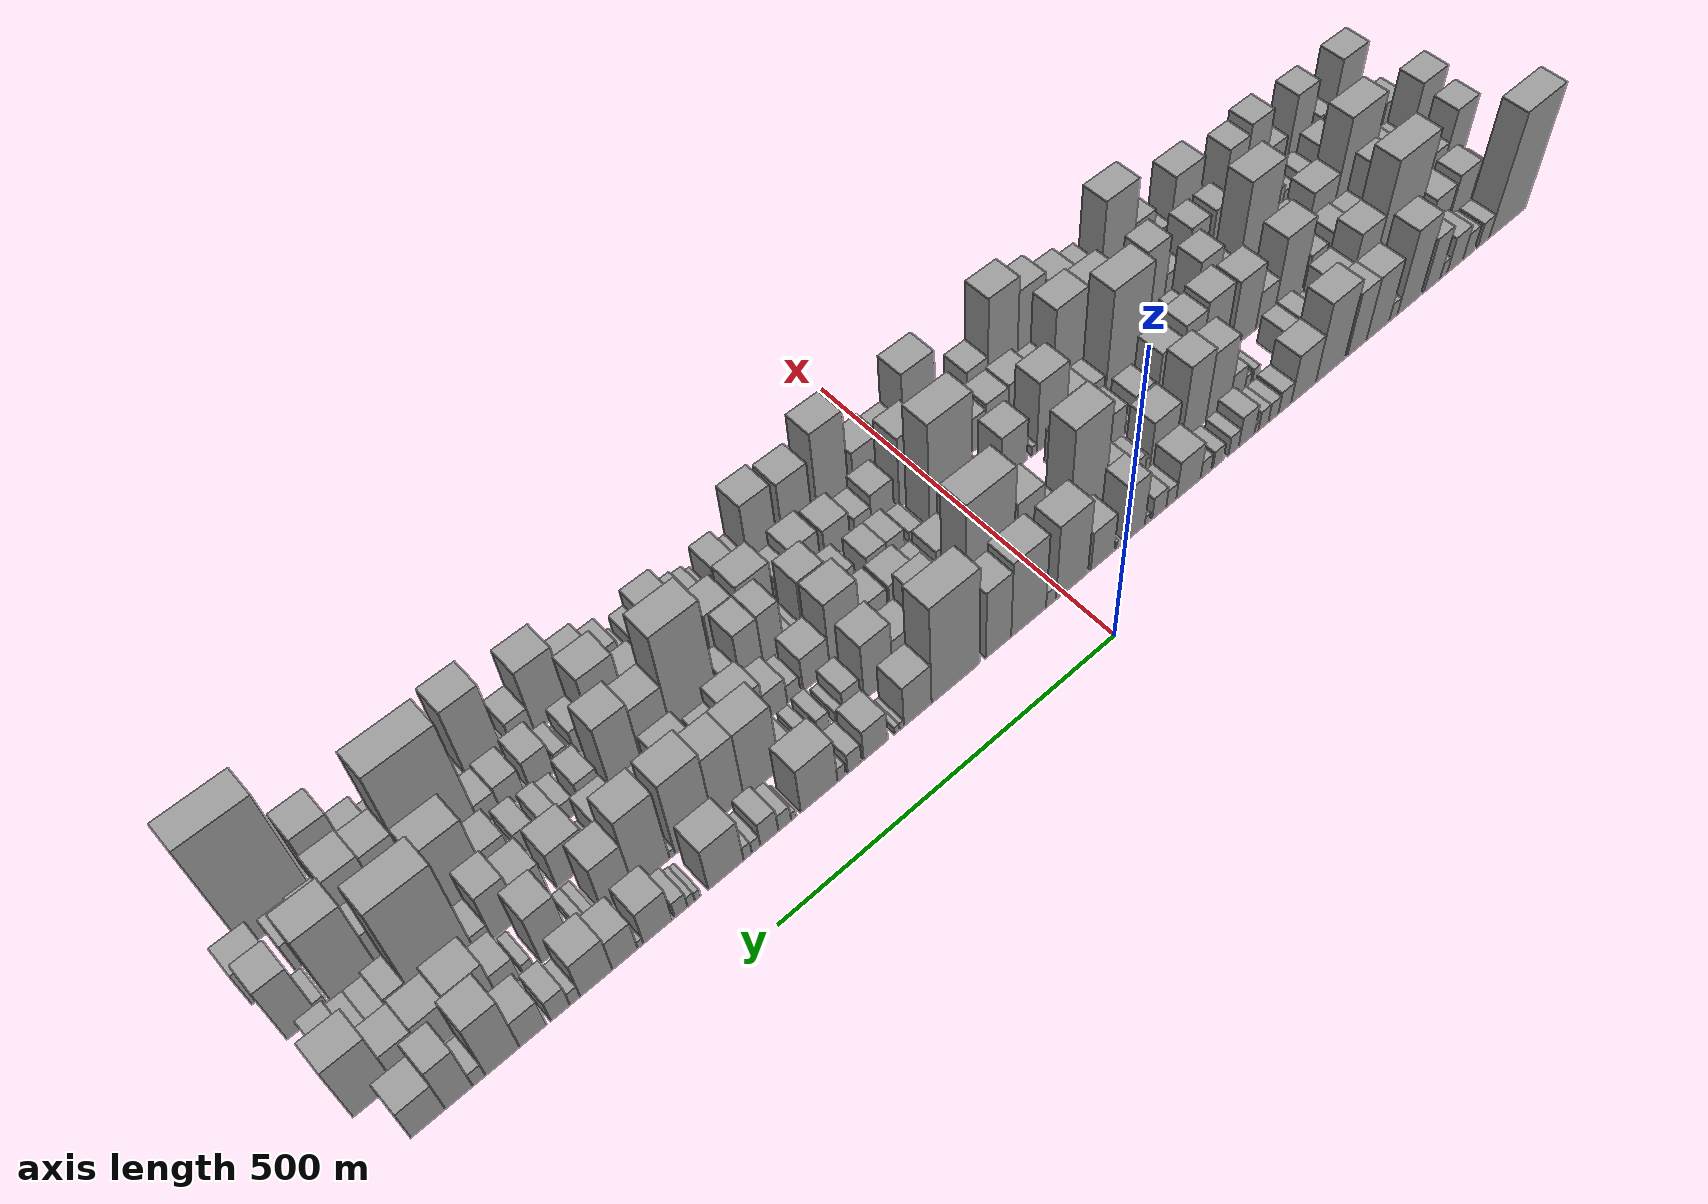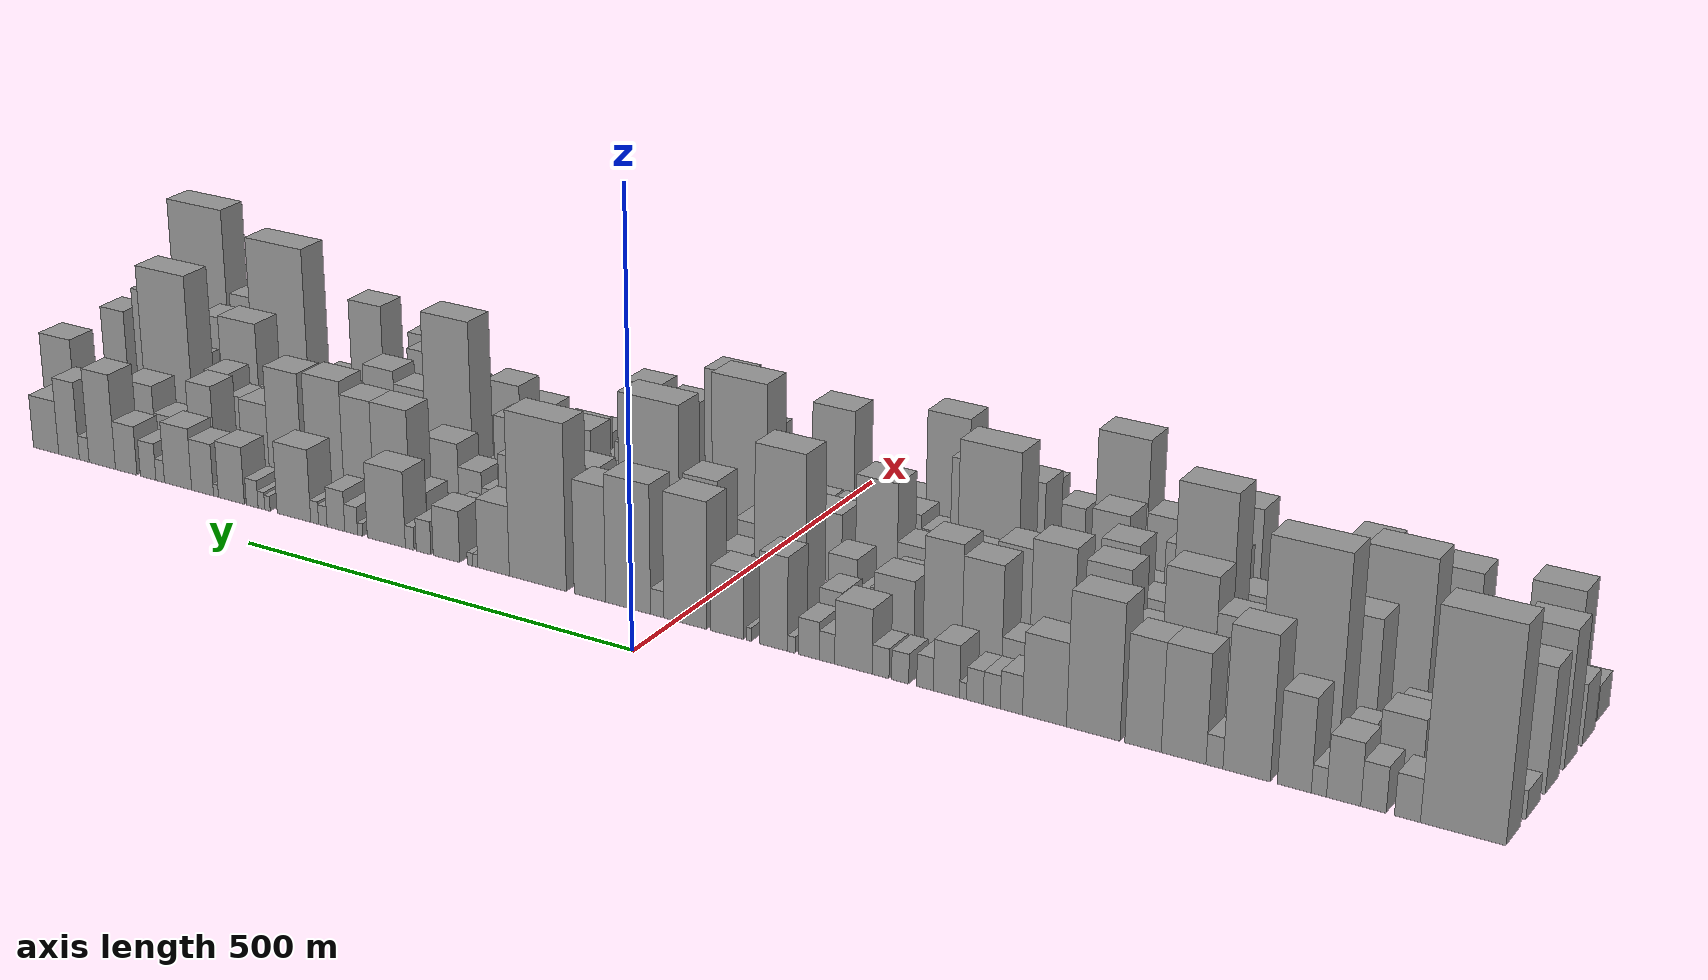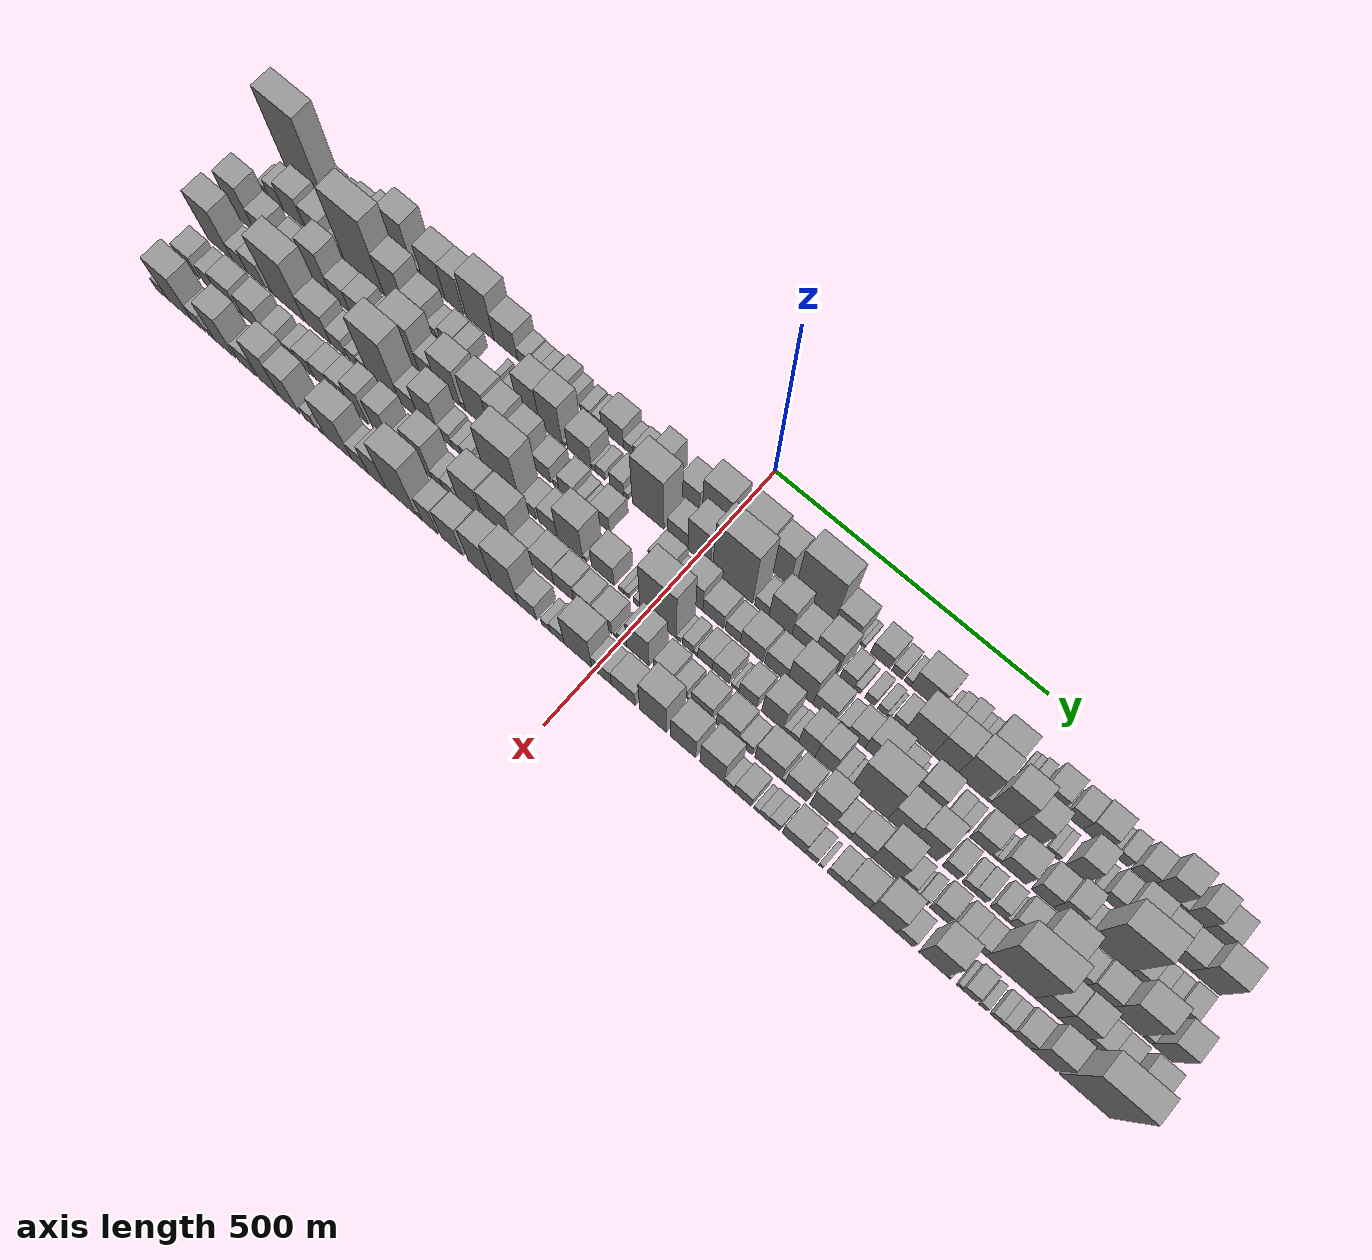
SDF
<sdf version="1.6">
 <world name="default">
  <scene>
   <sky><clouds><speed>12</speed></clouds></sky>
   <ambient>0.4 0.4 0.4 1</ambient>
   <background>0.7 0.7 0.7 1</background>
   <shadows>1</shadows>
  </scene>
  <gravity>0 0 -9.8066</gravity>
  <magnetic_field>6e-06 2.3e-05 -4.2e-05</magnetic_field>
  <physics default="0" name="default_physics" type="ode">
   <ode>
    <solver>
     <type>quick</type>
     <iters>10</iters>
     <sor>1.0</sor>
     <use_dynamic_moi_rescaling>0</use_dynamic_moi_rescaling>
    </solver>
    <constraints>
     <cfm>0</cfm>
     <erp>0.2</erp>
     <contact_max_correcting_vel>100</contact_max_correcting_vel>
     <contact_surface_layer>0.001</contact_surface_layer>
    </constraints>
   </ode>
   <max_step_size>0.004</max_step_size>
   <real_time_factor>1</real_time_factor>
   <real_time_update_rate>250</real_time_update_rate>
  </physics>
  <light name="sun" type="directional">
   <pose>0 0 10 0 0 0</pose>
   <diffuse>0.8 0.8 0.8 1</diffuse>
   <specular>0.2 0.2 0.2 1</specular>
   <attenuation>
    <range>1000</range>
    <constant>0.9</constant>
    <linear>0.01</linear>
    <quadratic>0.001</quadratic>
   </attenuation>
   <direction>-0.5 0.1 -0.9</direction>
  </light>
  <model name="building_1">
   <static>1</static>
   <pose>100.0000 -849.4702 0 0.000000 0.000000 0.000000</pose>
   <link name="link">
    <pose>0 0 111.00 0 0 0</pose>
    <collision name="collision"><geometry><box><size>40.0000 81.0596 222.0000</size></box></geometry></collision>
    <visual name="visual">
     <cast_shadows>0</cast_shadows>
     <geometry><box><size>40.0000 81.0596 222.0000</size></box></geometry>
     <material>
      <script>
       <uri>model://grey_wall/materials/scripts</uri>
       <uri>model://grey_wall/materials/textures</uri>
       <name>vrc/grey_wall</name>
      </script>
     </material>
    </visual>
   </link>
  </model>
  <model name="building_2">
   <static>1</static>
   <pose>100.0000 -796.4817 0 0.000000 0.000000 0.000000</pose>
   <link name="link">
    <pose>0 0 22.50 0 0 0</pose>
    <collision name="collision"><geometry><box><size>40.0000 24.9173 45.0000</size></box></geometry></collision>
    <visual name="visual">
     <cast_shadows>0</cast_shadows>
     <geometry><box><size>40.0000 24.9173 45.0000</size></box></geometry>
     <material>
      <script>
       <uri>model://grey_wall/materials/scripts</uri>
       <uri>model://grey_wall/materials/textures</uri>
       <name>vrc/grey_wall</name>
      </script>
     </material>
    </visual>
   </link>
  </model>
  <model name="building_3">
   <static>1</static>
   <pose>100.0000 -763.6660 0 0.000000 0.000000 0.000000</pose>
   <link name="link">
    <pose>0 0 24.00 0 0 0</pose>
    <collision name="collision"><geometry><box><size>40.0000 24.7142 48.0000</size></box></geometry></collision>
    <visual name="visual">
     <cast_shadows>0</cast_shadows>
     <geometry><box><size>40.0000 24.7142 48.0000</size></box></geometry>
     <material>
      <script>
       <uri>model://grey_wall/materials/scripts</uri>
       <uri>model://grey_wall/materials/textures</uri>
       <name>vrc/grey_wall</name>
      </script>
     </material>
    </visual>
   </link>
  </model>
  <model name="building_4">
   <static>1</static>
   <pose>100.0000 -734.4835 0 0.000000 0.000000 0.000000</pose>
   <link name="link">
    <pose>0 0 33.00 0 0 0</pose>
    <collision name="collision"><geometry><box><size>40.0000 33.6508 66.0000</size></box></geometry></collision>
    <visual name="visual">
     <cast_shadows>0</cast_shadows>
     <geometry><box><size>40.0000 33.6508 66.0000</size></box></geometry>
     <material>
      <script>
       <uri>model://grey_wall/materials/scripts</uri>
       <uri>model://grey_wall/materials/textures</uri>
       <name>vrc/grey_wall</name>
      </script>
     </material>
    </visual>
   </link>
  </model>
  <model name="building_5">
   <static>1</static>
   <pose>100.0000 -710.1181 0 0.000000 0.000000 0.000000</pose>
   <link name="link">
    <pose>0 0 15.00 0 0 0</pose>
    <collision name="collision"><geometry><box><size>40.0000 15.0800 30.0000</size></box></geometry></collision>
    <visual name="visual">
     <cast_shadows>0</cast_shadows>
     <geometry><box><size>40.0000 15.0800 30.0000</size></box></geometry>
     <material>
      <script>
       <uri>model://grey_wall/materials/scripts</uri>
       <uri>model://grey_wall/materials/textures</uri>
       <name>vrc/grey_wall</name>
      </script>
     </material>
    </visual>
   </link>
  </model>
  <model name="building_6">
   <static>1</static>
   <pose>100.0000 -685.6274 0 0.000000 0.000000 0.000000</pose>
   <link name="link">
    <pose>0 0 49.50 0 0 0</pose>
    <collision name="collision"><geometry><box><size>40.0000 33.9013 99.0000</size></box></geometry></collision>
    <visual name="visual">
     <cast_shadows>0</cast_shadows>
     <geometry><box><size>40.0000 33.9013 99.0000</size></box></geometry>
     <material>
      <script>
       <uri>model://grey_wall/materials/scripts</uri>
       <uri>model://grey_wall/materials/textures</uri>
       <name>vrc/grey_wall</name>
      </script>
     </material>
    </visual>
   </link>
  </model>
  <model name="building_7">
   <static>1</static>
   <pose>100.0000 -637.7286 0 0.000000 0.000000 0.000000</pose>
   <link name="link">
    <pose>0 0 76.50 0 0 0</pose>
    <collision name="collision"><geometry><box><size>40.0000 47.8963 153.0000</size></box></geometry></collision>
    <visual name="visual">
     <cast_shadows>0</cast_shadows>
     <geometry><box><size>40.0000 47.8963 153.0000</size></box></geometry>
     <material>
      <script>
       <uri>model://grey_wall/materials/scripts</uri>
       <uri>model://grey_wall/materials/textures</uri>
       <name>vrc/grey_wall</name>
      </script>
     </material>
    </visual>
   </link>
  </model>
  <model name="building_8">
   <static>1</static>
   <pose>100.0000 -605.0960 0 0.000000 0.000000 0.000000</pose>
   <link name="link">
    <pose>0 0 16.50 0 0 0</pose>
    <collision name="collision"><geometry><box><size>40.0000 17.3690 33.0000</size></box></geometry></collision>
    <visual name="visual">
     <cast_shadows>0</cast_shadows>
     <geometry><box><size>40.0000 17.3690 33.0000</size></box></geometry>
     <material>
      <script>
       <uri>model://grey_wall/materials/scripts</uri>
       <uri>model://grey_wall/materials/textures</uri>
       <name>vrc/grey_wall</name>
      </script>
     </material>
    </visual>
   </link>
  </model>
  <model name="building_9">
   <static>1</static>
   <pose>100.0000 -573.2728 0 0.000000 0.000000 0.000000</pose>
   <link name="link">
    <pose>0 0 58.50 0 0 0</pose>
    <collision name="collision"><geometry><box><size>40.0000 46.2772 117.0000</size></box></geometry></collision>
    <visual name="visual">
     <cast_shadows>0</cast_shadows>
     <geometry><box><size>40.0000 46.2772 117.0000</size></box></geometry>
     <material>
      <script>
       <uri>model://grey_wall/materials/scripts</uri>
       <uri>model://grey_wall/materials/textures</uri>
       <name>vrc/grey_wall</name>
      </script>
     </material>
    </visual>
   </link>
  </model>
  <model name="building_10">
   <static>1</static>
   <pose>100.0000 -531.0758 0 0.000000 0.000000 0.000000</pose>
   <link name="link">
    <pose>0 0 58.50 0 0 0</pose>
    <collision name="collision"><geometry><box><size>40.0000 38.1168 117.0000</size></box></geometry></collision>
    <visual name="visual">
     <cast_shadows>0</cast_shadows>
     <geometry><box><size>40.0000 38.1168 117.0000</size></box></geometry>
     <material>
      <script>
       <uri>model://grey_wall/materials/scripts</uri>
       <uri>model://grey_wall/materials/textures</uri>
       <name>vrc/grey_wall</name>
      </script>
     </material>
    </visual>
   </link>
  </model>
  <model name="building_11">
   <static>1</static>
   <pose>100.0000 -478.4523 0 0.000000 0.000000 0.000000</pose>
   <link name="link">
    <pose>0 0 73.50 0 0 0</pose>
    <collision name="collision"><geometry><box><size>40.0000 57.1301 147.0000</size></box></geometry></collision>
    <visual name="visual">
     <cast_shadows>0</cast_shadows>
     <geometry><box><size>40.0000 57.1301 147.0000</size></box></geometry>
     <material>
      <script>
       <uri>model://grey_wall/materials/scripts</uri>
       <uri>model://grey_wall/materials/textures</uri>
       <name>vrc/grey_wall</name>
      </script>
     </material>
    </visual>
   </link>
  </model>
  <model name="building_12">
   <static>1</static>
   <pose>100.0000 -426.1134 0 0.000000 0.000000 0.000000</pose>
   <link name="link">
    <pose>0 0 45.00 0 0 0</pose>
    <collision name="collision"><geometry><box><size>40.0000 47.5477 90.0000</size></box></geometry></collision>
    <visual name="visual">
     <cast_shadows>0</cast_shadows>
     <geometry><box><size>40.0000 47.5477 90.0000</size></box></geometry>
     <material>
      <script>
       <uri>model://grey_wall/materials/scripts</uri>
       <uri>model://grey_wall/materials/textures</uri>
       <name>vrc/grey_wall</name>
      </script>
     </material>
    </visual>
   </link>
  </model>
  <model name="building_13">
   <static>1</static>
   <pose>100.0000 -390.1908 0 0.000000 0.000000 0.000000</pose>
   <link name="link">
    <pose>0 0 21.00 0 0 0</pose>
    <collision name="collision"><geometry><box><size>40.0000 24.2976 42.0000</size></box></geometry></collision>
    <visual name="visual">
     <cast_shadows>0</cast_shadows>
     <geometry><box><size>40.0000 24.2976 42.0000</size></box></geometry>
     <material>
      <script>
       <uri>model://grey_wall/materials/scripts</uri>
       <uri>model://grey_wall/materials/textures</uri>
       <name>vrc/grey_wall</name>
      </script>
     </material>
    </visual>
   </link>
  </model>
  <model name="building_14">
   <static>1</static>
   <pose>100.0000 -368.6567 0 0.000000 0.000000 0.000000</pose>
   <link name="link">
    <pose>0 0 18.00 0 0 0</pose>
    <collision name="collision"><geometry><box><size>40.0000 18.7706 36.0000</size></box></geometry></collision>
    <visual name="visual">
     <cast_shadows>0</cast_shadows>
     <geometry><box><size>40.0000 18.7706 36.0000</size></box></geometry>
     <material>
      <script>
       <uri>model://grey_wall/materials/scripts</uri>
       <uri>model://grey_wall/materials/textures</uri>
       <name>vrc/grey_wall</name>
      </script>
     </material>
    </visual>
   </link>
  </model>
  <model name="building_15">
   <static>1</static>
   <pose>100.0000 -350.0476 0 0.000000 0.000000 0.000000</pose>
   <link name="link">
    <pose>0 0 18.00 0 0 0</pose>
    <collision name="collision"><geometry><box><size>40.0000 18.4478 36.0000</size></box></geometry></collision>
    <visual name="visual">
     <cast_shadows>0</cast_shadows>
     <geometry><box><size>40.0000 18.4478 36.0000</size></box></geometry>
     <material>
      <script>
       <uri>model://grey_wall/materials/scripts</uri>
       <uri>model://grey_wall/materials/textures</uri>
       <name>vrc/grey_wall</name>
      </script>
     </material>
    </visual>
   </link>
  </model>
  <model name="building_16">
   <static>1</static>
   <pose>100.0000 -336.9189 0 0.000000 0.000000 0.000000</pose>
   <link name="link">
    <pose>0 0 9.00 0 0 0</pose>
    <collision name="collision"><geometry><box><size>40.0000 7.8095 18.0000</size></box></geometry></collision>
    <visual name="visual">
     <cast_shadows>0</cast_shadows>
     <geometry><box><size>40.0000 7.8095 18.0000</size></box></geometry>
     <material>
      <script>
       <uri>model://grey_wall/materials/scripts</uri>
       <uri>model://grey_wall/materials/textures</uri>
       <name>vrc/grey_wall</name>
      </script>
     </material>
    </visual>
   </link>
  </model>
  <model name="building_17">
   <static>1</static>
   <pose>100.0000 -318.3340 0 0.000000 0.000000 0.000000</pose>
   <link name="link">
    <pose>0 0 28.50 0 0 0</pose>
    <collision name="collision"><geometry><box><size>40.0000 29.3602 57.0000</size></box></geometry></collision>
    <visual name="visual">
     <cast_shadows>0</cast_shadows>
     <geometry><box><size>40.0000 29.3602 57.0000</size></box></geometry>
     <material>
      <script>
       <uri>model://grey_wall/materials/scripts</uri>
       <uri>model://grey_wall/materials/textures</uri>
       <name>vrc/grey_wall</name>
      </script>
     </material>
    </visual>
   </link>
  </model>
  <model name="building_18">
   <static>1</static>
   <pose>100.0000 -294.3036 0 0.000000 0.000000 0.000000</pose>
   <link name="link">
    <pose>0 0 18.00 0 0 0</pose>
    <collision name="collision"><geometry><box><size>40.0000 18.7005 36.0000</size></box></geometry></collision>
    <visual name="visual">
     <cast_shadows>0</cast_shadows>
     <geometry><box><size>40.0000 18.7005 36.0000</size></box></geometry>
     <material>
      <script>
       <uri>model://grey_wall/materials/scripts</uri>
       <uri>model://grey_wall/materials/textures</uri>
       <name>vrc/grey_wall</name>
      </script>
     </material>
    </visual>
   </link>
  </model>
  <model name="building_19">
   <static>1</static>
   <pose>100.0000 -266.2301 0 0.000000 0.000000 0.000000</pose>
   <link name="link">
    <pose>0 0 16.50 0 0 0</pose>
    <collision name="collision"><geometry><box><size>40.0000 19.4466 33.0000</size></box></geometry></collision>
    <visual name="visual">
     <cast_shadows>0</cast_shadows>
     <geometry><box><size>40.0000 19.4466 33.0000</size></box></geometry>
     <material>
      <script>
       <uri>model://grey_wall/materials/scripts</uri>
       <uri>model://grey_wall/materials/textures</uri>
       <name>vrc/grey_wall</name>
      </script>
     </material>
    </visual>
   </link>
  </model>
  <model name="building_20">
   <static>1</static>
   <pose>100.0000 -243.8483 0 0.000000 0.000000 0.000000</pose>
   <link name="link">
    <pose>0 0 16.50 0 0 0</pose>
    <collision name="collision"><geometry><box><size>40.0000 19.3169 33.0000</size></box></geometry></collision>
    <visual name="visual">
     <cast_shadows>0</cast_shadows>
     <geometry><box><size>40.0000 19.3169 33.0000</size></box></geometry>
     <material>
      <script>
       <uri>model://grey_wall/materials/scripts</uri>
       <uri>model://grey_wall/materials/textures</uri>
       <name>vrc/grey_wall</name>
      </script>
     </material>
    </visual>
   </link>
  </model>
  <model name="building_21">
   <static>1</static>
   <pose>100.0000 -212.6114 0 0.000000 0.000000 0.000000</pose>
   <link name="link">
    <pose>0 0 36.00 0 0 0</pose>
    <collision name="collision"><geometry><box><size>40.0000 43.1568 72.0000</size></box></geometry></collision>
    <visual name="visual">
     <cast_shadows>0</cast_shadows>
     <geometry><box><size>40.0000 43.1568 72.0000</size></box></geometry>
     <material>
      <script>
       <uri>model://grey_wall/materials/scripts</uri>
       <uri>model://grey_wall/materials/textures</uri>
       <name>vrc/grey_wall</name>
      </script>
     </material>
    </visual>
   </link>
  </model>
  <model name="building_22">
   <static>1</static>
   <pose>100.0000 -182.1279 0 0.000000 0.000000 0.000000</pose>
   <link name="link">
    <pose>0 0 16.50 0 0 0</pose>
    <collision name="collision"><geometry><box><size>40.0000 17.8102 33.0000</size></box></geometry></collision>
    <visual name="visual">
     <cast_shadows>0</cast_shadows>
     <geometry><box><size>40.0000 17.8102 33.0000</size></box></geometry>
     <material>
      <script>
       <uri>model://grey_wall/materials/scripts</uri>
       <uri>model://grey_wall/materials/textures</uri>
       <name>vrc/grey_wall</name>
      </script>
     </material>
    </visual>
   </link>
  </model>
  <model name="building_23">
   <static>1</static>
   <pose>100.0000 -160.9204 0 0.000000 0.000000 0.000000</pose>
   <link name="link">
    <pose>0 0 21.00 0 0 0</pose>
    <collision name="collision"><geometry><box><size>40.0000 24.6049 42.0000</size></box></geometry></collision>
    <visual name="visual">
     <cast_shadows>0</cast_shadows>
     <geometry><box><size>40.0000 24.6049 42.0000</size></box></geometry>
     <material>
      <script>
       <uri>model://grey_wall/materials/scripts</uri>
       <uri>model://grey_wall/materials/textures</uri>
       <name>vrc/grey_wall</name>
      </script>
     </material>
    </visual>
   </link>
  </model>
  <model name="building_24">
   <static>1</static>
   <pose>100.0000 -140.2499 0 0.000000 0.000000 0.000000</pose>
   <link name="link">
    <pose>0 0 9.00 0 0 0</pose>
    <collision name="collision"><geometry><box><size>40.0000 8.7361 18.0000</size></box></geometry></collision>
    <visual name="visual">
     <cast_shadows>0</cast_shadows>
     <geometry><box><size>40.0000 8.7361 18.0000</size></box></geometry>
     <material>
      <script>
       <uri>model://grey_wall/materials/scripts</uri>
       <uri>model://grey_wall/materials/textures</uri>
       <name>vrc/grey_wall</name>
      </script>
     </material>
    </visual>
   </link>
  </model>
  <model name="building_25">
   <static>1</static>
   <pose>100.0000 -119.2909 0 0.000000 0.000000 0.000000</pose>
   <link name="link">
    <pose>0 0 52.50 0 0 0</pose>
    <collision name="collision"><geometry><box><size>40.0000 33.1821 105.0000</size></box></geometry></collision>
    <visual name="visual">
     <cast_shadows>0</cast_shadows>
     <geometry><box><size>40.0000 33.1821 105.0000</size></box></geometry>
     <material>
      <script>
       <uri>model://grey_wall/materials/scripts</uri>
       <uri>model://grey_wall/materials/textures</uri>
       <name>vrc/grey_wall</name>
      </script>
     </material>
    </visual>
   </link>
  </model>
  <model name="building_26">
   <static>1</static>
   <pose>100.0000 -89.6334 0 0.000000 0.000000 0.000000</pose>
   <link name="link">
    <pose>0 0 7.50 0 0 0</pose>
    <collision name="collision"><geometry><box><size>40.0000 6.1329 15.0000</size></box></geometry></collision>
    <visual name="visual">
     <cast_shadows>0</cast_shadows>
     <geometry><box><size>40.0000 6.1329 15.0000</size></box></geometry>
     <material>
      <script>
       <uri>model://grey_wall/materials/scripts</uri>
       <uri>model://grey_wall/materials/textures</uri>
       <name>vrc/grey_wall</name>
      </script>
     </material>
    </visual>
   </link>
  </model>
  <model name="building_27">
   <static>1</static>
   <pose>100.0000 -63.7822 0 0.000000 0.000000 0.000000</pose>
   <link name="link">
    <pose>0 0 37.50 0 0 0</pose>
    <collision name="collision"><geometry><box><size>40.0000 39.5694 75.0000</size></box></geometry></collision>
    <visual name="visual">
     <cast_shadows>0</cast_shadows>
     <geometry><box><size>40.0000 39.5694 75.0000</size></box></geometry>
     <material>
      <script>
       <uri>model://grey_wall/materials/scripts</uri>
       <uri>model://grey_wall/materials/textures</uri>
       <name>vrc/grey_wall</name>
      </script>
     </material>
    </visual>
   </link>
  </model>
  <model name="building_28">
   <static>1</static>
   <pose>100.0000 -12.6205 0 0.000000 0.000000 0.000000</pose>
   <link name="link">
    <pose>0 0 72.00 0 0 0</pose>
    <collision name="collision"><geometry><box><size>40.0000 52.7541 144.0000</size></box></geometry></collision>
    <visual name="visual">
     <cast_shadows>0</cast_shadows>
     <geometry><box><size>40.0000 52.7541 144.0000</size></box></geometry>
     <material>
      <script>
       <uri>model://grey_wall/materials/scripts</uri>
       <uri>model://grey_wall/materials/textures</uri>
       <name>vrc/grey_wall</name>
      </script>
     </material>
    </visual>
   </link>
  </model>
  <model name="building_29">
   <static>1</static>
   <pose>100.0000 21.8884 0 0.000000 0.000000 0.000000</pose>
   <link name="link">
    <pose>0 0 15.00 0 0 0</pose>
    <collision name="collision"><geometry><box><size>40.0000 16.2637 30.0000</size></box></geometry></collision>
    <visual name="visual">
     <cast_shadows>0</cast_shadows>
     <geometry><box><size>40.0000 16.2637 30.0000</size></box></geometry>
     <material>
      <script>
       <uri>model://grey_wall/materials/scripts</uri>
       <uri>model://grey_wall/materials/textures</uri>
       <name>vrc/grey_wall</name>
      </script>
     </material>
    </visual>
   </link>
  </model>
  <model name="building_30">
   <static>1</static>
   <pose>100.0000 58.0798 0 0.000000 0.000000 0.000000</pose>
   <link name="link">
    <pose>0 0 73.50 0 0 0</pose>
    <collision name="collision"><geometry><box><size>40.0000 56.1190 147.0000</size></box></geometry></collision>
    <visual name="visual">
     <cast_shadows>0</cast_shadows>
     <geometry><box><size>40.0000 56.1190 147.0000</size></box></geometry>
     <material>
      <script>
       <uri>model://grey_wall/materials/scripts</uri>
       <uri>model://grey_wall/materials/textures</uri>
       <name>vrc/grey_wall</name>
      </script>
     </material>
    </visual>
   </link>
  </model>
  <model name="building_31">
   <static>1</static>
   <pose>100.0000 106.1186 0 0.000000 0.000000 0.000000</pose>
   <link name="link">
    <pose>0 0 66.00 0 0 0</pose>
    <collision name="collision"><geometry><box><size>40.0000 39.9587 132.0000</size></box></geometry></collision>
    <visual name="visual">
     <cast_shadows>0</cast_shadows>
     <geometry><box><size>40.0000 39.9587 132.0000</size></box></geometry>
     <material>
      <script>
       <uri>model://grey_wall/materials/scripts</uri>
       <uri>model://grey_wall/materials/textures</uri>
       <name>vrc/grey_wall</name>
      </script>
     </material>
    </visual>
   </link>
  </model>
  <model name="building_32">
   <static>1</static>
   <pose>100.0000 172.9153 0 0.000000 0.000000 0.000000</pose>
   <link name="link">
    <pose>0 0 96.00 0 0 0</pose>
    <collision name="collision"><geometry><box><size>40.0000 73.6347 192.0000</size></box></geometry></collision>
    <visual name="visual">
     <cast_shadows>0</cast_shadows>
     <geometry><box><size>40.0000 73.6347 192.0000</size></box></geometry>
     <material>
      <script>
       <uri>model://grey_wall/materials/scripts</uri>
       <uri>model://grey_wall/materials/textures</uri>
       <name>vrc/grey_wall</name>
      </script>
     </material>
    </visual>
   </link>
  </model>
  <model name="building_33">
   <static>1</static>
   <pose>100.0000 230.5214 0 0.000000 0.000000 0.000000</pose>
   <link name="link">
    <pose>0 0 40.50 0 0 0</pose>
    <collision name="collision"><geometry><box><size>40.0000 41.5774 81.0000</size></box></geometry></collision>
    <visual name="visual">
     <cast_shadows>0</cast_shadows>
     <geometry><box><size>40.0000 41.5774 81.0000</size></box></geometry>
     <material>
      <script>
       <uri>model://grey_wall/materials/scripts</uri>
       <uri>model://grey_wall/materials/textures</uri>
       <name>vrc/grey_wall</name>
      </script>
     </material>
    </visual>
   </link>
  </model>
  <model name="building_34">
   <static>1</static>
   <pose>100.0000 254.5305 0 0.000000 0.000000 0.000000</pose>
   <link name="link">
    <pose>0 0 7.50 0 0 0</pose>
    <collision name="collision"><geometry><box><size>40.0000 6.4407 15.0000</size></box></geometry></collision>
    <visual name="visual">
     <cast_shadows>0</cast_shadows>
     <geometry><box><size>40.0000 6.4407 15.0000</size></box></geometry>
     <material>
      <script>
       <uri>model://grey_wall/materials/scripts</uri>
       <uri>model://grey_wall/materials/textures</uri>
       <name>vrc/grey_wall</name>
      </script>
     </material>
    </visual>
   </link>
  </model>
  <model name="building_35">
   <static>1</static>
   <pose>100.0000 261.4549 0 0.000000 0.000000 0.000000</pose>
   <link name="link">
    <pose>0 0 7.50 0 0 0</pose>
    <collision name="collision"><geometry><box><size>40.0000 7.4081 15.0000</size></box></geometry></collision>
    <visual name="visual">
     <cast_shadows>0</cast_shadows>
     <geometry><box><size>40.0000 7.4081 15.0000</size></box></geometry>
     <material>
      <script>
       <uri>model://grey_wall/materials/scripts</uri>
       <uri>model://grey_wall/materials/textures</uri>
       <name>vrc/grey_wall</name>
      </script>
     </material>
    </visual>
   </link>
  </model>
  <model name="building_36">
   <static>1</static>
   <pose>100.0000 292.9028 0 0.000000 0.000000 0.000000</pose>
   <link name="link">
    <pose>0 0 30.00 0 0 0</pose>
    <collision name="collision"><geometry><box><size>40.0000 35.4877 60.0000</size></box></geometry></collision>
    <visual name="visual">
     <cast_shadows>0</cast_shadows>
     <geometry><box><size>40.0000 35.4877 60.0000</size></box></geometry>
     <material>
      <script>
       <uri>model://grey_wall/materials/scripts</uri>
       <uri>model://grey_wall/materials/textures</uri>
       <name>vrc/grey_wall</name>
      </script>
     </material>
    </visual>
   </link>
  </model>
  <model name="building_37">
   <static>1</static>
   <pose>100.0000 323.5563 0 0.000000 0.000000 0.000000</pose>
   <link name="link">
    <pose>0 0 19.50 0 0 0</pose>
    <collision name="collision"><geometry><box><size>40.0000 19.8193 39.0000</size></box></geometry></collision>
    <visual name="visual">
     <cast_shadows>0</cast_shadows>
     <geometry><box><size>40.0000 19.8193 39.0000</size></box></geometry>
     <material>
      <script>
       <uri>model://grey_wall/materials/scripts</uri>
       <uri>model://grey_wall/materials/textures</uri>
       <name>vrc/grey_wall</name>
      </script>
     </material>
    </visual>
   </link>
  </model>
  <model name="building_38">
   <static>1</static>
   <pose>100.0000 342.3255 0 0.000000 0.000000 0.000000</pose>
   <link name="link">
    <pose>0 0 13.50 0 0 0</pose>
    <collision name="collision"><geometry><box><size>40.0000 11.7192 27.0000</size></box></geometry></collision>
    <visual name="visual">
     <cast_shadows>0</cast_shadows>
     <geometry><box><size>40.0000 11.7192 27.0000</size></box></geometry>
     <material>
      <script>
       <uri>model://grey_wall/materials/scripts</uri>
       <uri>model://grey_wall/materials/textures</uri>
       <name>vrc/grey_wall</name>
      </script>
     </material>
    </visual>
   </link>
  </model>
  <model name="building_39">
   <static>1</static>
   <pose>100.0000 374.2217 0 0.000000 0.000000 0.000000</pose>
   <link name="link">
    <pose>0 0 45.00 0 0 0</pose>
    <collision name="collision"><geometry><box><size>40.0000 52.0733 90.0000</size></box></geometry></collision>
    <visual name="visual">
     <cast_shadows>0</cast_shadows>
     <geometry><box><size>40.0000 52.0733 90.0000</size></box></geometry>
     <material>
      <script>
       <uri>model://grey_wall/materials/scripts</uri>
       <uri>model://grey_wall/materials/textures</uri>
       <name>vrc/grey_wall</name>
      </script>
     </material>
    </visual>
   </link>
  </model>
  <model name="building_40">
   <static>1</static>
   <pose>100.0000 409.9997 0 0.000000 0.000000 0.000000</pose>
   <link name="link">
    <pose>0 0 7.50 0 0 0</pose>
    <collision name="collision"><geometry><box><size>40.0000 7.4827 15.0000</size></box></geometry></collision>
    <visual name="visual">
     <cast_shadows>0</cast_shadows>
     <geometry><box><size>40.0000 7.4827 15.0000</size></box></geometry>
     <material>
      <script>
       <uri>model://grey_wall/materials/scripts</uri>
       <uri>model://grey_wall/materials/textures</uri>
       <name>vrc/grey_wall</name>
      </script>
     </material>
    </visual>
   </link>
  </model>
  <model name="building_41">
   <static>1</static>
   <pose>100.0000 422.5605 0 0.000000 0.000000 0.000000</pose>
   <link name="link">
    <pose>0 0 16.50 0 0 0</pose>
    <collision name="collision"><geometry><box><size>40.0000 17.6389 33.0000</size></box></geometry></collision>
    <visual name="visual">
     <cast_shadows>0</cast_shadows>
     <geometry><box><size>40.0000 17.6389 33.0000</size></box></geometry>
     <material>
      <script>
       <uri>model://grey_wall/materials/scripts</uri>
       <uri>model://grey_wall/materials/textures</uri>
       <name>vrc/grey_wall</name>
      </script>
     </material>
    </visual>
   </link>
  </model>
  <model name="building_42">
   <static>1</static>
   <pose>100.0000 443.7260 0 0.000000 0.000000 0.000000</pose>
   <link name="link">
    <pose>0 0 24.00 0 0 0</pose>
    <collision name="collision"><geometry><box><size>40.0000 24.6920 48.0000</size></box></geometry></collision>
    <visual name="visual">
     <cast_shadows>0</cast_shadows>
     <geometry><box><size>40.0000 24.6920 48.0000</size></box></geometry>
     <material>
      <script>
       <uri>model://grey_wall/materials/scripts</uri>
       <uri>model://grey_wall/materials/textures</uri>
       <name>vrc/grey_wall</name>
      </script>
     </material>
    </visual>
   </link>
  </model>
  <model name="building_43">
   <static>1</static>
   <pose>100.0000 461.9823 0 0.000000 0.000000 0.000000</pose>
   <link name="link">
    <pose>0 0 12.00 0 0 0</pose>
    <collision name="collision"><geometry><box><size>40.0000 11.8207 24.0000</size></box></geometry></collision>
    <visual name="visual">
     <cast_shadows>0</cast_shadows>
     <geometry><box><size>40.0000 11.8207 24.0000</size></box></geometry>
     <material>
      <script>
       <uri>model://grey_wall/materials/scripts</uri>
       <uri>model://grey_wall/materials/textures</uri>
       <name>vrc/grey_wall</name>
      </script>
     </material>
    </visual>
   </link>
  </model>
  <model name="building_44">
   <static>1</static>
   <pose>100.0000 473.4352 0 0.000000 0.000000 0.000000</pose>
   <link name="link">
    <pose>0 0 13.50 0 0 0</pose>
    <collision name="collision"><geometry><box><size>40.0000 11.0850 27.0000</size></box></geometry></collision>
    <visual name="visual">
     <cast_shadows>0</cast_shadows>
     <geometry><box><size>40.0000 11.0850 27.0000</size></box></geometry>
     <material>
      <script>
       <uri>model://grey_wall/materials/scripts</uri>
       <uri>model://grey_wall/materials/textures</uri>
       <name>vrc/grey_wall</name>
      </script>
     </material>
    </visual>
   </link>
  </model>
  <model name="building_45">
   <static>1</static>
   <pose>100.0000 502.7370 0 0.000000 0.000000 0.000000</pose>
   <link name="link">
    <pose>0 0 43.50 0 0 0</pose>
    <collision name="collision"><geometry><box><size>40.0000 47.5186 87.0000</size></box></geometry></collision>
    <visual name="visual">
     <cast_shadows>0</cast_shadows>
     <geometry><box><size>40.0000 47.5186 87.0000</size></box></geometry>
     <material>
      <script>
       <uri>model://grey_wall/materials/scripts</uri>
       <uri>model://grey_wall/materials/textures</uri>
       <name>vrc/grey_wall</name>
      </script>
     </material>
    </visual>
   </link>
  </model>
  <model name="building_46">
   <static>1</static>
   <pose>100.0000 540.3720 0 0.000000 0.000000 0.000000</pose>
   <link name="link">
    <pose>0 0 9.00 0 0 0</pose>
    <collision name="collision"><geometry><box><size>40.0000 7.7514 18.0000</size></box></geometry></collision>
    <visual name="visual">
     <cast_shadows>0</cast_shadows>
     <geometry><box><size>40.0000 7.7514 18.0000</size></box></geometry>
     <material>
      <script>
       <uri>model://grey_wall/materials/scripts</uri>
       <uri>model://grey_wall/materials/textures</uri>
       <name>vrc/grey_wall</name>
      </script>
     </material>
    </visual>
   </link>
  </model>
  <model name="building_47">
   <static>1</static>
   <pose>100.0000 549.0262 0 0.000000 0.000000 0.000000</pose>
   <link name="link">
    <pose>0 0 10.50 0 0 0</pose>
    <collision name="collision"><geometry><box><size>40.0000 9.5570 21.0000</size></box></geometry></collision>
    <visual name="visual">
     <cast_shadows>0</cast_shadows>
     <geometry><box><size>40.0000 9.5570 21.0000</size></box></geometry>
     <material>
      <script>
       <uri>model://grey_wall/materials/scripts</uri>
       <uri>model://grey_wall/materials/textures</uri>
       <name>vrc/grey_wall</name>
      </script>
     </material>
    </visual>
   </link>
  </model>
  <model name="building_48">
   <static>1</static>
   <pose>100.0000 562.2270 0 0.000000 0.000000 0.000000</pose>
   <link name="link">
    <pose>0 0 16.50 0 0 0</pose>
    <collision name="collision"><geometry><box><size>40.0000 16.8446 33.0000</size></box></geometry></collision>
    <visual name="visual">
     <cast_shadows>0</cast_shadows>
     <geometry><box><size>40.0000 16.8446 33.0000</size></box></geometry>
     <material>
      <script>
       <uri>model://grey_wall/materials/scripts</uri>
       <uri>model://grey_wall/materials/textures</uri>
       <name>vrc/grey_wall</name>
      </script>
     </material>
    </visual>
   </link>
  </model>
  <model name="building_49">
   <static>1</static>
   <pose>100.0000 592.3700 0 0.000000 0.000000 0.000000</pose>
   <link name="link">
    <pose>0 0 34.50 0 0 0</pose>
    <collision name="collision"><geometry><box><size>40.0000 37.4415 69.0000</size></box></geometry></collision>
    <visual name="visual">
     <cast_shadows>0</cast_shadows>
     <geometry><box><size>40.0000 37.4415 69.0000</size></box></geometry>
     <material>
      <script>
       <uri>model://grey_wall/materials/scripts</uri>
       <uri>model://grey_wall/materials/textures</uri>
       <name>vrc/grey_wall</name>
      </script>
     </material>
    </visual>
   </link>
  </model>
  <model name="building_50">
   <static>1</static>
   <pose>100.0000 614.6938 0 0.000000 0.000000 0.000000</pose>
   <link name="link">
    <pose>0 0 7.50 0 0 0</pose>
    <collision name="collision"><geometry><box><size>40.0000 7.2062 15.0000</size></box></geometry></collision>
    <visual name="visual">
     <cast_shadows>0</cast_shadows>
     <geometry><box><size>40.0000 7.2062 15.0000</size></box></geometry>
     <material>
      <script>
       <uri>model://grey_wall/materials/scripts</uri>
       <uri>model://grey_wall/materials/textures</uri>
       <name>vrc/grey_wall</name>
      </script>
     </material>
    </visual>
   </link>
  </model>
  <model name="building_51">
   <static>1</static>
   <pose>100.0000 634.3239 0 0.000000 0.000000 0.000000</pose>
   <link name="link">
    <pose>0 0 31.50 0 0 0</pose>
    <collision name="collision"><geometry><box><size>40.0000 32.0539 63.0000</size></box></geometry></collision>
    <visual name="visual">
     <cast_shadows>0</cast_shadows>
     <geometry><box><size>40.0000 32.0539 63.0000</size></box></geometry>
     <material>
      <script>
       <uri>model://grey_wall/materials/scripts</uri>
       <uri>model://grey_wall/materials/textures</uri>
       <name>vrc/grey_wall</name>
      </script>
     </material>
    </visual>
   </link>
  </model>
  <model name="building_52">
   <static>1</static>
   <pose>100.0000 670.5384 0 0.000000 0.000000 0.000000</pose>
   <link name="link">
    <pose>0 0 37.50 0 0 0</pose>
    <collision name="collision"><geometry><box><size>40.0000 40.3753 75.0000</size></box></geometry></collision>
    <visual name="visual">
     <cast_shadows>0</cast_shadows>
     <geometry><box><size>40.0000 40.3753 75.0000</size></box></geometry>
     <material>
      <script>
       <uri>model://grey_wall/materials/scripts</uri>
       <uri>model://grey_wall/materials/textures</uri>
       <name>vrc/grey_wall</name>
      </script>
     </material>
    </visual>
   </link>
  </model>
  <model name="building_53">
   <static>1</static>
   <pose>100.0000 697.0407 0 0.000000 0.000000 0.000000</pose>
   <link name="link">
    <pose>0 0 13.50 0 0 0</pose>
    <collision name="collision"><geometry><box><size>40.0000 12.6293 27.0000</size></box></geometry></collision>
    <visual name="visual">
     <cast_shadows>0</cast_shadows>
     <geometry><box><size>40.0000 12.6293 27.0000</size></box></geometry>
     <material>
      <script>
       <uri>model://grey_wall/materials/scripts</uri>
       <uri>model://grey_wall/materials/textures</uri>
       <name>vrc/grey_wall</name>
      </script>
     </material>
    </visual>
   </link>
  </model>
  <model name="building_54">
   <static>1</static>
   <pose>100.0000 715.0363 0 0.000000 0.000000 0.000000</pose>
   <link name="link">
    <pose>0 0 22.50 0 0 0</pose>
    <collision name="collision"><geometry><box><size>40.0000 23.3619 45.0000</size></box></geometry></collision>
    <visual name="visual">
     <cast_shadows>0</cast_shadows>
     <geometry><box><size>40.0000 23.3619 45.0000</size></box></geometry>
     <material>
      <script>
       <uri>model://grey_wall/materials/scripts</uri>
       <uri>model://grey_wall/materials/textures</uri>
       <name>vrc/grey_wall</name>
      </script>
     </material>
    </visual>
   </link>
  </model>
  <model name="building_55">
   <static>1</static>
   <pose>100.0000 747.9944 0 0.000000 0.000000 0.000000</pose>
   <link name="link">
    <pose>0 0 30.00 0 0 0</pose>
    <collision name="collision"><geometry><box><size>40.0000 32.5543 60.0000</size></box></geometry></collision>
    <visual name="visual">
     <cast_shadows>0</cast_shadows>
     <geometry><box><size>40.0000 32.5543 60.0000</size></box></geometry>
     <material>
      <script>
       <uri>model://grey_wall/materials/scripts</uri>
       <uri>model://grey_wall/materials/textures</uri>
       <name>vrc/grey_wall</name>
      </script>
     </material>
    </visual>
   </link>
  </model>
  <model name="building_56">
   <static>1</static>
   <pose>100.0000 784.3968 0 0.000000 0.000000 0.000000</pose>
   <link name="link">
    <pose>0 0 58.50 0 0 0</pose>
    <collision name="collision"><geometry><box><size>40.0000 40.2505 117.0000</size></box></geometry></collision>
    <visual name="visual">
     <cast_shadows>0</cast_shadows>
     <geometry><box><size>40.0000 40.2505 117.0000</size></box></geometry>
     <material>
      <script>
       <uri>model://grey_wall/materials/scripts</uri>
       <uri>model://grey_wall/materials/textures</uri>
       <name>vrc/grey_wall</name>
      </script>
     </material>
    </visual>
   </link>
  </model>
  <model name="building_57">
   <static>1</static>
   <pose>100.0000 812.0516 0 0.000000 0.000000 0.000000</pose>
   <link name="link">
    <pose>0 0 15.00 0 0 0</pose>
    <collision name="collision"><geometry><box><size>40.0000 15.0590 30.0000</size></box></geometry></collision>
    <visual name="visual">
     <cast_shadows>0</cast_shadows>
     <geometry><box><size>40.0000 15.0590 30.0000</size></box></geometry>
     <material>
      <script>
       <uri>model://grey_wall/materials/scripts</uri>
       <uri>model://grey_wall/materials/textures</uri>
       <name>vrc/grey_wall</name>
      </script>
     </material>
    </visual>
   </link>
  </model>
  <model name="building_58">
   <static>1</static>
   <pose>100.0000 835.4757 0 0.000000 0.000000 0.000000</pose>
   <link name="link">
    <pose>0 0 48.00 0 0 0</pose>
    <collision name="collision"><geometry><box><size>40.0000 31.7892 96.0000</size></box></geometry></collision>
    <visual name="visual">
     <cast_shadows>0</cast_shadows>
     <geometry><box><size>40.0000 31.7892 96.0000</size></box></geometry>
     <material>
      <script>
       <uri>model://grey_wall/materials/scripts</uri>
       <uri>model://grey_wall/materials/textures</uri>
       <name>vrc/grey_wall</name>
      </script>
     </material>
    </visual>
   </link>
  </model>
  <model name="building_59">
   <static>1</static>
   <pose>100.0000 871.0971 0 0.000000 0.000000 0.000000</pose>
   <link name="link">
    <pose>0 0 33.00 0 0 0</pose>
    <collision name="collision"><geometry><box><size>40.0000 39.4536 66.0000</size></box></geometry></collision>
    <visual name="visual">
     <cast_shadows>0</cast_shadows>
     <geometry><box><size>40.0000 39.4536 66.0000</size></box></geometry>
     <material>
      <script>
       <uri>model://grey_wall/materials/scripts</uri>
       <uri>model://grey_wall/materials/textures</uri>
       <name>vrc/grey_wall</name>
      </script>
     </material>
    </visual>
   </link>
  </model>
  <model name="building_60">
   <static>1</static>
   <pose>155.0000 -882.0283 0 0.000000 0.000000 0.000000</pose>
   <link name="link">
    <pose>0 0 15.00 0 0 0</pose>
    <collision name="collision"><geometry><box><size>40.0000 15.9435 30.0000</size></box></geometry></collision>
    <visual name="visual">
     <cast_shadows>0</cast_shadows>
     <geometry><box><size>40.0000 15.9435 30.0000</size></box></geometry>
     <material>
      <script>
       <uri>model://grey_wall/materials/scripts</uri>
       <uri>model://grey_wall/materials/textures</uri>
       <name>vrc/grey_wall</name>
      </script>
     </material>
    </visual>
   </link>
  </model>
  <model name="building_61">
   <static>1</static>
   <pose>155.0000 -852.9498 0 0.000000 0.000000 0.000000</pose>
   <link name="link">
    <pose>0 0 30.00 0 0 0</pose>
    <collision name="collision"><geometry><box><size>40.0000 30.2134 60.0000</size></box></geometry></collision>
    <visual name="visual">
     <cast_shadows>0</cast_shadows>
     <geometry><box><size>40.0000 30.2134 60.0000</size></box></geometry>
     <material>
      <script>
       <uri>model://grey_wall/materials/scripts</uri>
       <uri>model://grey_wall/materials/textures</uri>
       <name>vrc/grey_wall</name>
      </script>
     </material>
    </visual>
   </link>
  </model>
  <model name="building_62">
   <static>1</static>
   <pose>155.0000 -815.1934 0 0.000000 0.000000 0.000000</pose>
   <link name="link">
    <pose>0 0 43.50 0 0 0</pose>
    <collision name="collision"><geometry><box><size>40.0000 45.2995 87.0000</size></box></geometry></collision>
    <visual name="visual">
     <cast_shadows>0</cast_shadows>
     <geometry><box><size>40.0000 45.2995 87.0000</size></box></geometry>
     <material>
      <script>
       <uri>model://grey_wall/materials/scripts</uri>
       <uri>model://grey_wall/materials/textures</uri>
       <name>vrc/grey_wall</name>
      </script>
     </material>
    </visual>
   </link>
  </model>
  <model name="building_63">
   <static>1</static>
   <pose>155.0000 -767.6770 0 0.000000 0.000000 0.000000</pose>
   <link name="link">
    <pose>0 0 37.50 0 0 0</pose>
    <collision name="collision"><geometry><box><size>40.0000 43.7331 75.0000</size></box></geometry></collision>
    <visual name="visual">
     <cast_shadows>0</cast_shadows>
     <geometry><box><size>40.0000 43.7331 75.0000</size></box></geometry>
     <material>
      <script>
       <uri>model://grey_wall/materials/scripts</uri>
       <uri>model://grey_wall/materials/textures</uri>
       <name>vrc/grey_wall</name>
      </script>
     </material>
    </visual>
   </link>
  </model>
  <model name="building_64">
   <static>1</static>
   <pose>155.0000 -724.0983 0 0.000000 0.000000 0.000000</pose>
   <link name="link">
    <pose>0 0 25.50 0 0 0</pose>
    <collision name="collision"><geometry><box><size>40.0000 27.4242 51.0000</size></box></geometry></collision>
    <visual name="visual">
     <cast_shadows>0</cast_shadows>
     <geometry><box><size>40.0000 27.4242 51.0000</size></box></geometry>
     <material>
      <script>
       <uri>model://grey_wall/materials/scripts</uri>
       <uri>model://grey_wall/materials/textures</uri>
       <name>vrc/grey_wall</name>
      </script>
     </material>
    </visual>
   </link>
  </model>
  <model name="building_65">
   <static>1</static>
   <pose>155.0000 -665.3997 0 0.000000 0.000000 0.000000</pose>
   <link name="link">
    <pose>0 0 112.50 0 0 0</pose>
    <collision name="collision"><geometry><box><size>40.0000 81.9730 225.0000</size></box></geometry></collision>
    <visual name="visual">
     <cast_shadows>0</cast_shadows>
     <geometry><box><size>40.0000 81.9730 225.0000</size></box></geometry>
     <material>
      <script>
       <uri>model://grey_wall/materials/scripts</uri>
       <uri>model://grey_wall/materials/textures</uri>
       <name>vrc/grey_wall</name>
      </script>
     </material>
    </visual>
   </link>
  </model>
  <model name="building_66">
   <static>1</static>
   <pose>155.0000 -600.7089 0 0.000000 0.000000 0.000000</pose>
   <link name="link">
    <pose>0 0 66.00 0 0 0</pose>
    <collision name="collision"><geometry><box><size>40.0000 47.4087 132.0000</size></box></geometry></collision>
    <visual name="visual">
     <cast_shadows>0</cast_shadows>
     <geometry><box><size>40.0000 47.4087 132.0000</size></box></geometry>
     <material>
      <script>
       <uri>model://grey_wall/materials/scripts</uri>
       <uri>model://grey_wall/materials/textures</uri>
       <name>vrc/grey_wall</name>
      </script>
     </material>
    </visual>
   </link>
  </model>
  <model name="building_67">
   <static>1</static>
   <pose>155.0000 -555.1314 0 0.000000 0.000000 0.000000</pose>
   <link name="link">
    <pose>0 0 40.50 0 0 0</pose>
    <collision name="collision"><geometry><box><size>40.0000 43.7464 81.0000</size></box></geometry></collision>
    <visual name="visual">
     <cast_shadows>0</cast_shadows>
     <geometry><box><size>40.0000 43.7464 81.0000</size></box></geometry>
     <material>
      <script>
       <uri>model://grey_wall/materials/scripts</uri>
       <uri>model://grey_wall/materials/textures</uri>
       <name>vrc/grey_wall</name>
      </script>
     </material>
    </visual>
   </link>
  </model>
  <model name="building_68">
   <static>1</static>
   <pose>155.0000 -523.9585 0 0.000000 0.000000 0.000000</pose>
   <link name="link">
    <pose>0 0 16.50 0 0 0</pose>
    <collision name="collision"><geometry><box><size>40.0000 18.5993 33.0000</size></box></geometry></collision>
    <visual name="visual">
     <cast_shadows>0</cast_shadows>
     <geometry><box><size>40.0000 18.5993 33.0000</size></box></geometry>
     <material>
      <script>
       <uri>model://grey_wall/materials/scripts</uri>
       <uri>model://grey_wall/materials/textures</uri>
       <name>vrc/grey_wall</name>
      </script>
     </material>
    </visual>
   </link>
  </model>
  <model name="building_69">
   <static>1</static>
   <pose>155.0000 -510.8454 0 0.000000 0.000000 0.000000</pose>
   <link name="link">
    <pose>0 0 9.00 0 0 0</pose>
    <collision name="collision"><geometry><box><size>40.0000 7.6270 18.0000</size></box></geometry></collision>
    <visual name="visual">
     <cast_shadows>0</cast_shadows>
     <geometry><box><size>40.0000 7.6270 18.0000</size></box></geometry>
     <material>
      <script>
       <uri>model://grey_wall/materials/scripts</uri>
       <uri>model://grey_wall/materials/textures</uri>
       <name>vrc/grey_wall</name>
      </script>
     </material>
    </visual>
   </link>
  </model>
  <model name="building_70">
   <static>1</static>
   <pose>155.0000 -492.4519 0 0.000000 0.000000 0.000000</pose>
   <link name="link">
    <pose>0 0 27.00 0 0 0</pose>
    <collision name="collision"><geometry><box><size>40.0000 29.1599 54.0000</size></box></geometry></collision>
    <visual name="visual">
     <cast_shadows>0</cast_shadows>
     <geometry><box><size>40.0000 29.1599 54.0000</size></box></geometry>
     <material>
      <script>
       <uri>model://grey_wall/materials/scripts</uri>
       <uri>model://grey_wall/materials/textures</uri>
       <name>vrc/grey_wall</name>
      </script>
     </material>
    </visual>
   </link>
  </model>
  <model name="building_71">
   <static>1</static>
   <pose>155.0000 -463.3509 0 0.000000 0.000000 0.000000</pose>
   <link name="link">
    <pose>0 0 25.50 0 0 0</pose>
    <collision name="collision"><geometry><box><size>40.0000 29.0419 51.0000</size></box></geometry></collision>
    <visual name="visual">
     <cast_shadows>0</cast_shadows>
     <geometry><box><size>40.0000 29.0419 51.0000</size></box></geometry>
     <material>
      <script>
       <uri>model://grey_wall/materials/scripts</uri>
       <uri>model://grey_wall/materials/textures</uri>
       <name>vrc/grey_wall</name>
      </script>
     </material>
    </visual>
   </link>
  </model>
  <model name="building_72">
   <static>1</static>
   <pose>155.0000 -398.5140 0 0.000000 0.000000 0.000000</pose>
   <link name="link">
    <pose>0 0 13.50 0 0 0</pose>
    <collision name="collision"><geometry><box><size>40.0000 11.5440 27.0000</size></box></geometry></collision>
    <visual name="visual">
     <cast_shadows>0</cast_shadows>
     <geometry><box><size>40.0000 11.5440 27.0000</size></box></geometry>
     <material>
      <script>
       <uri>model://grey_wall/materials/scripts</uri>
       <uri>model://grey_wall/materials/textures</uri>
       <name>vrc/grey_wall</name>
      </script>
     </material>
    </visual>
   </link>
  </model>
  <model name="building_73">
   <static>1</static>
   <pose>155.0000 -384.1183 0 0.000000 0.000000 0.000000</pose>
   <link name="link">
    <pose>0 0 12.00 0 0 0</pose>
    <collision name="collision"><geometry><box><size>40.0000 11.2474 24.0000</size></box></geometry></collision>
    <visual name="visual">
     <cast_shadows>0</cast_shadows>
     <geometry><box><size>40.0000 11.2474 24.0000</size></box></geometry>
     <material>
      <script>
       <uri>model://grey_wall/materials/scripts</uri>
       <uri>model://grey_wall/materials/textures</uri>
       <name>vrc/grey_wall</name>
      </script>
     </material>
    </visual>
   </link>
  </model>
  <model name="building_74">
   <static>1</static>
   <pose>155.0000 -364.7900 0 0.000000 0.000000 0.000000</pose>
   <link name="link">
    <pose>0 0 24.00 0 0 0</pose>
    <collision name="collision"><geometry><box><size>40.0000 27.4093 48.0000</size></box></geometry></collision>
    <visual name="visual">
     <cast_shadows>0</cast_shadows>
     <geometry><box><size>40.0000 27.4093 48.0000</size></box></geometry>
     <material>
      <script>
       <uri>model://grey_wall/materials/scripts</uri>
       <uri>model://grey_wall/materials/textures</uri>
       <name>vrc/grey_wall</name>
      </script>
     </material>
    </visual>
   </link>
  </model>
  <model name="building_75">
   <static>1</static>
   <pose>155.0000 -328.5406 0 0.000000 0.000000 0.000000</pose>
   <link name="link">
    <pose>0 0 63.00 0 0 0</pose>
    <collision name="collision"><geometry><box><size>40.0000 45.0895 126.0000</size></box></geometry></collision>
    <visual name="visual">
     <cast_shadows>0</cast_shadows>
     <geometry><box><size>40.0000 45.0895 126.0000</size></box></geometry>
     <material>
      <script>
       <uri>model://grey_wall/materials/scripts</uri>
       <uri>model://grey_wall/materials/textures</uri>
       <name>vrc/grey_wall</name>
      </script>
     </material>
    </visual>
   </link>
  </model>
  <model name="building_76">
   <static>1</static>
   <pose>155.0000 -284.0143 0 0.000000 0.000000 0.000000</pose>
   <link name="link">
    <pose>0 0 69.00 0 0 0</pose>
    <collision name="collision"><geometry><box><size>40.0000 43.9630 138.0000</size></box></geometry></collision>
    <visual name="visual">
     <cast_shadows>0</cast_shadows>
     <geometry><box><size>40.0000 43.9630 138.0000</size></box></geometry>
     <material>
      <script>
       <uri>model://grey_wall/materials/scripts</uri>
       <uri>model://grey_wall/materials/textures</uri>
       <name>vrc/grey_wall</name>
      </script>
     </material>
    </visual>
   </link>
  </model>
  <model name="building_77">
   <static>1</static>
   <pose>155.0000 -258.7945 0 0.000000 0.000000 0.000000</pose>
   <link name="link">
    <pose>0 0 7.50 0 0 0</pose>
    <collision name="collision"><geometry><box><size>40.0000 6.4765 15.0000</size></box></geometry></collision>
    <visual name="visual">
     <cast_shadows>0</cast_shadows>
     <geometry><box><size>40.0000 6.4765 15.0000</size></box></geometry>
     <material>
      <script>
       <uri>model://grey_wall/materials/scripts</uri>
       <uri>model://grey_wall/materials/textures</uri>
       <name>vrc/grey_wall</name>
      </script>
     </material>
    </visual>
   </link>
  </model>
  <model name="building_78">
   <static>1</static>
   <pose>155.0000 -228.1541 0 0.000000 0.000000 0.000000</pose>
   <link name="link">
    <pose>0 0 42.00 0 0 0</pose>
    <collision name="collision"><geometry><box><size>40.0000 46.8044 84.0000</size></box></geometry></collision>
    <visual name="visual">
     <cast_shadows>0</cast_shadows>
     <geometry><box><size>40.0000 46.8044 84.0000</size></box></geometry>
     <material>
      <script>
       <uri>model://grey_wall/materials/scripts</uri>
       <uri>model://grey_wall/materials/textures</uri>
       <name>vrc/grey_wall</name>
      </script>
     </material>
    </visual>
   </link>
  </model>
  <model name="building_79">
   <static>1</static>
   <pose>155.0000 -200.3555 0 0.000000 0.000000 0.000000</pose>
   <link name="link">
    <pose>0 0 10.50 0 0 0</pose>
    <collision name="collision"><geometry><box><size>40.0000 8.7927 21.0000</size></box></geometry></collision>
    <visual name="visual">
     <cast_shadows>0</cast_shadows>
     <geometry><box><size>40.0000 8.7927 21.0000</size></box></geometry>
     <material>
      <script>
       <uri>model://grey_wall/materials/scripts</uri>
       <uri>model://grey_wall/materials/textures</uri>
       <name>vrc/grey_wall</name>
      </script>
     </material>
    </visual>
   </link>
  </model>
  <model name="building_80">
   <static>1</static>
   <pose>155.0000 -186.7590 0 0.000000 0.000000 0.000000</pose>
   <link name="link">
    <pose>0 0 16.50 0 0 0</pose>
    <collision name="collision"><geometry><box><size>40.0000 18.4003 33.0000</size></box></geometry></collision>
    <visual name="visual">
     <cast_shadows>0</cast_shadows>
     <geometry><box><size>40.0000 18.4003 33.0000</size></box></geometry>
     <material>
      <script>
       <uri>model://grey_wall/materials/scripts</uri>
       <uri>model://grey_wall/materials/textures</uri>
       <name>vrc/grey_wall</name>
      </script>
     </material>
    </visual>
   </link>
  </model>
  <model name="building_81">
   <static>1</static>
   <pose>155.0000 -154.9765 0 0.000000 0.000000 0.000000</pose>
   <link name="link">
    <pose>0 0 25.50 0 0 0</pose>
    <collision name="collision"><geometry><box><size>40.0000 27.1647 51.0000</size></box></geometry></collision>
    <visual name="visual">
     <cast_shadows>0</cast_shadows>
     <geometry><box><size>40.0000 27.1647 51.0000</size></box></geometry>
     <material>
      <script>
       <uri>model://grey_wall/materials/scripts</uri>
       <uri>model://grey_wall/materials/textures</uri>
       <name>vrc/grey_wall</name>
      </script>
     </material>
    </visual>
   </link>
  </model>
  <model name="building_82">
   <static>1</static>
   <pose>155.0000 -136.6144 0 0.000000 0.000000 0.000000</pose>
   <link name="link">
    <pose>0 0 10.50 0 0 0</pose>
    <collision name="collision"><geometry><box><size>40.0000 9.5594 21.0000</size></box></geometry></collision>
    <visual name="visual">
     <cast_shadows>0</cast_shadows>
     <geometry><box><size>40.0000 9.5594 21.0000</size></box></geometry>
     <material>
      <script>
       <uri>model://grey_wall/materials/scripts</uri>
       <uri>model://grey_wall/materials/textures</uri>
       <name>vrc/grey_wall</name>
      </script>
     </material>
    </visual>
   </link>
  </model>
  <model name="building_83">
   <static>1</static>
   <pose>155.0000 -94.3068 0 0.000000 0.000000 0.000000</pose>
   <link name="link">
    <pose>0 0 97.50 0 0 0</pose>
    <collision name="collision"><geometry><box><size>40.0000 61.0559 195.0000</size></box></geometry></collision>
    <visual name="visual">
     <cast_shadows>0</cast_shadows>
     <geometry><box><size>40.0000 61.0559 195.0000</size></box></geometry>
     <material>
      <script>
       <uri>model://grey_wall/materials/scripts</uri>
       <uri>model://grey_wall/materials/textures</uri>
       <name>vrc/grey_wall</name>
      </script>
     </material>
    </visual>
   </link>
  </model>
  <model name="building_84">
   <static>1</static>
   <pose>155.0000 -38.0167 0 0.000000 0.000000 0.000000</pose>
   <link name="link">
    <pose>0 0 33.00 0 0 0</pose>
    <collision name="collision"><geometry><box><size>40.0000 39.5242 66.0000</size></box></geometry></collision>
    <visual name="visual">
     <cast_shadows>0</cast_shadows>
     <geometry><box><size>40.0000 39.5242 66.0000</size></box></geometry>
     <material>
      <script>
       <uri>model://grey_wall/materials/scripts</uri>
       <uri>model://grey_wall/materials/textures</uri>
       <name>vrc/grey_wall</name>
      </script>
     </material>
    </visual>
   </link>
  </model>
  <model name="building_85">
   <static>1</static>
   <pose>155.0000 3.1084 0 0.000000 0.000000 0.000000</pose>
   <link name="link">
    <pose>0 0 70.50 0 0 0</pose>
    <collision name="collision"><geometry><box><size>40.0000 42.7261 141.0000</size></box></geometry></collision>
    <visual name="visual">
     <cast_shadows>0</cast_shadows>
     <geometry><box><size>40.0000 42.7261 141.0000</size></box></geometry>
     <material>
      <script>
       <uri>model://grey_wall/materials/scripts</uri>
       <uri>model://grey_wall/materials/textures</uri>
       <name>vrc/grey_wall</name>
      </script>
     </material>
    </visual>
   </link>
  </model>
  <model name="building_86">
   <static>1</static>
   <pose>155.0000 66.1215 0 0.000000 0.000000 0.000000</pose>
   <link name="link">
    <pose>0 0 108.00 0 0 0</pose>
    <collision name="collision"><geometry><box><size>40.0000 75.3001 216.0000</size></box></geometry></collision>
    <visual name="visual">
     <cast_shadows>0</cast_shadows>
     <geometry><box><size>40.0000 75.3001 216.0000</size></box></geometry>
     <material>
      <script>
       <uri>model://grey_wall/materials/scripts</uri>
       <uri>model://grey_wall/materials/textures</uri>
       <name>vrc/grey_wall</name>
      </script>
     </material>
    </visual>
   </link>
  </model>
  <model name="building_87">
   <static>1</static>
   <pose>155.0000 120.7336 0 0.000000 0.000000 0.000000</pose>
   <link name="link">
    <pose>0 0 24.00 0 0 0</pose>
    <collision name="collision"><geometry><box><size>40.0000 25.9242 48.0000</size></box></geometry></collision>
    <visual name="visual">
     <cast_shadows>0</cast_shadows>
     <geometry><box><size>40.0000 25.9242 48.0000</size></box></geometry>
     <material>
      <script>
       <uri>model://grey_wall/materials/scripts</uri>
       <uri>model://grey_wall/materials/textures</uri>
       <name>vrc/grey_wall</name>
      </script>
     </material>
    </visual>
   </link>
  </model>
  <model name="building_88">
   <static>1</static>
   <pose>155.0000 154.8827 0 0.000000 0.000000 0.000000</pose>
   <link name="link">
    <pose>0 0 60.00 0 0 0</pose>
    <collision name="collision"><geometry><box><size>40.0000 42.3740 120.0000</size></box></geometry></collision>
    <visual name="visual">
     <cast_shadows>0</cast_shadows>
     <geometry><box><size>40.0000 42.3740 120.0000</size></box></geometry>
     <material>
      <script>
       <uri>model://grey_wall/materials/scripts</uri>
       <uri>model://grey_wall/materials/textures</uri>
       <name>vrc/grey_wall</name>
      </script>
     </material>
    </visual>
   </link>
  </model>
  <model name="building_89">
   <static>1</static>
   <pose>155.0000 196.5788 0 0.000000 0.000000 0.000000</pose>
   <link name="link">
    <pose>0 0 36.00 0 0 0</pose>
    <collision name="collision"><geometry><box><size>40.0000 41.0181 72.0000</size></box></geometry></collision>
    <visual name="visual">
     <cast_shadows>0</cast_shadows>
     <geometry><box><size>40.0000 41.0181 72.0000</size></box></geometry>
     <material>
      <script>
       <uri>model://grey_wall/materials/scripts</uri>
       <uri>model://grey_wall/materials/textures</uri>
       <name>vrc/grey_wall</name>
      </script>
     </material>
    </visual>
   </link>
  </model>
  <model name="building_90">
   <static>1</static>
   <pose>155.0000 238.5612 0 0.000000 0.000000 0.000000</pose>
   <link name="link">
    <pose>0 0 55.50 0 0 0</pose>
    <collision name="collision"><geometry><box><size>40.0000 42.9466 111.0000</size></box></geometry></collision>
    <visual name="visual">
     <cast_shadows>0</cast_shadows>
     <geometry><box><size>40.0000 42.9466 111.0000</size></box></geometry>
     <material>
      <script>
       <uri>model://grey_wall/materials/scripts</uri>
       <uri>model://grey_wall/materials/textures</uri>
       <name>vrc/grey_wall</name>
      </script>
     </material>
    </visual>
   </link>
  </model>
  <model name="building_91">
   <static>1</static>
   <pose>155.0000 277.9467 0 0.000000 0.000000 0.000000</pose>
   <link name="link">
    <pose>0 0 25.50 0 0 0</pose>
    <collision name="collision"><geometry><box><size>40.0000 25.8244 51.0000</size></box></geometry></collision>
    <visual name="visual">
     <cast_shadows>0</cast_shadows>
     <geometry><box><size>40.0000 25.8244 51.0000</size></box></geometry>
     <material>
      <script>
       <uri>model://grey_wall/materials/scripts</uri>
       <uri>model://grey_wall/materials/textures</uri>
       <name>vrc/grey_wall</name>
      </script>
     </material>
    </visual>
   </link>
  </model>
  <model name="building_92">
   <static>1</static>
   <pose>155.0000 296.4821 0 0.000000 0.000000 0.000000</pose>
   <link name="link">
    <pose>0 0 12.00 0 0 0</pose>
    <collision name="collision"><geometry><box><size>40.0000 11.2463 24.0000</size></box></geometry></collision>
    <visual name="visual">
     <cast_shadows>0</cast_shadows>
     <geometry><box><size>40.0000 11.2463 24.0000</size></box></geometry>
     <material>
      <script>
       <uri>model://grey_wall/materials/scripts</uri>
       <uri>model://grey_wall/materials/textures</uri>
       <name>vrc/grey_wall</name>
      </script>
     </material>
    </visual>
   </link>
  </model>
  <model name="building_93">
   <static>1</static>
   <pose>155.0000 319.1369 0 0.000000 0.000000 0.000000</pose>
   <link name="link">
    <pose>0 0 18.00 0 0 0</pose>
    <collision name="collision"><geometry><box><size>40.0000 18.0633 36.0000</size></box></geometry></collision>
    <visual name="visual">
     <cast_shadows>0</cast_shadows>
     <geometry><box><size>40.0000 18.0633 36.0000</size></box></geometry>
     <material>
      <script>
       <uri>model://grey_wall/materials/scripts</uri>
       <uri>model://grey_wall/materials/textures</uri>
       <name>vrc/grey_wall</name>
      </script>
     </material>
    </visual>
   </link>
  </model>
  <model name="building_94">
   <static>1</static>
   <pose>155.0000 341.1645 0 0.000000 0.000000 0.000000</pose>
   <link name="link">
    <pose>0 0 15.00 0 0 0</pose>
    <collision name="collision"><geometry><box><size>40.0000 15.9919 30.0000</size></box></geometry></collision>
    <visual name="visual">
     <cast_shadows>0</cast_shadows>
     <geometry><box><size>40.0000 15.9919 30.0000</size></box></geometry>
     <material>
      <script>
       <uri>model://grey_wall/materials/scripts</uri>
       <uri>model://grey_wall/materials/textures</uri>
       <name>vrc/grey_wall</name>
      </script>
     </material>
    </visual>
   </link>
  </model>
  <model name="building_95">
   <static>1</static>
   <pose>155.0000 352.2150 0 0.000000 0.000000 0.000000</pose>
   <link name="link">
    <pose>0 0 7.50 0 0 0</pose>
    <collision name="collision"><geometry><box><size>40.0000 6.1090 15.0000</size></box></geometry></collision>
    <visual name="visual">
     <cast_shadows>0</cast_shadows>
     <geometry><box><size>40.0000 6.1090 15.0000</size></box></geometry>
     <material>
      <script>
       <uri>model://grey_wall/materials/scripts</uri>
       <uri>model://grey_wall/materials/textures</uri>
       <name>vrc/grey_wall</name>
      </script>
     </material>
    </visual>
   </link>
  </model>
  <model name="building_96">
   <static>1</static>
   <pose>155.0000 370.6481 0 0.000000 0.000000 0.000000</pose>
   <link name="link">
    <pose>0 0 21.00 0 0 0</pose>
    <collision name="collision"><geometry><box><size>40.0000 22.7573 42.0000</size></box></geometry></collision>
    <visual name="visual">
     <cast_shadows>0</cast_shadows>
     <geometry><box><size>40.0000 22.7573 42.0000</size></box></geometry>
     <material>
      <script>
       <uri>model://grey_wall/materials/scripts</uri>
       <uri>model://grey_wall/materials/textures</uri>
       <name>vrc/grey_wall</name>
      </script>
     </material>
    </visual>
   </link>
  </model>
  <model name="building_97">
   <static>1</static>
   <pose>155.0000 407.1984 0 0.000000 0.000000 0.000000</pose>
   <link name="link">
    <pose>0 0 67.50 0 0 0</pose>
    <collision name="collision"><geometry><box><size>40.0000 50.3432 135.0000</size></box></geometry></collision>
    <visual name="visual">
     <cast_shadows>0</cast_shadows>
     <geometry><box><size>40.0000 50.3432 135.0000</size></box></geometry>
     <material>
      <script>
       <uri>model://grey_wall/materials/scripts</uri>
       <uri>model://grey_wall/materials/textures</uri>
       <name>vrc/grey_wall</name>
      </script>
     </material>
    </visual>
   </link>
  </model>
  <model name="building_98">
   <static>1</static>
   <pose>155.0000 453.1962 0 0.000000 0.000000 0.000000</pose>
   <link name="link">
    <pose>0 0 67.50 0 0 0</pose>
    <collision name="collision"><geometry><box><size>40.0000 41.6526 135.0000</size></box></geometry></collision>
    <visual name="visual">
     <cast_shadows>0</cast_shadows>
     <geometry><box><size>40.0000 41.6526 135.0000</size></box></geometry>
     <material>
      <script>
       <uri>model://grey_wall/materials/scripts</uri>
       <uri>model://grey_wall/materials/textures</uri>
       <name>vrc/grey_wall</name>
      </script>
     </material>
    </visual>
   </link>
  </model>
  <model name="building_99">
   <static>1</static>
   <pose>155.0000 500.0469 0 0.000000 0.000000 0.000000</pose>
   <link name="link">
    <pose>0 0 75.00 0 0 0</pose>
    <collision name="collision"><geometry><box><size>40.0000 52.0488 150.0000</size></box></geometry></collision>
    <visual name="visual">
     <cast_shadows>0</cast_shadows>
     <geometry><box><size>40.0000 52.0488 150.0000</size></box></geometry>
     <material>
      <script>
       <uri>model://grey_wall/materials/scripts</uri>
       <uri>model://grey_wall/materials/textures</uri>
       <name>vrc/grey_wall</name>
      </script>
     </material>
    </visual>
   </link>
  </model>
  <model name="building_100">
   <static>1</static>
   <pose>155.0000 529.6043 0 0.000000 0.000000 0.000000</pose>
   <link name="link">
    <pose>0 0 7.50 0 0 0</pose>
    <collision name="collision"><geometry><box><size>40.0000 7.0660 15.0000</size></box></geometry></collision>
    <visual name="visual">
     <cast_shadows>0</cast_shadows>
     <geometry><box><size>40.0000 7.0660 15.0000</size></box></geometry>
     <material>
      <script>
       <uri>model://grey_wall/materials/scripts</uri>
       <uri>model://grey_wall/materials/textures</uri>
       <name>vrc/grey_wall</name>
      </script>
     </material>
    </visual>
   </link>
  </model>
  <model name="building_101">
   <static>1</static>
   <pose>155.0000 557.0498 0 0.000000 0.000000 0.000000</pose>
   <link name="link">
    <pose>0 0 73.50 0 0 0</pose>
    <collision name="collision"><geometry><box><size>40.0000 47.8251 147.0000</size></box></geometry></collision>
    <visual name="visual">
     <cast_shadows>0</cast_shadows>
     <geometry><box><size>40.0000 47.8251 147.0000</size></box></geometry>
     <material>
      <script>
       <uri>model://grey_wall/materials/scripts</uri>
       <uri>model://grey_wall/materials/textures</uri>
       <name>vrc/grey_wall</name>
      </script>
     </material>
    </visual>
   </link>
  </model>
  <model name="building_102">
   <static>1</static>
   <pose>155.0000 600.6701 0 0.000000 0.000000 0.000000</pose>
   <link name="link">
    <pose>0 0 49.50 0 0 0</pose>
    <collision name="collision"><geometry><box><size>40.0000 39.4154 99.0000</size></box></geometry></collision>
    <visual name="visual">
     <cast_shadows>0</cast_shadows>
     <geometry><box><size>40.0000 39.4154 99.0000</size></box></geometry>
     <material>
      <script>
       <uri>model://grey_wall/materials/scripts</uri>
       <uri>model://grey_wall/materials/textures</uri>
       <name>vrc/grey_wall</name>
      </script>
     </material>
    </visual>
   </link>
  </model>
  <model name="building_103">
   <static>1</static>
   <pose>155.0000 633.2326 0 0.000000 0.000000 0.000000</pose>
   <link name="link">
    <pose>0 0 13.50 0 0 0</pose>
    <collision name="collision"><geometry><box><size>40.0000 11.7096 27.0000</size></box></geometry></collision>
    <visual name="visual">
     <cast_shadows>0</cast_shadows>
     <geometry><box><size>40.0000 11.7096 27.0000</size></box></geometry>
     <material>
      <script>
       <uri>model://grey_wall/materials/scripts</uri>
       <uri>model://grey_wall/materials/textures</uri>
       <name>vrc/grey_wall</name>
      </script>
     </material>
    </visual>
   </link>
  </model>
  <model name="building_104">
   <static>1</static>
   <pose>155.0000 645.1596 0 0.000000 0.000000 0.000000</pose>
   <link name="link">
    <pose>0 0 13.50 0 0 0</pose>
    <collision name="collision"><geometry><box><size>40.0000 12.1444 27.0000</size></box></geometry></collision>
    <visual name="visual">
     <cast_shadows>0</cast_shadows>
     <geometry><box><size>40.0000 12.1444 27.0000</size></box></geometry>
     <material>
      <script>
       <uri>model://grey_wall/materials/scripts</uri>
       <uri>model://grey_wall/materials/textures</uri>
       <name>vrc/grey_wall</name>
      </script>
     </material>
    </visual>
   </link>
  </model>
  <model name="building_105">
   <static>1</static>
   <pose>155.0000 679.4406 0 0.000000 0.000000 0.000000</pose>
   <link name="link">
    <pose>0 0 52.50 0 0 0</pose>
    <collision name="collision"><geometry><box><size>40.0000 36.4175 105.0000</size></box></geometry></collision>
    <visual name="visual">
     <cast_shadows>0</cast_shadows>
     <geometry><box><size>40.0000 36.4175 105.0000</size></box></geometry>
     <material>
      <script>
       <uri>model://grey_wall/materials/scripts</uri>
       <uri>model://grey_wall/materials/textures</uri>
       <name>vrc/grey_wall</name>
      </script>
     </material>
    </visual>
   </link>
  </model>
  <model name="building_106">
   <static>1</static>
   <pose>155.0000 711.8317 0 0.000000 0.000000 0.000000</pose>
   <link name="link">
    <pose>0 0 13.50 0 0 0</pose>
    <collision name="collision"><geometry><box><size>40.0000 12.3648 27.0000</size></box></geometry></collision>
    <visual name="visual">
     <cast_shadows>0</cast_shadows>
     <geometry><box><size>40.0000 12.3648 27.0000</size></box></geometry>
     <material>
      <script>
       <uri>model://grey_wall/materials/scripts</uri>
       <uri>model://grey_wall/materials/textures</uri>
       <name>vrc/grey_wall</name>
      </script>
     </material>
    </visual>
   </link>
  </model>
  <model name="building_107">
   <static>1</static>
   <pose>155.0000 736.0776 0 0.000000 0.000000 0.000000</pose>
   <link name="link">
    <pose>0 0 27.00 0 0 0</pose>
    <collision name="collision"><geometry><box><size>40.0000 28.1271 54.0000</size></box></geometry></collision>
    <visual name="visual">
     <cast_shadows>0</cast_shadows>
     <geometry><box><size>40.0000 28.1271 54.0000</size></box></geometry>
     <material>
      <script>
       <uri>model://grey_wall/materials/scripts</uri>
       <uri>model://grey_wall/materials/textures</uri>
       <name>vrc/grey_wall</name>
      </script>
     </material>
    </visual>
   </link>
  </model>
  <model name="building_108">
   <static>1</static>
   <pose>155.0000 772.9094 0 0.000000 0.000000 0.000000</pose>
   <link name="link">
    <pose>0 0 43.50 0 0 0</pose>
    <collision name="collision"><geometry><box><size>40.0000 45.5365 87.0000</size></box></geometry></collision>
    <visual name="visual">
     <cast_shadows>0</cast_shadows>
     <geometry><box><size>40.0000 45.5365 87.0000</size></box></geometry>
     <material>
      <script>
       <uri>model://grey_wall/materials/scripts</uri>
       <uri>model://grey_wall/materials/textures</uri>
       <name>vrc/grey_wall</name>
      </script>
     </material>
    </visual>
   </link>
  </model>
  <model name="building_109">
   <static>1</static>
   <pose>155.0000 815.8161 0 0.000000 0.000000 0.000000</pose>
   <link name="link">
    <pose>0 0 37.50 0 0 0</pose>
    <collision name="collision"><geometry><box><size>40.0000 40.2768 75.0000</size></box></geometry></collision>
    <visual name="visual">
     <cast_shadows>0</cast_shadows>
     <geometry><box><size>40.0000 40.2768 75.0000</size></box></geometry>
     <material>
      <script>
       <uri>model://grey_wall/materials/scripts</uri>
       <uri>model://grey_wall/materials/textures</uri>
       <name>vrc/grey_wall</name>
      </script>
     </material>
    </visual>
   </link>
  </model>
  <model name="building_110">
   <static>1</static>
   <pose>155.0000 854.0001 0 0.000000 0.000000 0.000000</pose>
   <link name="link">
    <pose>0 0 34.50 0 0 0</pose>
    <collision name="collision"><geometry><box><size>40.0000 36.0911 69.0000</size></box></geometry></collision>
    <visual name="visual">
     <cast_shadows>0</cast_shadows>
     <geometry><box><size>40.0000 36.0911 69.0000</size></box></geometry>
     <material>
      <script>
       <uri>model://grey_wall/materials/scripts</uri>
       <uri>model://grey_wall/materials/textures</uri>
       <name>vrc/grey_wall</name>
      </script>
     </material>
    </visual>
   </link>
  </model>
  <model name="building_111">
   <static>1</static>
   <pose>155.0000 895.8125 0 0.000000 0.000000 0.000000</pose>
   <link name="link">
    <pose>0 0 60.00 0 0 0</pose>
    <collision name="collision"><geometry><box><size>40.0000 47.5338 120.0000</size></box></geometry></collision>
    <visual name="visual">
     <cast_shadows>0</cast_shadows>
     <geometry><box><size>40.0000 47.5338 120.0000</size></box></geometry>
     <material>
      <script>
       <uri>model://grey_wall/materials/scripts</uri>
       <uri>model://grey_wall/materials/textures</uri>
       <name>vrc/grey_wall</name>
      </script>
     </material>
    </visual>
   </link>
  </model>
  <model name="building_112">
   <static>1</static>
   <pose>210.0000 -867.0204 0 0.000000 0.000000 0.000000</pose>
   <link name="link">
    <pose>0 0 66.00 0 0 0</pose>
    <collision name="collision"><geometry><box><size>40.0000 45.9593 132.0000</size></box></geometry></collision>
    <visual name="visual">
     <cast_shadows>0</cast_shadows>
     <geometry><box><size>40.0000 45.9593 132.0000</size></box></geometry>
     <material>
      <script>
       <uri>model://grey_wall/materials/scripts</uri>
       <uri>model://grey_wall/materials/textures</uri>
       <name>vrc/grey_wall</name>
      </script>
     </material>
    </visual>
   </link>
  </model>
  <model name="building_113">
   <static>1</static>
   <pose>210.0000 -825.2384 0 0.000000 0.000000 0.000000</pose>
   <link name="link">
    <pose>0 0 37.50 0 0 0</pose>
    <collision name="collision"><geometry><box><size>40.0000 37.6047 75.0000</size></box></geometry></collision>
    <visual name="visual">
     <cast_shadows>0</cast_shadows>
     <geometry><box><size>40.0000 37.6047 75.0000</size></box></geometry>
     <material>
      <script>
       <uri>model://grey_wall/materials/scripts</uri>
       <uri>model://grey_wall/materials/textures</uri>
       <name>vrc/grey_wall</name>
      </script>
     </material>
    </visual>
   </link>
  </model>
  <model name="building_114">
   <static>1</static>
   <pose>210.0000 -781.6343 0 0.000000 0.000000 0.000000</pose>
   <link name="link">
    <pose>0 0 27.00 0 0 0</pose>
    <collision name="collision"><geometry><box><size>40.0000 31.6035 54.0000</size></box></geometry></collision>
    <visual name="visual">
     <cast_shadows>0</cast_shadows>
     <geometry><box><size>40.0000 31.6035 54.0000</size></box></geometry>
     <material>
      <script>
       <uri>model://grey_wall/materials/scripts</uri>
       <uri>model://grey_wall/materials/textures</uri>
       <name>vrc/grey_wall</name>
      </script>
     </material>
    </visual>
   </link>
  </model>
  <model name="building_115">
   <static>1</static>
   <pose>210.0000 -752.2798 0 0.000000 0.000000 0.000000</pose>
   <link name="link">
    <pose>0 0 27.00 0 0 0</pose>
    <collision name="collision"><geometry><box><size>40.0000 27.1055 54.0000</size></box></geometry></collision>
    <visual name="visual">
     <cast_shadows>0</cast_shadows>
     <geometry><box><size>40.0000 27.1055 54.0000</size></box></geometry>
     <material>
      <script>
       <uri>model://grey_wall/materials/scripts</uri>
       <uri>model://grey_wall/materials/textures</uri>
       <name>vrc/grey_wall</name>
      </script>
     </material>
    </visual>
   </link>
  </model>
  <model name="building_116">
   <static>1</static>
   <pose>210.0000 -734.1726 0 0.000000 0.000000 0.000000</pose>
   <link name="link">
    <pose>0 0 10.50 0 0 0</pose>
    <collision name="collision"><geometry><box><size>40.0000 9.1089 21.0000</size></box></geometry></collision>
    <visual name="visual">
     <cast_shadows>0</cast_shadows>
     <geometry><box><size>40.0000 9.1089 21.0000</size></box></geometry>
     <material>
      <script>
       <uri>model://grey_wall/materials/scripts</uri>
       <uri>model://grey_wall/materials/textures</uri>
       <name>vrc/grey_wall</name>
      </script>
     </material>
    </visual>
   </link>
  </model>
  <model name="building_117">
   <static>1</static>
   <pose>210.0000 -700.6305 0 0.000000 0.000000 0.000000</pose>
   <link name="link">
    <pose>0 0 69.00 0 0 0</pose>
    <collision name="collision"><geometry><box><size>40.0000 41.9753 138.0000</size></box></geometry></collision>
    <visual name="visual">
     <cast_shadows>0</cast_shadows>
     <geometry><box><size>40.0000 41.9753 138.0000</size></box></geometry>
     <material>
      <script>
       <uri>model://grey_wall/materials/scripts</uri>
       <uri>model://grey_wall/materials/textures</uri>
       <name>vrc/grey_wall</name>
      </script>
     </material>
    </visual>
   </link>
  </model>
  <model name="building_118">
   <static>1</static>
   <pose>210.0000 -660.8304 0 0.000000 0.000000 0.000000</pose>
   <link name="link">
    <pose>0 0 36.00 0 0 0</pose>
    <collision name="collision"><geometry><box><size>40.0000 37.6250 72.0000</size></box></geometry></collision>
    <visual name="visual">
     <cast_shadows>0</cast_shadows>
     <geometry><box><size>40.0000 37.6250 72.0000</size></box></geometry>
     <material>
      <script>
       <uri>model://grey_wall/materials/scripts</uri>
       <uri>model://grey_wall/materials/textures</uri>
       <name>vrc/grey_wall</name>
      </script>
     </material>
    </visual>
   </link>
  </model>
  <model name="building_119">
   <static>1</static>
   <pose>210.0000 -623.1303 0 0.000000 0.000000 0.000000</pose>
   <link name="link">
    <pose>0 0 37.50 0 0 0</pose>
    <collision name="collision"><geometry><box><size>40.0000 37.7752 75.0000</size></box></geometry></collision>
    <visual name="visual">
     <cast_shadows>0</cast_shadows>
     <geometry><box><size>40.0000 37.7752 75.0000</size></box></geometry>
     <material>
      <script>
       <uri>model://grey_wall/materials/scripts</uri>
       <uri>model://grey_wall/materials/textures</uri>
       <name>vrc/grey_wall</name>
      </script>
     </material>
    </visual>
   </link>
  </model>
  <model name="building_120">
   <static>1</static>
   <pose>210.0000 -599.9758 0 0.000000 0.000000 0.000000</pose>
   <link name="link">
    <pose>0 0 9.00 0 0 0</pose>
    <collision name="collision"><geometry><box><size>40.0000 8.5337 18.0000</size></box></geometry></collision>
    <visual name="visual">
     <cast_shadows>0</cast_shadows>
     <geometry><box><size>40.0000 8.5337 18.0000</size></box></geometry>
     <material>
      <script>
       <uri>model://grey_wall/materials/scripts</uri>
       <uri>model://grey_wall/materials/textures</uri>
       <name>vrc/grey_wall</name>
      </script>
     </material>
    </visual>
   </link>
  </model>
  <model name="building_121">
   <static>1</static>
   <pose>210.0000 -579.2634 0 0.000000 0.000000 0.000000</pose>
   <link name="link">
    <pose>0 0 31.50 0 0 0</pose>
    <collision name="collision"><geometry><box><size>40.0000 32.8912 63.0000</size></box></geometry></collision>
    <visual name="visual">
     <cast_shadows>0</cast_shadows>
     <geometry><box><size>40.0000 32.8912 63.0000</size></box></geometry>
     <material>
      <script>
       <uri>model://grey_wall/materials/scripts</uri>
       <uri>model://grey_wall/materials/textures</uri>
       <name>vrc/grey_wall</name>
      </script>
     </material>
    </visual>
   </link>
  </model>
  <model name="building_122">
   <static>1</static>
   <pose>210.0000 -526.8572 0 0.000000 0.000000 0.000000</pose>
   <link name="link">
    <pose>0 0 70.50 0 0 0</pose>
    <collision name="collision"><geometry><box><size>40.0000 55.9212 141.0000</size></box></geometry></collision>
    <visual name="visual">
     <cast_shadows>0</cast_shadows>
     <geometry><box><size>40.0000 55.9212 141.0000</size></box></geometry>
     <material>
      <script>
       <uri>model://grey_wall/materials/scripts</uri>
       <uri>model://grey_wall/materials/textures</uri>
       <name>vrc/grey_wall</name>
      </script>
     </material>
    </visual>
   </link>
  </model>
  <model name="building_123">
   <static>1</static>
   <pose>210.0000 -480.9756 0 0.000000 0.000000 0.000000</pose>
   <link name="link">
    <pose>0 0 34.50 0 0 0</pose>
    <collision name="collision"><geometry><box><size>40.0000 35.8421 69.0000</size></box></geometry></collision>
    <visual name="visual">
     <cast_shadows>0</cast_shadows>
     <geometry><box><size>40.0000 35.8421 69.0000</size></box></geometry>
     <material>
      <script>
       <uri>model://grey_wall/materials/scripts</uri>
       <uri>model://grey_wall/materials/textures</uri>
       <name>vrc/grey_wall</name>
      </script>
     </material>
    </visual>
   </link>
  </model>
  <model name="building_124">
   <static>1</static>
   <pose>210.0000 -438.4236 0 0.000000 0.000000 0.000000</pose>
   <link name="link">
    <pose>0 0 63.00 0 0 0</pose>
    <collision name="collision"><geometry><box><size>40.0000 49.2618 126.0000</size></box></geometry></collision>
    <visual name="visual">
     <cast_shadows>0</cast_shadows>
     <geometry><box><size>40.0000 49.2618 126.0000</size></box></geometry>
     <material>
      <script>
       <uri>model://grey_wall/materials/scripts</uri>
       <uri>model://grey_wall/materials/textures</uri>
       <name>vrc/grey_wall</name>
      </script>
     </material>
    </visual>
   </link>
  </model>
  <model name="building_125">
   <static>1</static>
   <pose>210.0000 -408.6384 0 0.000000 0.000000 0.000000</pose>
   <link name="link">
    <pose>0 0 12.00 0 0 0</pose>
    <collision name="collision"><geometry><box><size>40.0000 10.3087 24.0000</size></box></geometry></collision>
    <visual name="visual">
     <cast_shadows>0</cast_shadows>
     <geometry><box><size>40.0000 10.3087 24.0000</size></box></geometry>
     <material>
      <script>
       <uri>model://grey_wall/materials/scripts</uri>
       <uri>model://grey_wall/materials/textures</uri>
       <name>vrc/grey_wall</name>
      </script>
     </material>
    </visual>
   </link>
  </model>
  <model name="building_126">
   <static>1</static>
   <pose>210.0000 -379.1248 0 0.000000 0.000000 0.000000</pose>
   <link name="link">
    <pose>0 0 67.50 0 0 0</pose>
    <collision name="collision"><geometry><box><size>40.0000 48.7184 135.0000</size></box></geometry></collision>
    <visual name="visual">
     <cast_shadows>0</cast_shadows>
     <geometry><box><size>40.0000 48.7184 135.0000</size></box></geometry>
     <material>
      <script>
       <uri>model://grey_wall/materials/scripts</uri>
       <uri>model://grey_wall/materials/textures</uri>
       <name>vrc/grey_wall</name>
      </script>
     </material>
    </visual>
   </link>
  </model>
  <model name="building_127">
   <static>1</static>
   <pose>210.0000 -335.4443 0 0.000000 0.000000 0.000000</pose>
   <link name="link">
    <pose>0 0 61.50 0 0 0</pose>
    <collision name="collision"><geometry><box><size>40.0000 38.6425 123.0000</size></box></geometry></collision>
    <visual name="visual">
     <cast_shadows>0</cast_shadows>
     <geometry><box><size>40.0000 38.6425 123.0000</size></box></geometry>
     <material>
      <script>
       <uri>model://grey_wall/materials/scripts</uri>
       <uri>model://grey_wall/materials/textures</uri>
       <name>vrc/grey_wall</name>
      </script>
     </material>
    </visual>
   </link>
  </model>
  <model name="building_128">
   <static>1</static>
   <pose>210.0000 -294.1311 0 0.000000 0.000000 0.000000</pose>
   <link name="link">
    <pose>0 0 52.50 0 0 0</pose>
    <collision name="collision"><geometry><box><size>40.0000 37.9840 105.0000</size></box></geometry></collision>
    <visual name="visual">
     <cast_shadows>0</cast_shadows>
     <geometry><box><size>40.0000 37.9840 105.0000</size></box></geometry>
     <material>
      <script>
       <uri>model://grey_wall/materials/scripts</uri>
       <uri>model://grey_wall/materials/textures</uri>
       <name>vrc/grey_wall</name>
      </script>
     </material>
    </visual>
   </link>
  </model>
  <model name="building_129">
   <static>1</static>
   <pose>210.0000 -250.9716 0 0.000000 0.000000 0.000000</pose>
   <link name="link">
    <pose>0 0 30.00 0 0 0</pose>
    <collision name="collision"><geometry><box><size>40.0000 34.3349 60.0000</size></box></geometry></collision>
    <visual name="visual">
     <cast_shadows>0</cast_shadows>
     <geometry><box><size>40.0000 34.3349 60.0000</size></box></geometry>
     <material>
      <script>
       <uri>model://grey_wall/materials/scripts</uri>
       <uri>model://grey_wall/materials/textures</uri>
       <name>vrc/grey_wall</name>
      </script>
     </material>
    </visual>
   </link>
  </model>
  <model name="building_130">
   <static>1</static>
   <pose>210.0000 -224.2489 0 0.000000 0.000000 0.000000</pose>
   <link name="link">
    <pose>0 0 12.00 0 0 0</pose>
    <collision name="collision"><geometry><box><size>40.0000 11.1104 24.0000</size></box></geometry></collision>
    <visual name="visual">
     <cast_shadows>0</cast_shadows>
     <geometry><box><size>40.0000 11.1104 24.0000</size></box></geometry>
     <material>
      <script>
       <uri>model://grey_wall/materials/scripts</uri>
       <uri>model://grey_wall/materials/textures</uri>
       <name>vrc/grey_wall</name>
      </script>
     </material>
    </visual>
   </link>
  </model>
  <model name="building_131">
   <static>1</static>
   <pose>210.0000 -203.4610 0 0.000000 0.000000 0.000000</pose>
   <link name="link">
    <pose>0 0 30.00 0 0 0</pose>
    <collision name="collision"><geometry><box><size>40.0000 30.4653 60.0000</size></box></geometry></collision>
    <visual name="visual">
     <cast_shadows>0</cast_shadows>
     <geometry><box><size>40.0000 30.4653 60.0000</size></box></geometry>
     <material>
      <script>
       <uri>model://grey_wall/materials/scripts</uri>
       <uri>model://grey_wall/materials/textures</uri>
       <name>vrc/grey_wall</name>
      </script>
     </material>
    </visual>
   </link>
  </model>
  <model name="building_132">
   <static>1</static>
   <pose>210.0000 -179.1296 0 0.000000 0.000000 0.000000</pose>
   <link name="link">
    <pose>0 0 18.00 0 0 0</pose>
    <collision name="collision"><geometry><box><size>40.0000 18.1977 36.0000</size></box></geometry></collision>
    <visual name="visual">
     <cast_shadows>0</cast_shadows>
     <geometry><box><size>40.0000 18.1977 36.0000</size></box></geometry>
     <material>
      <script>
       <uri>model://grey_wall/materials/scripts</uri>
       <uri>model://grey_wall/materials/textures</uri>
       <name>vrc/grey_wall</name>
      </script>
     </material>
    </visual>
   </link>
  </model>
  <model name="building_133">
   <static>1</static>
   <pose>210.0000 -162.3080 0 0.000000 0.000000 0.000000</pose>
   <link name="link">
    <pose>0 0 15.00 0 0 0</pose>
    <collision name="collision"><geometry><box><size>40.0000 15.4454 30.0000</size></box></geometry></collision>
    <visual name="visual">
     <cast_shadows>0</cast_shadows>
     <geometry><box><size>40.0000 15.4454 30.0000</size></box></geometry>
     <material>
      <script>
       <uri>model://grey_wall/materials/scripts</uri>
       <uri>model://grey_wall/materials/textures</uri>
       <name>vrc/grey_wall</name>
      </script>
     </material>
    </visual>
   </link>
  </model>
  <model name="building_134">
   <static>1</static>
   <pose>210.0000 -137.1016 0 0.000000 0.000000 0.000000</pose>
   <link name="link">
    <pose>0 0 31.50 0 0 0</pose>
    <collision name="collision"><geometry><box><size>40.0000 34.9675 63.0000</size></box></geometry></collision>
    <visual name="visual">
     <cast_shadows>0</cast_shadows>
     <geometry><box><size>40.0000 34.9675 63.0000</size></box></geometry>
     <material>
      <script>
       <uri>model://grey_wall/materials/scripts</uri>
       <uri>model://grey_wall/materials/textures</uri>
       <name>vrc/grey_wall</name>
      </script>
     </material>
    </visual>
   </link>
  </model>
  <model name="building_135">
   <static>1</static>
   <pose>210.0000 -24.8604 0 0.000000 0.000000 0.000000</pose>
   <link name="link">
    <pose>0 0 37.50 0 0 0</pose>
    <collision name="collision"><geometry><box><size>40.0000 39.8383 75.0000</size></box></geometry></collision>
    <visual name="visual">
     <cast_shadows>0</cast_shadows>
     <geometry><box><size>40.0000 39.8383 75.0000</size></box></geometry>
     <material>
      <script>
       <uri>model://grey_wall/materials/scripts</uri>
       <uri>model://grey_wall/materials/textures</uri>
       <name>vrc/grey_wall</name>
      </script>
     </material>
    </visual>
   </link>
  </model>
  <model name="building_136">
   <static>1</static>
   <pose>210.0000 5.1250 0 0.000000 0.000000 0.000000</pose>
   <link name="link">
    <pose>0 0 19.50 0 0 0</pose>
    <collision name="collision"><geometry><box><size>40.0000 20.1325 39.0000</size></box></geometry></collision>
    <visual name="visual">
     <cast_shadows>0</cast_shadows>
     <geometry><box><size>40.0000 20.1325 39.0000</size></box></geometry>
     <material>
      <script>
       <uri>model://grey_wall/materials/scripts</uri>
       <uri>model://grey_wall/materials/textures</uri>
       <name>vrc/grey_wall</name>
      </script>
     </material>
    </visual>
   </link>
  </model>
  <model name="building_137">
   <static>1</static>
   <pose>210.0000 38.1021 0 0.000000 0.000000 0.000000</pose>
   <link name="link">
    <pose>0 0 51.00 0 0 0</pose>
    <collision name="collision"><geometry><box><size>40.0000 39.8217 102.0000</size></box></geometry></collision>
    <visual name="visual">
     <cast_shadows>0</cast_shadows>
     <geometry><box><size>40.0000 39.8217 102.0000</size></box></geometry>
     <material>
      <script>
       <uri>model://grey_wall/materials/scripts</uri>
       <uri>model://grey_wall/materials/textures</uri>
       <name>vrc/grey_wall</name>
      </script>
     </material>
    </visual>
   </link>
  </model>
  <model name="building_138">
   <static>1</static>
   <pose>210.0000 77.6585 0 0.000000 0.000000 0.000000</pose>
   <link name="link">
    <pose>0 0 33.00 0 0 0</pose>
    <collision name="collision"><geometry><box><size>40.0000 39.2911 66.0000</size></box></geometry></collision>
    <visual name="visual">
     <cast_shadows>0</cast_shadows>
     <geometry><box><size>40.0000 39.2911 66.0000</size></box></geometry>
     <material>
      <script>
       <uri>model://grey_wall/materials/scripts</uri>
       <uri>model://grey_wall/materials/textures</uri>
       <name>vrc/grey_wall</name>
      </script>
     </material>
    </visual>
   </link>
  </model>
  <model name="building_139">
   <static>1</static>
   <pose>210.0000 114.2788 0 0.000000 0.000000 0.000000</pose>
   <link name="link">
    <pose>0 0 25.50 0 0 0</pose>
    <collision name="collision"><geometry><box><size>40.0000 27.9495 51.0000</size></box></geometry></collision>
    <visual name="visual">
     <cast_shadows>0</cast_shadows>
     <geometry><box><size>40.0000 27.9495 51.0000</size></box></geometry>
     <material>
      <script>
       <uri>model://grey_wall/materials/scripts</uri>
       <uri>model://grey_wall/materials/textures</uri>
       <name>vrc/grey_wall</name>
      </script>
     </material>
    </visual>
   </link>
  </model>
  <model name="building_140">
   <static>1</static>
   <pose>210.0000 149.2164 0 0.000000 0.000000 0.000000</pose>
   <link name="link">
    <pose>0 0 36.00 0 0 0</pose>
    <collision name="collision"><geometry><box><size>40.0000 41.9258 72.0000</size></box></geometry></collision>
    <visual name="visual">
     <cast_shadows>0</cast_shadows>
     <geometry><box><size>40.0000 41.9258 72.0000</size></box></geometry>
     <material>
      <script>
       <uri>model://grey_wall/materials/scripts</uri>
       <uri>model://grey_wall/materials/textures</uri>
       <name>vrc/grey_wall</name>
      </script>
     </material>
    </visual>
   </link>
  </model>
  <model name="building_141">
   <static>1</static>
   <pose>210.0000 193.6788 0 0.000000 0.000000 0.000000</pose>
   <link name="link">
    <pose>0 0 36.00 0 0 0</pose>
    <collision name="collision"><geometry><box><size>40.0000 40.9989 72.0000</size></box></geometry></collision>
    <visual name="visual">
     <cast_shadows>0</cast_shadows>
     <geometry><box><size>40.0000 40.9989 72.0000</size></box></geometry>
     <material>
      <script>
       <uri>model://grey_wall/materials/scripts</uri>
       <uri>model://grey_wall/materials/textures</uri>
       <name>vrc/grey_wall</name>
      </script>
     </material>
    </visual>
   </link>
  </model>
  <model name="building_142">
   <static>1</static>
   <pose>210.0000 237.8310 0 0.000000 0.000000 0.000000</pose>
   <link name="link">
    <pose>0 0 66.00 0 0 0</pose>
    <collision name="collision"><geometry><box><size>40.0000 47.3056 132.0000</size></box></geometry></collision>
    <visual name="visual">
     <cast_shadows>0</cast_shadows>
     <geometry><box><size>40.0000 47.3056 132.0000</size></box></geometry>
     <material>
      <script>
       <uri>model://grey_wall/materials/scripts</uri>
       <uri>model://grey_wall/materials/textures</uri>
       <name>vrc/grey_wall</name>
      </script>
     </material>
    </visual>
   </link>
  </model>
  <model name="building_143">
   <static>1</static>
   <pose>210.0000 281.2400 0 0.000000 0.000000 0.000000</pose>
   <link name="link">
    <pose>0 0 33.00 0 0 0</pose>
    <collision name="collision"><geometry><box><size>40.0000 39.5124 66.0000</size></box></geometry></collision>
    <visual name="visual">
     <cast_shadows>0</cast_shadows>
     <geometry><box><size>40.0000 39.5124 66.0000</size></box></geometry>
     <material>
      <script>
       <uri>model://grey_wall/materials/scripts</uri>
       <uri>model://grey_wall/materials/textures</uri>
       <name>vrc/grey_wall</name>
      </script>
     </material>
    </visual>
   </link>
  </model>
  <model name="building_144">
   <static>1</static>
   <pose>210.0000 314.5279 0 0.000000 0.000000 0.000000</pose>
   <link name="link">
    <pose>0 0 18.00 0 0 0</pose>
    <collision name="collision"><geometry><box><size>40.0000 19.0634 36.0000</size></box></geometry></collision>
    <visual name="visual">
     <cast_shadows>0</cast_shadows>
     <geometry><box><size>40.0000 19.0634 36.0000</size></box></geometry>
     <material>
      <script>
       <uri>model://grey_wall/materials/scripts</uri>
       <uri>model://grey_wall/materials/textures</uri>
       <name>vrc/grey_wall</name>
      </script>
     </material>
    </visual>
   </link>
  </model>
  <model name="building_145">
   <static>1</static>
   <pose>210.0000 339.9073 0 0.000000 0.000000 0.000000</pose>
   <link name="link">
    <pose>0 0 27.00 0 0 0</pose>
    <collision name="collision"><geometry><box><size>40.0000 31.6955 54.0000</size></box></geometry></collision>
    <visual name="visual">
     <cast_shadows>0</cast_shadows>
     <geometry><box><size>40.0000 31.6955 54.0000</size></box></geometry>
     <material>
      <script>
       <uri>model://grey_wall/materials/scripts</uri>
       <uri>model://grey_wall/materials/textures</uri>
       <name>vrc/grey_wall</name>
      </script>
     </material>
    </visual>
   </link>
  </model>
  <model name="building_146">
   <static>1</static>
   <pose>210.0000 379.6658 0 0.000000 0.000000 0.000000</pose>
   <link name="link">
    <pose>0 0 40.50 0 0 0</pose>
    <collision name="collision"><geometry><box><size>40.0000 47.8214 81.0000</size></box></geometry></collision>
    <visual name="visual">
     <cast_shadows>0</cast_shadows>
     <geometry><box><size>40.0000 47.8214 81.0000</size></box></geometry>
     <material>
      <script>
       <uri>model://grey_wall/materials/scripts</uri>
       <uri>model://grey_wall/materials/textures</uri>
       <name>vrc/grey_wall</name>
      </script>
     </material>
    </visual>
   </link>
  </model>
  <model name="building_147">
   <static>1</static>
   <pose>210.0000 418.2549 0 0.000000 0.000000 0.000000</pose>
   <link name="link">
    <pose>0 0 25.50 0 0 0</pose>
    <collision name="collision"><geometry><box><size>40.0000 29.3568 51.0000</size></box></geometry></collision>
    <visual name="visual">
     <cast_shadows>0</cast_shadows>
     <geometry><box><size>40.0000 29.3568 51.0000</size></box></geometry>
     <material>
      <script>
       <uri>model://grey_wall/materials/scripts</uri>
       <uri>model://grey_wall/materials/textures</uri>
       <name>vrc/grey_wall</name>
      </script>
     </material>
    </visual>
   </link>
  </model>
  <model name="building_148">
   <static>1</static>
   <pose>210.0000 436.0573 0 0.000000 0.000000 0.000000</pose>
   <link name="link">
    <pose>0 0 7.50 0 0 0</pose>
    <collision name="collision"><geometry><box><size>40.0000 6.2479 15.0000</size></box></geometry></collision>
    <visual name="visual">
     <cast_shadows>0</cast_shadows>
     <geometry><box><size>40.0000 6.2479 15.0000</size></box></geometry>
     <material>
      <script>
       <uri>model://grey_wall/materials/scripts</uri>
       <uri>model://grey_wall/materials/textures</uri>
       <name>vrc/grey_wall</name>
      </script>
     </material>
    </visual>
   </link>
  </model>
  <model name="building_149">
   <static>1</static>
   <pose>210.0000 466.2391 0 0.000000 0.000000 0.000000</pose>
   <link name="link">
    <pose>0 0 40.50 0 0 0</pose>
    <collision name="collision"><geometry><box><size>40.0000 44.1155 81.0000</size></box></geometry></collision>
    <visual name="visual">
     <cast_shadows>0</cast_shadows>
     <geometry><box><size>40.0000 44.1155 81.0000</size></box></geometry>
     <material>
      <script>
       <uri>model://grey_wall/materials/scripts</uri>
       <uri>model://grey_wall/materials/textures</uri>
       <name>vrc/grey_wall</name>
      </script>
     </material>
    </visual>
   </link>
  </model>
  <model name="building_150">
   <static>1</static>
   <pose>210.0000 506.9416 0 0.000000 0.000000 0.000000</pose>
   <link name="link">
    <pose>0 0 19.50 0 0 0</pose>
    <collision name="collision"><geometry><box><size>40.0000 21.2896 39.0000</size></box></geometry></collision>
    <visual name="visual">
     <cast_shadows>0</cast_shadows>
     <geometry><box><size>40.0000 21.2896 39.0000</size></box></geometry>
     <material>
      <script>
       <uri>model://grey_wall/materials/scripts</uri>
       <uri>model://grey_wall/materials/textures</uri>
       <name>vrc/grey_wall</name>
      </script>
     </material>
    </visual>
   </link>
  </model>
  <model name="building_151">
   <static>1</static>
   <pose>210.0000 526.1435 0 0.000000 0.000000 0.000000</pose>
   <link name="link">
    <pose>0 0 16.50 0 0 0</pose>
    <collision name="collision"><geometry><box><size>40.0000 17.1141 33.0000</size></box></geometry></collision>
    <visual name="visual">
     <cast_shadows>0</cast_shadows>
     <geometry><box><size>40.0000 17.1141 33.0000</size></box></geometry>
     <material>
      <script>
       <uri>model://grey_wall/materials/scripts</uri>
       <uri>model://grey_wall/materials/textures</uri>
       <name>vrc/grey_wall</name>
      </script>
     </material>
    </visual>
   </link>
  </model>
  <model name="building_152">
   <static>1</static>
   <pose>210.0000 559.6286 0 0.000000 0.000000 0.000000</pose>
   <link name="link">
    <pose>0 0 33.00 0 0 0</pose>
    <collision name="collision"><geometry><box><size>40.0000 37.8561 66.0000</size></box></geometry></collision>
    <visual name="visual">
     <cast_shadows>0</cast_shadows>
     <geometry><box><size>40.0000 37.8561 66.0000</size></box></geometry>
     <material>
      <script>
       <uri>model://grey_wall/materials/scripts</uri>
       <uri>model://grey_wall/materials/textures</uri>
       <name>vrc/grey_wall</name>
      </script>
     </material>
    </visual>
   </link>
  </model>
  <model name="building_153">
   <static>1</static>
   <pose>210.0000 581.8511 0 0.000000 0.000000 0.000000</pose>
   <link name="link">
    <pose>0 0 7.50 0 0 0</pose>
    <collision name="collision"><geometry><box><size>40.0000 6.5889 15.0000</size></box></geometry></collision>
    <visual name="visual">
     <cast_shadows>0</cast_shadows>
     <geometry><box><size>40.0000 6.5889 15.0000</size></box></geometry>
     <material>
      <script>
       <uri>model://grey_wall/materials/scripts</uri>
       <uri>model://grey_wall/materials/textures</uri>
       <name>vrc/grey_wall</name>
      </script>
     </material>
    </visual>
   </link>
  </model>
  <model name="building_154">
   <static>1</static>
   <pose>210.0000 589.4525 0 0.000000 0.000000 0.000000</pose>
   <link name="link">
    <pose>0 0 9.00 0 0 0</pose>
    <collision name="collision"><geometry><box><size>40.0000 8.6140 18.0000</size></box></geometry></collision>
    <visual name="visual">
     <cast_shadows>0</cast_shadows>
     <geometry><box><size>40.0000 8.6140 18.0000</size></box></geometry>
     <material>
      <script>
       <uri>model://grey_wall/materials/scripts</uri>
       <uri>model://grey_wall/materials/textures</uri>
       <name>vrc/grey_wall</name>
      </script>
     </material>
    </visual>
   </link>
  </model>
  <model name="building_155">
   <static>1</static>
   <pose>210.0000 615.6881 0 0.000000 0.000000 0.000000</pose>
   <link name="link">
    <pose>0 0 37.50 0 0 0</pose>
    <collision name="collision"><geometry><box><size>40.0000 43.8572 75.0000</size></box></geometry></collision>
    <visual name="visual">
     <cast_shadows>0</cast_shadows>
     <geometry><box><size>40.0000 43.8572 75.0000</size></box></geometry>
     <material>
      <script>
       <uri>model://grey_wall/materials/scripts</uri>
       <uri>model://grey_wall/materials/textures</uri>
       <name>vrc/grey_wall</name>
      </script>
     </material>
    </visual>
   </link>
  </model>
  <model name="building_156">
   <static>1</static>
   <pose>210.0000 665.0278 0 0.000000 0.000000 0.000000</pose>
   <link name="link">
    <pose>0 0 36.00 0 0 0</pose>
    <collision name="collision"><geometry><box><size>40.0000 36.8223 72.0000</size></box></geometry></collision>
    <visual name="visual">
     <cast_shadows>0</cast_shadows>
     <geometry><box><size>40.0000 36.8223 72.0000</size></box></geometry>
     <material>
      <script>
       <uri>model://grey_wall/materials/scripts</uri>
       <uri>model://grey_wall/materials/textures</uri>
       <name>vrc/grey_wall</name>
      </script>
     </material>
    </visual>
   </link>
  </model>
  <model name="building_157">
   <static>1</static>
   <pose>210.0000 700.7204 0 0.000000 0.000000 0.000000</pose>
   <link name="link">
    <pose>0 0 48.00 0 0 0</pose>
    <collision name="collision"><geometry><box><size>40.0000 34.5629 96.0000</size></box></geometry></collision>
    <visual name="visual">
     <cast_shadows>0</cast_shadows>
     <geometry><box><size>40.0000 34.5629 96.0000</size></box></geometry>
     <material>
      <script>
       <uri>model://grey_wall/materials/scripts</uri>
       <uri>model://grey_wall/materials/textures</uri>
       <name>vrc/grey_wall</name>
      </script>
     </material>
    </visual>
   </link>
  </model>
  <model name="building_158">
   <static>1</static>
   <pose>210.0000 728.2516 0 0.000000 0.000000 0.000000</pose>
   <link name="link">
    <pose>0 0 18.00 0 0 0</pose>
    <collision name="collision"><geometry><box><size>40.0000 20.4996 36.0000</size></box></geometry></collision>
    <visual name="visual">
     <cast_shadows>0</cast_shadows>
     <geometry><box><size>40.0000 20.4996 36.0000</size></box></geometry>
     <material>
      <script>
       <uri>model://grey_wall/materials/scripts</uri>
       <uri>model://grey_wall/materials/textures</uri>
       <name>vrc/grey_wall</name>
      </script>
     </material>
    </visual>
   </link>
  </model>
  <model name="building_159">
   <static>1</static>
   <pose>210.0000 774.8566 0 0.000000 0.000000 0.000000</pose>
   <link name="link">
    <pose>0 0 103.50 0 0 0</pose>
    <collision name="collision"><geometry><box><size>40.0000 72.7103 207.0000</size></box></geometry></collision>
    <visual name="visual">
     <cast_shadows>0</cast_shadows>
     <geometry><box><size>40.0000 72.7103 207.0000</size></box></geometry>
     <material>
      <script>
       <uri>model://grey_wall/materials/scripts</uri>
       <uri>model://grey_wall/materials/textures</uri>
       <name>vrc/grey_wall</name>
      </script>
     </material>
    </visual>
   </link>
  </model>
  <model name="building_160">
   <static>1</static>
   <pose>210.0000 823.9241 0 0.000000 0.000000 0.000000</pose>
   <link name="link">
    <pose>0 0 24.00 0 0 0</pose>
    <collision name="collision"><geometry><box><size>40.0000 25.4247 48.0000</size></box></geometry></collision>
    <visual name="visual">
     <cast_shadows>0</cast_shadows>
     <geometry><box><size>40.0000 25.4247 48.0000</size></box></geometry>
     <material>
      <script>
       <uri>model://grey_wall/materials/scripts</uri>
       <uri>model://grey_wall/materials/textures</uri>
       <name>vrc/grey_wall</name>
      </script>
     </material>
    </visual>
   </link>
  </model>
  <model name="building_161">
   <static>1</static>
   <pose>210.0000 847.8609 0 0.000000 0.000000 0.000000</pose>
   <link name="link">
    <pose>0 0 19.50 0 0 0</pose>
    <collision name="collision"><geometry><box><size>40.0000 22.4490 39.0000</size></box></geometry></collision>
    <visual name="visual">
     <cast_shadows>0</cast_shadows>
     <geometry><box><size>40.0000 22.4490 39.0000</size></box></geometry>
     <material>
      <script>
       <uri>model://grey_wall/materials/scripts</uri>
       <uri>model://grey_wall/materials/textures</uri>
       <name>vrc/grey_wall</name>
      </script>
     </material>
    </visual>
   </link>
  </model>
  <model name="building_162">
   <static>1</static>
   <pose>210.0000 869.0447 0 0.000000 0.000000 0.000000</pose>
   <link name="link">
    <pose>0 0 19.50 0 0 0</pose>
    <collision name="collision"><geometry><box><size>40.0000 19.9188 39.0000</size></box></geometry></collision>
    <visual name="visual">
     <cast_shadows>0</cast_shadows>
     <geometry><box><size>40.0000 19.9188 39.0000</size></box></geometry>
     <material>
      <script>
       <uri>model://grey_wall/materials/scripts</uri>
       <uri>model://grey_wall/materials/textures</uri>
       <name>vrc/grey_wall</name>
      </script>
     </material>
    </visual>
   </link>
  </model>
  <model name="building_163">
   <static>1</static>
   <pose>210.0000 894.0465 0 0.000000 0.000000 0.000000</pose>
   <link name="link">
    <pose>0 0 25.50 0 0 0</pose>
    <collision name="collision"><geometry><box><size>40.0000 30.0847 51.0000</size></box></geometry></collision>
    <visual name="visual">
     <cast_shadows>0</cast_shadows>
     <geometry><box><size>40.0000 30.0847 51.0000</size></box></geometry>
     <material>
      <script>
       <uri>model://grey_wall/materials/scripts</uri>
       <uri>model://grey_wall/materials/textures</uri>
       <name>vrc/grey_wall</name>
      </script>
     </material>
    </visual>
   </link>
  </model>
  <model name="building_164">
   <static>1</static>
   <pose>265.0000 -863.5892 0 0.000000 0.000000 0.000000</pose>
   <link name="link">
    <pose>0 0 73.50 0 0 0</pose>
    <collision name="collision"><geometry><box><size>40.0000 52.8216 147.0000</size></box></geometry></collision>
    <visual name="visual">
     <cast_shadows>0</cast_shadows>
     <geometry><box><size>40.0000 52.8216 147.0000</size></box></geometry>
     <material>
      <script>
       <uri>model://grey_wall/materials/scripts</uri>
       <uri>model://grey_wall/materials/textures</uri>
       <name>vrc/grey_wall</name>
      </script>
     </material>
    </visual>
   </link>
  </model>
  <model name="building_165">
   <static>1</static>
   <pose>265.0000 -821.0068 0 0.000000 0.000000 0.000000</pose>
   <link name="link">
    <pose>0 0 27.00 0 0 0</pose>
    <collision name="collision"><geometry><box><size>40.0000 32.3433 54.0000</size></box></geometry></collision>
    <visual name="visual">
     <cast_shadows>0</cast_shadows>
     <geometry><box><size>40.0000 32.3433 54.0000</size></box></geometry>
     <material>
      <script>
       <uri>model://grey_wall/materials/scripts</uri>
       <uri>model://grey_wall/materials/textures</uri>
       <name>vrc/grey_wall</name>
      </script>
     </material>
    </visual>
   </link>
  </model>
  <model name="building_166">
   <static>1</static>
   <pose>265.0000 -785.0643 0 0.000000 0.000000 0.000000</pose>
   <link name="link">
    <pose>0 0 36.00 0 0 0</pose>
    <collision name="collision"><geometry><box><size>40.0000 39.5417 72.0000</size></box></geometry></collision>
    <visual name="visual">
     <cast_shadows>0</cast_shadows>
     <geometry><box><size>40.0000 39.5417 72.0000</size></box></geometry>
     <material>
      <script>
       <uri>model://grey_wall/materials/scripts</uri>
       <uri>model://grey_wall/materials/textures</uri>
       <name>vrc/grey_wall</name>
      </script>
     </material>
    </visual>
   </link>
  </model>
  <model name="building_167">
   <static>1</static>
   <pose>265.0000 -755.5915 0 0.000000 0.000000 0.000000</pose>
   <link name="link">
    <pose>0 0 7.50 0 0 0</pose>
    <collision name="collision"><geometry><box><size>40.0000 7.4040 15.0000</size></box></geometry></collision>
    <visual name="visual">
     <cast_shadows>0</cast_shadows>
     <geometry><box><size>40.0000 7.4040 15.0000</size></box></geometry>
     <material>
      <script>
       <uri>model://grey_wall/materials/scripts</uri>
       <uri>model://grey_wall/materials/textures</uri>
       <name>vrc/grey_wall</name>
      </script>
     </material>
    </visual>
   </link>
  </model>
  <model name="building_168">
   <static>1</static>
   <pose>265.0000 -716.2300 0 0.000000 0.000000 0.000000</pose>
   <link name="link">
    <pose>0 0 93.00 0 0 0</pose>
    <collision name="collision"><geometry><box><size>40.0000 71.3191 186.0000</size></box></geometry></collision>
    <visual name="visual">
     <cast_shadows>0</cast_shadows>
     <geometry><box><size>40.0000 71.3191 186.0000</size></box></geometry>
     <material>
      <script>
       <uri>model://grey_wall/materials/scripts</uri>
       <uri>model://grey_wall/materials/textures</uri>
       <name>vrc/grey_wall</name>
      </script>
     </material>
    </visual>
   </link>
  </model>
  <model name="building_169">
   <static>1</static>
   <pose>265.0000 -654.2969 0 0.000000 0.000000 0.000000</pose>
   <link name="link">
    <pose>0 0 45.00 0 0 0</pose>
    <collision name="collision"><geometry><box><size>40.0000 52.5471 90.0000</size></box></geometry></collision>
    <visual name="visual">
     <cast_shadows>0</cast_shadows>
     <geometry><box><size>40.0000 52.5471 90.0000</size></box></geometry>
     <material>
      <script>
       <uri>model://grey_wall/materials/scripts</uri>
       <uri>model://grey_wall/materials/textures</uri>
       <name>vrc/grey_wall</name>
      </script>
     </material>
    </visual>
   </link>
  </model>
  <model name="building_170">
   <static>1</static>
   <pose>265.0000 -612.3860 0 0.000000 0.000000 0.000000</pose>
   <link name="link">
    <pose>0 0 27.00 0 0 0</pose>
    <collision name="collision"><geometry><box><size>40.0000 31.2746 54.0000</size></box></geometry></collision>
    <visual name="visual">
     <cast_shadows>0</cast_shadows>
     <geometry><box><size>40.0000 31.2746 54.0000</size></box></geometry>
     <material>
      <script>
       <uri>model://grey_wall/materials/scripts</uri>
       <uri>model://grey_wall/materials/textures</uri>
       <name>vrc/grey_wall</name>
      </script>
     </material>
    </visual>
   </link>
  </model>
  <model name="building_171">
   <static>1</static>
   <pose>265.0000 -580.7280 0 0.000000 0.000000 0.000000</pose>
   <link name="link">
    <pose>0 0 21.00 0 0 0</pose>
    <collision name="collision"><geometry><box><size>40.0000 22.0416 42.0000</size></box></geometry></collision>
    <visual name="visual">
     <cast_shadows>0</cast_shadows>
     <geometry><box><size>40.0000 22.0416 42.0000</size></box></geometry>
     <material>
      <script>
       <uri>model://grey_wall/materials/scripts</uri>
       <uri>model://grey_wall/materials/textures</uri>
       <name>vrc/grey_wall</name>
      </script>
     </material>
    </visual>
   </link>
  </model>
  <model name="building_172">
   <static>1</static>
   <pose>265.0000 -558.8055 0 0.000000 0.000000 0.000000</pose>
   <link name="link">
    <pose>0 0 19.50 0 0 0</pose>
    <collision name="collision"><geometry><box><size>40.0000 21.8033 39.0000</size></box></geometry></collision>
    <visual name="visual">
     <cast_shadows>0</cast_shadows>
     <geometry><box><size>40.0000 21.8033 39.0000</size></box></geometry>
     <material>
      <script>
       <uri>model://grey_wall/materials/scripts</uri>
       <uri>model://grey_wall/materials/textures</uri>
       <name>vrc/grey_wall</name>
      </script>
     </material>
    </visual>
   </link>
  </model>
  <model name="building_173">
   <static>1</static>
   <pose>265.0000 -515.9631 0 0.000000 0.000000 0.000000</pose>
   <link name="link">
    <pose>0 0 103.50 0 0 0</pose>
    <collision name="collision"><geometry><box><size>40.0000 63.8814 207.0000</size></box></geometry></collision>
    <visual name="visual">
     <cast_shadows>0</cast_shadows>
     <geometry><box><size>40.0000 63.8814 207.0000</size></box></geometry>
     <material>
      <script>
       <uri>model://grey_wall/materials/scripts</uri>
       <uri>model://grey_wall/materials/textures</uri>
       <name>vrc/grey_wall</name>
      </script>
     </material>
    </visual>
   </link>
  </model>
  <model name="building_174">
   <static>1</static>
   <pose>265.0000 -464.8929 0 0.000000 0.000000 0.000000</pose>
   <link name="link">
    <pose>0 0 36.00 0 0 0</pose>
    <collision name="collision"><geometry><box><size>40.0000 38.2590 72.0000</size></box></geometry></collision>
    <visual name="visual">
     <cast_shadows>0</cast_shadows>
     <geometry><box><size>40.0000 38.2590 72.0000</size></box></geometry>
     <material>
      <script>
       <uri>model://grey_wall/materials/scripts</uri>
       <uri>model://grey_wall/materials/textures</uri>
       <name>vrc/grey_wall</name>
      </script>
     </material>
    </visual>
   </link>
  </model>
  <model name="building_175">
   <static>1</static>
   <pose>265.0000 -424.7679 0 0.000000 0.000000 0.000000</pose>
   <link name="link">
    <pose>0 0 63.00 0 0 0</pose>
    <collision name="collision"><geometry><box><size>40.0000 41.9910 126.0000</size></box></geometry></collision>
    <visual name="visual">
     <cast_shadows>0</cast_shadows>
     <geometry><box><size>40.0000 41.9910 126.0000</size></box></geometry>
     <material>
      <script>
       <uri>model://grey_wall/materials/scripts</uri>
       <uri>model://grey_wall/materials/textures</uri>
       <name>vrc/grey_wall</name>
      </script>
     </material>
    </visual>
   </link>
  </model>
  <model name="building_176">
   <static>1</static>
   <pose>265.0000 -391.5584 0 0.000000 0.000000 0.000000</pose>
   <link name="link">
    <pose>0 0 24.00 0 0 0</pose>
    <collision name="collision"><geometry><box><size>40.0000 24.4280 48.0000</size></box></geometry></collision>
    <visual name="visual">
     <cast_shadows>0</cast_shadows>
     <geometry><box><size>40.0000 24.4280 48.0000</size></box></geometry>
     <material>
      <script>
       <uri>model://grey_wall/materials/scripts</uri>
       <uri>model://grey_wall/materials/textures</uri>
       <name>vrc/grey_wall</name>
      </script>
     </material>
    </visual>
   </link>
  </model>
  <model name="building_177">
   <static>1</static>
   <pose>265.0000 -369.9856 0 0.000000 0.000000 0.000000</pose>
   <link name="link">
    <pose>0 0 16.50 0 0 0</pose>
    <collision name="collision"><geometry><box><size>40.0000 18.7176 33.0000</size></box></geometry></collision>
    <visual name="visual">
     <cast_shadows>0</cast_shadows>
     <geometry><box><size>40.0000 18.7176 33.0000</size></box></geometry>
     <material>
      <script>
       <uri>model://grey_wall/materials/scripts</uri>
       <uri>model://grey_wall/materials/textures</uri>
       <name>vrc/grey_wall</name>
      </script>
     </material>
    </visual>
   </link>
  </model>
  <model name="building_178">
   <static>1</static>
   <pose>265.0000 -350.5626 0 0.000000 0.000000 0.000000</pose>
   <link name="link">
    <pose>0 0 19.50 0 0 0</pose>
    <collision name="collision"><geometry><box><size>40.0000 20.1284 39.0000</size></box></geometry></collision>
    <visual name="visual">
     <cast_shadows>0</cast_shadows>
     <geometry><box><size>40.0000 20.1284 39.0000</size></box></geometry>
     <material>
      <script>
       <uri>model://grey_wall/materials/scripts</uri>
       <uri>model://grey_wall/materials/textures</uri>
       <name>vrc/grey_wall</name>
      </script>
     </material>
    </visual>
   </link>
  </model>
  <model name="building_179">
   <static>1</static>
   <pose>265.0000 -322.4019 0 0.000000 0.000000 0.000000</pose>
   <link name="link">
    <pose>0 0 18.00 0 0 0</pose>
    <collision name="collision"><geometry><box><size>40.0000 20.1930 36.0000</size></box></geometry></collision>
    <visual name="visual">
     <cast_shadows>0</cast_shadows>
     <geometry><box><size>40.0000 20.1930 36.0000</size></box></geometry>
     <material>
      <script>
       <uri>model://grey_wall/materials/scripts</uri>
       <uri>model://grey_wall/materials/textures</uri>
       <name>vrc/grey_wall</name>
      </script>
     </material>
    </visual>
   </link>
  </model>
  <model name="building_180">
   <static>1</static>
   <pose>265.0000 -277.0705 0 0.000000 0.000000 0.000000</pose>
   <link name="link">
    <pose>0 0 99.00 0 0 0</pose>
    <collision name="collision"><geometry><box><size>40.0000 70.4698 198.0000</size></box></geometry></collision>
    <visual name="visual">
     <cast_shadows>0</cast_shadows>
     <geometry><box><size>40.0000 70.4698 198.0000</size></box></geometry>
     <material>
      <script>
       <uri>model://grey_wall/materials/scripts</uri>
       <uri>model://grey_wall/materials/textures</uri>
       <name>vrc/grey_wall</name>
      </script>
     </material>
    </visual>
   </link>
  </model>
  <model name="building_181">
   <static>1</static>
   <pose>265.0000 -225.2234 0 0.000000 0.000000 0.000000</pose>
   <link name="link">
    <pose>0 0 24.00 0 0 0</pose>
    <collision name="collision"><geometry><box><size>40.0000 27.2244 48.0000</size></box></geometry></collision>
    <visual name="visual">
     <cast_shadows>0</cast_shadows>
     <geometry><box><size>40.0000 27.2244 48.0000</size></box></geometry>
     <material>
      <script>
       <uri>model://grey_wall/materials/scripts</uri>
       <uri>model://grey_wall/materials/textures</uri>
       <name>vrc/grey_wall</name>
      </script>
     </material>
    </visual>
   </link>
  </model>
  <model name="building_182">
   <static>1</static>
   <pose>265.0000 -189.0330 0 0.000000 0.000000 0.000000</pose>
   <link name="link">
    <pose>0 0 33.00 0 0 0</pose>
    <collision name="collision"><geometry><box><size>40.0000 35.1564 66.0000</size></box></geometry></collision>
    <visual name="visual">
     <cast_shadows>0</cast_shadows>
     <geometry><box><size>40.0000 35.1564 66.0000</size></box></geometry>
     <material>
      <script>
       <uri>model://grey_wall/materials/scripts</uri>
       <uri>model://grey_wall/materials/textures</uri>
       <name>vrc/grey_wall</name>
      </script>
     </material>
    </visual>
   </link>
  </model>
  <model name="building_183">
   <static>1</static>
   <pose>265.0000 -146.4558 0 0.000000 0.000000 0.000000</pose>
   <link name="link">
    <pose>0 0 66.00 0 0 0</pose>
    <collision name="collision"><geometry><box><size>40.0000 49.9981 132.0000</size></box></geometry></collision>
    <visual name="visual">
     <cast_shadows>0</cast_shadows>
     <geometry><box><size>40.0000 49.9981 132.0000</size></box></geometry>
     <material>
      <script>
       <uri>model://grey_wall/materials/scripts</uri>
       <uri>model://grey_wall/materials/textures</uri>
       <name>vrc/grey_wall</name>
      </script>
     </material>
    </visual>
   </link>
  </model>
  <model name="building_184">
   <static>1</static>
   <pose>265.0000 -117.5953 0 0.000000 0.000000 0.000000</pose>
   <link name="link">
    <pose>0 0 9.00 0 0 0</pose>
    <collision name="collision"><geometry><box><size>40.0000 7.7228 18.0000</size></box></geometry></collision>
    <visual name="visual">
     <cast_shadows>0</cast_shadows>
     <geometry><box><size>40.0000 7.7228 18.0000</size></box></geometry>
     <material>
      <script>
       <uri>model://grey_wall/materials/scripts</uri>
       <uri>model://grey_wall/materials/textures</uri>
       <name>vrc/grey_wall</name>
      </script>
     </material>
    </visual>
   </link>
  </model>
  <model name="building_185">
   <static>1</static>
   <pose>265.0000 -83.0072 0 0.000000 0.000000 0.000000</pose>
   <link name="link">
    <pose>0 0 40.50 0 0 0</pose>
    <collision name="collision"><geometry><box><size>40.0000 43.4536 81.0000</size></box></geometry></collision>
    <visual name="visual">
     <cast_shadows>0</cast_shadows>
     <geometry><box><size>40.0000 43.4536 81.0000</size></box></geometry>
     <material>
      <script>
       <uri>model://grey_wall/materials/scripts</uri>
       <uri>model://grey_wall/materials/textures</uri>
       <name>vrc/grey_wall</name>
      </script>
     </material>
    </visual>
   </link>
  </model>
  <model name="building_186">
   <static>1</static>
   <pose>265.0000 -47.4554 0 0.000000 0.000000 0.000000</pose>
   <link name="link">
    <pose>0 0 10.50 0 0 0</pose>
    <collision name="collision"><geometry><box><size>40.0000 9.6500 21.0000</size></box></geometry></collision>
    <visual name="visual">
     <cast_shadows>0</cast_shadows>
     <geometry><box><size>40.0000 9.6500 21.0000</size></box></geometry>
     <material>
      <script>
       <uri>model://grey_wall/materials/scripts</uri>
       <uri>model://grey_wall/materials/textures</uri>
       <name>vrc/grey_wall</name>
      </script>
     </material>
    </visual>
   </link>
  </model>
  <model name="building_187">
   <static>1</static>
   <pose>265.0000 -37.6327 0 0.000000 0.000000 0.000000</pose>
   <link name="link">
    <pose>0 0 10.50 0 0 0</pose>
    <collision name="collision"><geometry><box><size>40.0000 9.9954 21.0000</size></box></geometry></collision>
    <visual name="visual">
     <cast_shadows>0</cast_shadows>
     <geometry><box><size>40.0000 9.9954 21.0000</size></box></geometry>
     <material>
      <script>
       <uri>model://grey_wall/materials/scripts</uri>
       <uri>model://grey_wall/materials/textures</uri>
       <name>vrc/grey_wall</name>
      </script>
     </material>
    </visual>
   </link>
  </model>
  <model name="building_188">
   <static>1</static>
   <pose>265.0000 -18.4343 0 0.000000 0.000000 0.000000</pose>
   <link name="link">
    <pose>0 0 13.50 0 0 0</pose>
    <collision name="collision"><geometry><box><size>40.0000 12.4015 27.0000</size></box></geometry></collision>
    <visual name="visual">
     <cast_shadows>0</cast_shadows>
     <geometry><box><size>40.0000 12.4015 27.0000</size></box></geometry>
     <material>
      <script>
       <uri>model://grey_wall/materials/scripts</uri>
       <uri>model://grey_wall/materials/textures</uri>
       <name>vrc/grey_wall</name>
      </script>
     </material>
    </visual>
   </link>
  </model>
  <model name="building_189">
   <static>1</static>
   <pose>265.0000 22.1386 0 0.000000 0.000000 0.000000</pose>
   <link name="link">
    <pose>0 0 105.00 0 0 0</pose>
    <collision name="collision"><geometry><box><size>40.0000 68.7443 210.0000</size></box></geometry></collision>
    <visual name="visual">
     <cast_shadows>0</cast_shadows>
     <geometry><box><size>40.0000 68.7443 210.0000</size></box></geometry>
     <material>
      <script>
       <uri>model://grey_wall/materials/scripts</uri>
       <uri>model://grey_wall/materials/textures</uri>
       <name>vrc/grey_wall</name>
      </script>
     </material>
    </visual>
   </link>
  </model>
  <model name="building_190">
   <static>1</static>
   <pose>265.0000 60.6713 0 0.000000 0.000000 0.000000</pose>
   <link name="link">
    <pose>0 0 9.00 0 0 0</pose>
    <collision name="collision"><geometry><box><size>40.0000 8.3212 18.0000</size></box></geometry></collision>
    <visual name="visual">
     <cast_shadows>0</cast_shadows>
     <geometry><box><size>40.0000 8.3212 18.0000</size></box></geometry>
     <material>
      <script>
       <uri>model://grey_wall/materials/scripts</uri>
       <uri>model://grey_wall/materials/textures</uri>
       <name>vrc/grey_wall</name>
      </script>
     </material>
    </visual>
   </link>
  </model>
  <model name="building_191">
   <static>1</static>
   <pose>265.0000 78.1643 0 0.000000 0.000000 0.000000</pose>
   <link name="link">
    <pose>0 0 19.50 0 0 0</pose>
    <collision name="collision"><geometry><box><size>40.0000 20.6649 39.0000</size></box></geometry></collision>
    <visual name="visual">
     <cast_shadows>0</cast_shadows>
     <geometry><box><size>40.0000 20.6649 39.0000</size></box></geometry>
     <material>
      <script>
       <uri>model://grey_wall/materials/scripts</uri>
       <uri>model://grey_wall/materials/textures</uri>
       <name>vrc/grey_wall</name>
      </script>
     </material>
    </visual>
   </link>
  </model>
  <model name="building_192">
   <static>1</static>
   <pose>265.0000 92.3054 0 0.000000 0.000000 0.000000</pose>
   <link name="link">
    <pose>0 0 9.00 0 0 0</pose>
    <collision name="collision"><geometry><box><size>40.0000 7.6173 18.0000</size></box></geometry></collision>
    <visual name="visual">
     <cast_shadows>0</cast_shadows>
     <geometry><box><size>40.0000 7.6173 18.0000</size></box></geometry>
     <material>
      <script>
       <uri>model://grey_wall/materials/scripts</uri>
       <uri>model://grey_wall/materials/textures</uri>
       <name>vrc/grey_wall</name>
      </script>
     </material>
    </visual>
   </link>
  </model>
  <model name="building_193">
   <static>1</static>
   <pose>265.0000 109.8860 0 0.000000 0.000000 0.000000</pose>
   <link name="link">
    <pose>0 0 27.00 0 0 0</pose>
    <collision name="collision"><geometry><box><size>40.0000 27.5439 54.0000</size></box></geometry></collision>
    <visual name="visual">
     <cast_shadows>0</cast_shadows>
     <geometry><box><size>40.0000 27.5439 54.0000</size></box></geometry>
     <material>
      <script>
       <uri>model://grey_wall/materials/scripts</uri>
       <uri>model://grey_wall/materials/textures</uri>
       <name>vrc/grey_wall</name>
      </script>
     </material>
    </visual>
   </link>
  </model>
  <model name="building_194">
   <static>1</static>
   <pose>265.0000 139.3645 0 0.000000 0.000000 0.000000</pose>
   <link name="link">
    <pose>0 0 27.00 0 0 0</pose>
    <collision name="collision"><geometry><box><size>40.0000 31.4130 54.0000</size></box></geometry></collision>
    <visual name="visual">
     <cast_shadows>0</cast_shadows>
     <geometry><box><size>40.0000 31.4130 54.0000</size></box></geometry>
     <material>
      <script>
       <uri>model://grey_wall/materials/scripts</uri>
       <uri>model://grey_wall/materials/textures</uri>
       <name>vrc/grey_wall</name>
      </script>
     </material>
    </visual>
   </link>
  </model>
  <model name="building_195">
   <static>1</static>
   <pose>265.0000 161.6442 0 0.000000 0.000000 0.000000</pose>
   <link name="link">
    <pose>0 0 7.50 0 0 0</pose>
    <collision name="collision"><geometry><box><size>40.0000 7.1464 15.0000</size></box></geometry></collision>
    <visual name="visual">
     <cast_shadows>0</cast_shadows>
     <geometry><box><size>40.0000 7.1464 15.0000</size></box></geometry>
     <material>
      <script>
       <uri>model://grey_wall/materials/scripts</uri>
       <uri>model://grey_wall/materials/textures</uri>
       <name>vrc/grey_wall</name>
      </script>
     </material>
    </visual>
   </link>
  </model>
  <model name="building_196">
   <static>1</static>
   <pose>265.0000 168.8828 0 0.000000 0.000000 0.000000</pose>
   <link name="link">
    <pose>0 0 9.00 0 0 0</pose>
    <collision name="collision"><geometry><box><size>40.0000 7.3307 18.0000</size></box></geometry></collision>
    <visual name="visual">
     <cast_shadows>0</cast_shadows>
     <geometry><box><size>40.0000 7.3307 18.0000</size></box></geometry>
     <material>
      <script>
       <uri>model://grey_wall/materials/scripts</uri>
       <uri>model://grey_wall/materials/textures</uri>
       <name>vrc/grey_wall</name>
      </script>
     </material>
    </visual>
   </link>
  </model>
  <model name="building_197">
   <static>1</static>
   <pose>265.0000 189.3109 0 0.000000 0.000000 0.000000</pose>
   <link name="link">
    <pose>0 0 30.00 0 0 0</pose>
    <collision name="collision"><geometry><box><size>40.0000 33.5255 60.0000</size></box></geometry></collision>
    <visual name="visual">
     <cast_shadows>0</cast_shadows>
     <geometry><box><size>40.0000 33.5255 60.0000</size></box></geometry>
     <material>
      <script>
       <uri>model://grey_wall/materials/scripts</uri>
       <uri>model://grey_wall/materials/textures</uri>
       <name>vrc/grey_wall</name>
      </script>
     </material>
    </visual>
   </link>
  </model>
  <model name="building_198">
   <static>1</static>
   <pose>265.0000 233.9540 0 0.000000 0.000000 0.000000</pose>
   <link name="link">
    <pose>0 0 54.00 0 0 0</pose>
    <collision name="collision"><geometry><box><size>40.0000 39.7608 108.0000</size></box></geometry></collision>
    <visual name="visual">
     <cast_shadows>0</cast_shadows>
     <geometry><box><size>40.0000 39.7608 108.0000</size></box></geometry>
     <material>
      <script>
       <uri>model://grey_wall/materials/scripts</uri>
       <uri>model://grey_wall/materials/textures</uri>
       <name>vrc/grey_wall</name>
      </script>
     </material>
    </visual>
   </link>
  </model>
  <model name="building_199">
   <static>1</static>
   <pose>265.0000 259.6278 0 0.000000 0.000000 0.000000</pose>
   <link name="link">
    <pose>0 0 12.00 0 0 0</pose>
    <collision name="collision"><geometry><box><size>40.0000 11.5869 24.0000</size></box></geometry></collision>
    <visual name="visual">
     <cast_shadows>0</cast_shadows>
     <geometry><box><size>40.0000 11.5869 24.0000</size></box></geometry>
     <material>
      <script>
       <uri>model://grey_wall/materials/scripts</uri>
       <uri>model://grey_wall/materials/textures</uri>
       <name>vrc/grey_wall</name>
      </script>
     </material>
    </visual>
   </link>
  </model>
  <model name="building_200">
   <static>1</static>
   <pose>265.0000 273.1844 0 0.000000 0.000000 0.000000</pose>
   <link name="link">
    <pose>0 0 15.00 0 0 0</pose>
    <collision name="collision"><geometry><box><size>40.0000 15.5263 30.0000</size></box></geometry></collision>
    <visual name="visual">
     <cast_shadows>0</cast_shadows>
     <geometry><box><size>40.0000 15.5263 30.0000</size></box></geometry>
     <material>
      <script>
       <uri>model://grey_wall/materials/scripts</uri>
       <uri>model://grey_wall/materials/textures</uri>
       <name>vrc/grey_wall</name>
      </script>
     </material>
    </visual>
   </link>
  </model>
  <model name="building_201">
   <static>1</static>
   <pose>265.0000 296.2826 0 0.000000 0.000000 0.000000</pose>
   <link name="link">
    <pose>0 0 51.00 0 0 0</pose>
    <collision name="collision"><geometry><box><size>40.0000 30.6699 102.0000</size></box></geometry></collision>
    <visual name="visual">
     <cast_shadows>0</cast_shadows>
     <geometry><box><size>40.0000 30.6699 102.0000</size></box></geometry>
     <material>
      <script>
       <uri>model://grey_wall/materials/scripts</uri>
       <uri>model://grey_wall/materials/textures</uri>
       <name>vrc/grey_wall</name>
      </script>
     </material>
    </visual>
   </link>
  </model>
  <model name="building_202">
   <static>1</static>
   <pose>265.0000 328.3271 0 0.000000 0.000000 0.000000</pose>
   <link name="link">
    <pose>0 0 49.50 0 0 0</pose>
    <collision name="collision"><geometry><box><size>40.0000 33.4192 99.0000</size></box></geometry></collision>
    <visual name="visual">
     <cast_shadows>0</cast_shadows>
     <geometry><box><size>40.0000 33.4192 99.0000</size></box></geometry>
     <material>
      <script>
       <uri>model://grey_wall/materials/scripts</uri>
       <uri>model://grey_wall/materials/textures</uri>
       <name>vrc/grey_wall</name>
      </script>
     </material>
    </visual>
   </link>
  </model>
  <model name="building_203">
   <static>1</static>
   <pose>265.0000 355.3910 0 0.000000 0.000000 0.000000</pose>
   <link name="link">
    <pose>0 0 18.00 0 0 0</pose>
    <collision name="collision"><geometry><box><size>40.0000 20.7087 36.0000</size></box></geometry></collision>
    <visual name="visual">
     <cast_shadows>0</cast_shadows>
     <geometry><box><size>40.0000 20.7087 36.0000</size></box></geometry>
     <material>
      <script>
       <uri>model://grey_wall/materials/scripts</uri>
       <uri>model://grey_wall/materials/textures</uri>
       <name>vrc/grey_wall</name>
      </script>
     </material>
    </visual>
   </link>
  </model>
  <model name="building_204">
   <static>1</static>
   <pose>265.0000 370.7972 0 0.000000 0.000000 0.000000</pose>
   <link name="link">
    <pose>0 0 12.00 0 0 0</pose>
    <collision name="collision"><geometry><box><size>40.0000 10.1036 24.0000</size></box></geometry></collision>
    <visual name="visual">
     <cast_shadows>0</cast_shadows>
     <geometry><box><size>40.0000 10.1036 24.0000</size></box></geometry>
     <material>
      <script>
       <uri>model://grey_wall/materials/scripts</uri>
       <uri>model://grey_wall/materials/textures</uri>
       <name>vrc/grey_wall</name>
      </script>
     </material>
    </visual>
   </link>
  </model>
  <model name="building_205">
   <static>1</static>
   <pose>265.0000 408.3681 0 0.000000 0.000000 0.000000</pose>
   <link name="link">
    <pose>0 0 102.00 0 0 0</pose>
    <collision name="collision"><geometry><box><size>40.0000 65.0383 204.0000</size></box></geometry></collision>
    <visual name="visual">
     <cast_shadows>0</cast_shadows>
     <geometry><box><size>40.0000 65.0383 204.0000</size></box></geometry>
     <material>
      <script>
       <uri>model://grey_wall/materials/scripts</uri>
       <uri>model://grey_wall/materials/textures</uri>
       <name>vrc/grey_wall</name>
      </script>
     </material>
    </visual>
   </link>
  </model>
  <model name="building_206">
   <static>1</static>
   <pose>265.0000 462.3944 0 0.000000 0.000000 0.000000</pose>
   <link name="link">
    <pose>0 0 54.00 0 0 0</pose>
    <collision name="collision"><geometry><box><size>40.0000 43.0142 108.0000</size></box></geometry></collision>
    <visual name="visual">
     <cast_shadows>0</cast_shadows>
     <geometry><box><size>40.0000 43.0142 108.0000</size></box></geometry>
     <material>
      <script>
       <uri>model://grey_wall/materials/scripts</uri>
       <uri>model://grey_wall/materials/textures</uri>
       <name>vrc/grey_wall</name>
      </script>
     </material>
    </visual>
   </link>
  </model>
  <model name="building_207">
   <static>1</static>
   <pose>265.0000 505.7202 0 0.000000 0.000000 0.000000</pose>
   <link name="link">
    <pose>0 0 61.50 0 0 0</pose>
    <collision name="collision"><geometry><box><size>40.0000 43.6375 123.0000</size></box></geometry></collision>
    <visual name="visual">
     <cast_shadows>0</cast_shadows>
     <geometry><box><size>40.0000 43.6375 123.0000</size></box></geometry>
     <material>
      <script>
       <uri>model://grey_wall/materials/scripts</uri>
       <uri>model://grey_wall/materials/textures</uri>
       <name>vrc/grey_wall</name>
      </script>
     </material>
    </visual>
   </link>
  </model>
  <model name="building_208">
   <static>1</static>
   <pose>265.0000 550.5265 0 0.000000 0.000000 0.000000</pose>
   <link name="link">
    <pose>0 0 27.00 0 0 0</pose>
    <collision name="collision"><geometry><box><size>40.0000 27.9751 54.0000</size></box></geometry></collision>
    <visual name="visual">
     <cast_shadows>0</cast_shadows>
     <geometry><box><size>40.0000 27.9751 54.0000</size></box></geometry>
     <material>
      <script>
       <uri>model://grey_wall/materials/scripts</uri>
       <uri>model://grey_wall/materials/textures</uri>
       <name>vrc/grey_wall</name>
      </script>
     </material>
    </visual>
   </link>
  </model>
  <model name="building_209">
   <static>1</static>
   <pose>265.0000 580.2457 0 0.000000 0.000000 0.000000</pose>
   <link name="link">
    <pose>0 0 18.00 0 0 0</pose>
    <collision name="collision"><geometry><box><size>40.0000 19.4634 36.0000</size></box></geometry></collision>
    <visual name="visual">
     <cast_shadows>0</cast_shadows>
     <geometry><box><size>40.0000 19.4634 36.0000</size></box></geometry>
     <material>
      <script>
       <uri>model://grey_wall/materials/scripts</uri>
       <uri>model://grey_wall/materials/textures</uri>
       <name>vrc/grey_wall</name>
      </script>
     </material>
    </visual>
   </link>
  </model>
  <model name="building_210">
   <static>1</static>
   <pose>265.0000 600.9082 0 0.000000 0.000000 0.000000</pose>
   <link name="link">
    <pose>0 0 21.00 0 0 0</pose>
    <collision name="collision"><geometry><box><size>40.0000 21.8617 42.0000</size></box></geometry></collision>
    <visual name="visual">
     <cast_shadows>0</cast_shadows>
     <geometry><box><size>40.0000 21.8617 42.0000</size></box></geometry>
     <material>
      <script>
       <uri>model://grey_wall/materials/scripts</uri>
       <uri>model://grey_wall/materials/textures</uri>
       <name>vrc/grey_wall</name>
      </script>
     </material>
    </visual>
   </link>
  </model>
  <model name="building_211">
   <static>1</static>
   <pose>265.0000 631.2698 0 0.000000 0.000000 0.000000</pose>
   <link name="link">
    <pose>0 0 24.00 0 0 0</pose>
    <collision name="collision"><geometry><box><size>40.0000 24.8615 48.0000</size></box></geometry></collision>
    <visual name="visual">
     <cast_shadows>0</cast_shadows>
     <geometry><box><size>40.0000 24.8615 48.0000</size></box></geometry>
     <material>
      <script>
       <uri>model://grey_wall/materials/scripts</uri>
       <uri>model://grey_wall/materials/textures</uri>
       <name>vrc/grey_wall</name>
      </script>
     </material>
    </visual>
   </link>
  </model>
  <model name="building_212">
   <static>1</static>
   <pose>265.0000 647.3736 0 0.000000 0.000000 0.000000</pose>
   <link name="link">
    <pose>0 0 9.00 0 0 0</pose>
    <collision name="collision"><geometry><box><size>40.0000 7.3461 18.0000</size></box></geometry></collision>
    <visual name="visual">
     <cast_shadows>0</cast_shadows>
     <geometry><box><size>40.0000 7.3461 18.0000</size></box></geometry>
     <material>
      <script>
       <uri>model://grey_wall/materials/scripts</uri>
       <uri>model://grey_wall/materials/textures</uri>
       <name>vrc/grey_wall</name>
      </script>
     </material>
    </visual>
   </link>
  </model>
  <model name="building_213">
   <static>1</static>
   <pose>265.0000 667.4022 0 0.000000 0.000000 0.000000</pose>
   <link name="link">
    <pose>0 0 31.50 0 0 0</pose>
    <collision name="collision"><geometry><box><size>40.0000 32.7109 63.0000</size></box></geometry></collision>
    <visual name="visual">
     <cast_shadows>0</cast_shadows>
     <geometry><box><size>40.0000 32.7109 63.0000</size></box></geometry>
     <material>
      <script>
       <uri>model://grey_wall/materials/scripts</uri>
       <uri>model://grey_wall/materials/textures</uri>
       <name>vrc/grey_wall</name>
      </script>
     </material>
    </visual>
   </link>
  </model>
  <model name="building_214">
   <static>1</static>
   <pose>265.0000 711.6143 0 0.000000 0.000000 0.000000</pose>
   <link name="link">
    <pose>0 0 70.50 0 0 0</pose>
    <collision name="collision"><geometry><box><size>40.0000 55.7134 141.0000</size></box></geometry></collision>
    <visual name="visual">
     <cast_shadows>0</cast_shadows>
     <geometry><box><size>40.0000 55.7134 141.0000</size></box></geometry>
     <material>
      <script>
       <uri>model://grey_wall/materials/scripts</uri>
       <uri>model://grey_wall/materials/textures</uri>
       <name>vrc/grey_wall</name>
      </script>
     </material>
    </visual>
   </link>
  </model>
  <model name="building_215">
   <static>1</static>
   <pose>265.0000 757.6588 0 0.000000 0.000000 0.000000</pose>
   <link name="link">
    <pose>0 0 31.50 0 0 0</pose>
    <collision name="collision"><geometry><box><size>40.0000 36.3757 63.0000</size></box></geometry></collision>
    <visual name="visual">
     <cast_shadows>0</cast_shadows>
     <geometry><box><size>40.0000 36.3757 63.0000</size></box></geometry>
     <material>
      <script>
       <uri>model://grey_wall/materials/scripts</uri>
       <uri>model://grey_wall/materials/textures</uri>
       <name>vrc/grey_wall</name>
      </script>
     </material>
    </visual>
   </link>
  </model>
  <model name="building_216">
   <static>1</static>
   <pose>265.0000 797.0554 0 0.000000 0.000000 0.000000</pose>
   <link name="link">
    <pose>0 0 39.00 0 0 0</pose>
    <collision name="collision"><geometry><box><size>40.0000 42.4175 78.0000</size></box></geometry></collision>
    <visual name="visual">
     <cast_shadows>0</cast_shadows>
     <geometry><box><size>40.0000 42.4175 78.0000</size></box></geometry>
     <material>
      <script>
       <uri>model://grey_wall/materials/scripts</uri>
       <uri>model://grey_wall/materials/textures</uri>
       <name>vrc/grey_wall</name>
      </script>
     </material>
    </visual>
   </link>
  </model>
  <model name="building_217">
   <static>1</static>
   <pose>265.0000 845.1817 0 0.000000 0.000000 0.000000</pose>
   <link name="link">
    <pose>0 0 75.00 0 0 0</pose>
    <collision name="collision"><geometry><box><size>40.0000 53.8350 150.0000</size></box></geometry></collision>
    <visual name="visual">
     <cast_shadows>0</cast_shadows>
     <geometry><box><size>40.0000 53.8350 150.0000</size></box></geometry>
     <material>
      <script>
       <uri>model://grey_wall/materials/scripts</uri>
       <uri>model://grey_wall/materials/textures</uri>
       <name>vrc/grey_wall</name>
      </script>
     </material>
    </visual>
   </link>
  </model>
  <model name="building_218">
   <static>1</static>
   <pose>265.0000 881.3281 0 0.000000 0.000000 0.000000</pose>
   <link name="link">
    <pose>0 0 13.50 0 0 0</pose>
    <collision name="collision"><geometry><box><size>40.0000 12.4579 27.0000</size></box></geometry></collision>
    <visual name="visual">
     <cast_shadows>0</cast_shadows>
     <geometry><box><size>40.0000 12.4579 27.0000</size></box></geometry>
     <material>
      <script>
       <uri>model://grey_wall/materials/scripts</uri>
       <uri>model://grey_wall/materials/textures</uri>
       <name>vrc/grey_wall</name>
      </script>
     </material>
    </visual>
   </link>
  </model>
  <model name="building_219">
   <static>1</static>
   <pose>265.0000 905.8194 0 0.000000 0.000000 0.000000</pose>
   <link name="link">
    <pose>0 0 58.50 0 0 0</pose>
    <collision name="collision"><geometry><box><size>40.0000 36.5248 117.0000</size></box></geometry></collision>
    <visual name="visual">
     <cast_shadows>0</cast_shadows>
     <geometry><box><size>40.0000 36.5248 117.0000</size></box></geometry>
     <material>
      <script>
       <uri>model://grey_wall/materials/scripts</uri>
       <uri>model://grey_wall/materials/textures</uri>
       <name>vrc/grey_wall</name>
      </script>
     </material>
    </visual>
   </link>
  </model>
  <model name="building_220">
   <static>1</static>
   <pose>320.0000 -871.0660 0 0.000000 0.000000 0.000000</pose>
   <link name="link">
    <pose>0 0 33.00 0 0 0</pose>
    <collision name="collision"><geometry><box><size>40.0000 37.8679 66.0000</size></box></geometry></collision>
    <visual name="visual">
     <cast_shadows>0</cast_shadows>
     <geometry><box><size>40.0000 37.8679 66.0000</size></box></geometry>
     <material>
      <script>
       <uri>model://grey_wall/materials/scripts</uri>
       <uri>model://grey_wall/materials/textures</uri>
       <name>vrc/grey_wall</name>
      </script>
     </material>
    </visual>
   </link>
  </model>
  <model name="building_221">
   <static>1</static>
   <pose>320.0000 -826.7842 0 0.000000 0.000000 0.000000</pose>
   <link name="link">
    <pose>0 0 30.00 0 0 0</pose>
    <collision name="collision"><geometry><box><size>40.0000 30.6957 60.0000</size></box></geometry></collision>
    <visual name="visual">
     <cast_shadows>0</cast_shadows>
     <geometry><box><size>40.0000 30.6957 60.0000</size></box></geometry>
     <material>
      <script>
       <uri>model://grey_wall/materials/scripts</uri>
       <uri>model://grey_wall/materials/textures</uri>
       <name>vrc/grey_wall</name>
      </script>
     </material>
    </visual>
   </link>
  </model>
  <model name="building_222">
   <static>1</static>
   <pose>320.0000 -788.9957 0 0.000000 0.000000 0.000000</pose>
   <link name="link">
    <pose>0 0 37.50 0 0 0</pose>
    <collision name="collision"><geometry><box><size>40.0000 44.8815 75.0000</size></box></geometry></collision>
    <visual name="visual">
     <cast_shadows>0</cast_shadows>
     <geometry><box><size>40.0000 44.8815 75.0000</size></box></geometry>
     <material>
      <script>
       <uri>model://grey_wall/materials/scripts</uri>
       <uri>model://grey_wall/materials/textures</uri>
       <name>vrc/grey_wall</name>
      </script>
     </material>
    </visual>
   </link>
  </model>
  <model name="building_223">
   <static>1</static>
   <pose>320.0000 -762.1293 0 0.000000 0.000000 0.000000</pose>
   <link name="link">
    <pose>0 0 9.00 0 0 0</pose>
    <collision name="collision"><geometry><box><size>40.0000 8.8513 18.0000</size></box></geometry></collision>
    <visual name="visual">
     <cast_shadows>0</cast_shadows>
     <geometry><box><size>40.0000 8.8513 18.0000</size></box></geometry>
     <material>
      <script>
       <uri>model://grey_wall/materials/scripts</uri>
       <uri>model://grey_wall/materials/textures</uri>
       <name>vrc/grey_wall</name>
      </script>
     </material>
    </visual>
   </link>
  </model>
  <model name="building_224">
   <static>1</static>
   <pose>320.0000 -736.3522 0 0.000000 0.000000 0.000000</pose>
   <link name="link">
    <pose>0 0 37.50 0 0 0</pose>
    <collision name="collision"><geometry><box><size>40.0000 42.7029 75.0000</size></box></geometry></collision>
    <visual name="visual">
     <cast_shadows>0</cast_shadows>
     <geometry><box><size>40.0000 42.7029 75.0000</size></box></geometry>
     <material>
      <script>
       <uri>model://grey_wall/materials/scripts</uri>
       <uri>model://grey_wall/materials/textures</uri>
       <name>vrc/grey_wall</name>
      </script>
     </material>
    </visual>
   </link>
  </model>
  <model name="building_225">
   <static>1</static>
   <pose>320.0000 -711.4095 0 0.000000 0.000000 0.000000</pose>
   <link name="link">
    <pose>0 0 7.50 0 0 0</pose>
    <collision name="collision"><geometry><box><size>40.0000 7.1824 15.0000</size></box></geometry></collision>
    <visual name="visual">
     <cast_shadows>0</cast_shadows>
     <geometry><box><size>40.0000 7.1824 15.0000</size></box></geometry>
     <material>
      <script>
       <uri>model://grey_wall/materials/scripts</uri>
       <uri>model://grey_wall/materials/textures</uri>
       <name>vrc/grey_wall</name>
      </script>
     </material>
    </visual>
   </link>
  </model>
  <model name="building_226">
   <static>1</static>
   <pose>320.0000 -694.0550 0 0.000000 0.000000 0.000000</pose>
   <link name="link">
    <pose>0 0 24.00 0 0 0</pose>
    <collision name="collision"><geometry><box><size>40.0000 27.5266 48.0000</size></box></geometry></collision>
    <visual name="visual">
     <cast_shadows>0</cast_shadows>
     <geometry><box><size>40.0000 27.5266 48.0000</size></box></geometry>
     <material>
      <script>
       <uri>model://grey_wall/materials/scripts</uri>
       <uri>model://grey_wall/materials/textures</uri>
       <name>vrc/grey_wall</name>
      </script>
     </material>
    </visual>
   </link>
  </model>
  <model name="building_227">
   <static>1</static>
   <pose>320.0000 -676.5863 0 0.000000 0.000000 0.000000</pose>
   <link name="link">
    <pose>0 0 7.50 0 0 0</pose>
    <collision name="collision"><geometry><box><size>40.0000 7.4108 15.0000</size></box></geometry></collision>
    <visual name="visual">
     <cast_shadows>0</cast_shadows>
     <geometry><box><size>40.0000 7.4108 15.0000</size></box></geometry>
     <material>
      <script>
       <uri>model://grey_wall/materials/scripts</uri>
       <uri>model://grey_wall/materials/textures</uri>
       <name>vrc/grey_wall</name>
      </script>
     </material>
    </visual>
   </link>
  </model>
  <model name="building_228">
   <static>1</static>
   <pose>320.0000 -653.7818 0 0.000000 0.000000 0.000000</pose>
   <link name="link">
    <pose>0 0 22.50 0 0 0</pose>
    <collision name="collision"><geometry><box><size>40.0000 24.1982 45.0000</size></box></geometry></collision>
    <visual name="visual">
     <cast_shadows>0</cast_shadows>
     <geometry><box><size>40.0000 24.1982 45.0000</size></box></geometry>
     <material>
      <script>
       <uri>model://grey_wall/materials/scripts</uri>
       <uri>model://grey_wall/materials/textures</uri>
       <name>vrc/grey_wall</name>
      </script>
     </material>
    </visual>
   </link>
  </model>
  <model name="building_229">
   <static>1</static>
   <pose>320.0000 -626.0792 0 0.000000 0.000000 0.000000</pose>
   <link name="link">
    <pose>0 0 28.50 0 0 0</pose>
    <collision name="collision"><geometry><box><size>40.0000 31.2071 57.0000</size></box></geometry></collision>
    <visual name="visual">
     <cast_shadows>0</cast_shadows>
     <geometry><box><size>40.0000 31.2071 57.0000</size></box></geometry>
     <material>
      <script>
       <uri>model://grey_wall/materials/scripts</uri>
       <uri>model://grey_wall/materials/textures</uri>
       <name>vrc/grey_wall</name>
      </script>
     </material>
    </visual>
   </link>
  </model>
  <model name="building_230">
   <static>1</static>
   <pose>320.0000 -588.2155 0 0.000000 0.000000 0.000000</pose>
   <link name="link">
    <pose>0 0 33.00 0 0 0</pose>
    <collision name="collision"><geometry><box><size>40.0000 36.5202 66.0000</size></box></geometry></collision>
    <visual name="visual">
     <cast_shadows>0</cast_shadows>
     <geometry><box><size>40.0000 36.5202 66.0000</size></box></geometry>
     <material>
      <script>
       <uri>model://grey_wall/materials/scripts</uri>
       <uri>model://grey_wall/materials/textures</uri>
       <name>vrc/grey_wall</name>
      </script>
     </material>
    </visual>
   </link>
  </model>
  <model name="building_231">
   <static>1</static>
   <pose>320.0000 -549.8197 0 0.000000 0.000000 0.000000</pose>
   <link name="link">
    <pose>0 0 37.50 0 0 0</pose>
    <collision name="collision"><geometry><box><size>40.0000 40.2715 75.0000</size></box></geometry></collision>
    <visual name="visual">
     <cast_shadows>0</cast_shadows>
     <geometry><box><size>40.0000 40.2715 75.0000</size></box></geometry>
     <material>
      <script>
       <uri>model://grey_wall/materials/scripts</uri>
       <uri>model://grey_wall/materials/textures</uri>
       <name>vrc/grey_wall</name>
      </script>
     </material>
    </visual>
   </link>
  </model>
  <model name="building_232">
   <static>1</static>
   <pose>320.0000 -512.9352 0 0.000000 0.000000 0.000000</pose>
   <link name="link">
    <pose>0 0 55.50 0 0 0</pose>
    <collision name="collision"><geometry><box><size>40.0000 33.4975 111.0000</size></box></geometry></collision>
    <visual name="visual">
     <cast_shadows>0</cast_shadows>
     <geometry><box><size>40.0000 33.4975 111.0000</size></box></geometry>
     <material>
      <script>
       <uri>model://grey_wall/materials/scripts</uri>
       <uri>model://grey_wall/materials/textures</uri>
       <name>vrc/grey_wall</name>
      </script>
     </material>
    </visual>
   </link>
  </model>
  <model name="building_233">
   <static>1</static>
   <pose>320.0000 -468.1204 0 0.000000 0.000000 0.000000</pose>
   <link name="link">
    <pose>0 0 55.50 0 0 0</pose>
    <collision name="collision"><geometry><box><size>40.0000 36.1321 111.0000</size></box></geometry></collision>
    <visual name="visual">
     <cast_shadows>0</cast_shadows>
     <geometry><box><size>40.0000 36.1321 111.0000</size></box></geometry>
     <material>
      <script>
       <uri>model://grey_wall/materials/scripts</uri>
       <uri>model://grey_wall/materials/textures</uri>
       <name>vrc/grey_wall</name>
      </script>
     </material>
    </visual>
   </link>
  </model>
  <model name="building_234">
   <static>1</static>
   <pose>320.0000 -446.3624 0 0.000000 0.000000 0.000000</pose>
   <link name="link">
    <pose>0 0 9.00 0 0 0</pose>
    <collision name="collision"><geometry><box><size>40.0000 7.3839 18.0000</size></box></geometry></collision>
    <visual name="visual">
     <cast_shadows>0</cast_shadows>
     <geometry><box><size>40.0000 7.3839 18.0000</size></box></geometry>
     <material>
      <script>
       <uri>model://grey_wall/materials/scripts</uri>
       <uri>model://grey_wall/materials/textures</uri>
       <name>vrc/grey_wall</name>
      </script>
     </material>
    </visual>
   </link>
  </model>
  <model name="building_235">
   <static>1</static>
   <pose>320.0000 -426.1076 0 0.000000 0.000000 0.000000</pose>
   <link name="link">
    <pose>0 0 28.50 0 0 0</pose>
    <collision name="collision"><geometry><box><size>40.0000 33.1257 57.0000</size></box></geometry></collision>
    <visual name="visual">
     <cast_shadows>0</cast_shadows>
     <geometry><box><size>40.0000 33.1257 57.0000</size></box></geometry>
     <material>
      <script>
       <uri>model://grey_wall/materials/scripts</uri>
       <uri>model://grey_wall/materials/textures</uri>
       <name>vrc/grey_wall</name>
      </script>
     </material>
    </visual>
   </link>
  </model>
  <model name="building_236">
   <static>1</static>
   <pose>320.0000 -388.3935 0 0.000000 0.000000 0.000000</pose>
   <link name="link">
    <pose>0 0 64.50 0 0 0</pose>
    <collision name="collision"><geometry><box><size>40.0000 42.3025 129.0000</size></box></geometry></collision>
    <visual name="visual">
     <cast_shadows>0</cast_shadows>
     <geometry><box><size>40.0000 42.3025 129.0000</size></box></geometry>
     <material>
      <script>
       <uri>model://grey_wall/materials/scripts</uri>
       <uri>model://grey_wall/materials/textures</uri>
       <name>vrc/grey_wall</name>
      </script>
     </material>
    </visual>
   </link>
  </model>
  <model name="building_237">
   <static>1</static>
   <pose>320.0000 -356.6192 0 0.000000 0.000000 0.000000</pose>
   <link name="link">
    <pose>0 0 18.00 0 0 0</pose>
    <collision name="collision"><geometry><box><size>40.0000 21.2463 36.0000</size></box></geometry></collision>
    <visual name="visual">
     <cast_shadows>0</cast_shadows>
     <geometry><box><size>40.0000 21.2463 36.0000</size></box></geometry>
     <material>
      <script>
       <uri>model://grey_wall/materials/scripts</uri>
       <uri>model://grey_wall/materials/textures</uri>
       <name>vrc/grey_wall</name>
      </script>
     </material>
    </visual>
   </link>
  </model>
  <model name="building_238">
   <static>1</static>
   <pose>320.0000 -334.9249 0 0.000000 0.000000 0.000000</pose>
   <link name="link">
    <pose>0 0 21.00 0 0 0</pose>
    <collision name="collision"><geometry><box><size>40.0000 22.1422 42.0000</size></box></geometry></collision>
    <visual name="visual">
     <cast_shadows>0</cast_shadows>
     <geometry><box><size>40.0000 22.1422 42.0000</size></box></geometry>
     <material>
      <script>
       <uri>model://grey_wall/materials/scripts</uri>
       <uri>model://grey_wall/materials/textures</uri>
       <name>vrc/grey_wall</name>
      </script>
     </material>
    </visual>
   </link>
  </model>
  <model name="building_239">
   <static>1</static>
   <pose>320.0000 -289.0206 0 0.000000 0.000000 0.000000</pose>
   <link name="link">
    <pose>0 0 72.00 0 0 0</pose>
    <collision name="collision"><geometry><box><size>40.0000 49.6664 144.0000</size></box></geometry></collision>
    <visual name="visual">
     <cast_shadows>0</cast_shadows>
     <geometry><box><size>40.0000 49.6664 144.0000</size></box></geometry>
     <material>
      <script>
       <uri>model://grey_wall/materials/scripts</uri>
       <uri>model://grey_wall/materials/textures</uri>
       <name>vrc/grey_wall</name>
      </script>
     </material>
    </visual>
   </link>
  </model>
  <model name="building_240">
   <static>1</static>
   <pose>320.0000 -232.4365 0 0.000000 0.000000 0.000000</pose>
   <link name="link">
    <pose>0 0 75.00 0 0 0</pose>
    <collision name="collision"><geometry><box><size>40.0000 55.5017 150.0000</size></box></geometry></collision>
    <visual name="visual">
     <cast_shadows>0</cast_shadows>
     <geometry><box><size>40.0000 55.5017 150.0000</size></box></geometry>
     <material>
      <script>
       <uri>model://grey_wall/materials/scripts</uri>
       <uri>model://grey_wall/materials/textures</uri>
       <name>vrc/grey_wall</name>
      </script>
     </material>
    </visual>
   </link>
  </model>
  <model name="building_241">
   <static>1</static>
   <pose>320.0000 -187.4568 0 0.000000 0.000000 0.000000</pose>
   <link name="link">
    <pose>0 0 30.00 0 0 0</pose>
    <collision name="collision"><geometry><box><size>40.0000 34.4576 60.0000</size></box></geometry></collision>
    <visual name="visual">
     <cast_shadows>0</cast_shadows>
     <geometry><box><size>40.0000 34.4576 60.0000</size></box></geometry>
     <material>
      <script>
       <uri>model://grey_wall/materials/scripts</uri>
       <uri>model://grey_wall/materials/textures</uri>
       <name>vrc/grey_wall</name>
      </script>
     </material>
    </visual>
   </link>
  </model>
  <model name="building_242">
   <static>1</static>
   <pose>320.0000 -148.6466 0 0.000000 0.000000 0.000000</pose>
   <link name="link">
    <pose>0 0 37.50 0 0 0</pose>
    <collision name="collision"><geometry><box><size>40.0000 43.1627 75.0000</size></box></geometry></collision>
    <visual name="visual">
     <cast_shadows>0</cast_shadows>
     <geometry><box><size>40.0000 43.1627 75.0000</size></box></geometry>
     <material>
      <script>
       <uri>model://grey_wall/materials/scripts</uri>
       <uri>model://grey_wall/materials/textures</uri>
       <name>vrc/grey_wall</name>
      </script>
     </material>
    </visual>
   </link>
  </model>
  <model name="building_243">
   <static>1</static>
   <pose>320.0000 -108.0655 0 0.000000 0.000000 0.000000</pose>
   <link name="link">
    <pose>0 0 36.00 0 0 0</pose>
    <collision name="collision"><geometry><box><size>40.0000 37.9996 72.0000</size></box></geometry></collision>
    <visual name="visual">
     <cast_shadows>0</cast_shadows>
     <geometry><box><size>40.0000 37.9996 72.0000</size></box></geometry>
     <material>
      <script>
       <uri>model://grey_wall/materials/scripts</uri>
       <uri>model://grey_wall/materials/textures</uri>
       <name>vrc/grey_wall</name>
      </script>
     </material>
    </visual>
   </link>
  </model>
  <model name="building_244">
   <static>1</static>
   <pose>320.0000 -72.4253 0 0.000000 0.000000 0.000000</pose>
   <link name="link">
    <pose>0 0 31.50 0 0 0</pose>
    <collision name="collision"><geometry><box><size>40.0000 33.2808 63.0000</size></box></geometry></collision>
    <visual name="visual">
     <cast_shadows>0</cast_shadows>
     <geometry><box><size>40.0000 33.2808 63.0000</size></box></geometry>
     <material>
      <script>
       <uri>model://grey_wall/materials/scripts</uri>
       <uri>model://grey_wall/materials/textures</uri>
       <name>vrc/grey_wall</name>
      </script>
     </material>
    </visual>
   </link>
  </model>
  <model name="building_245">
   <static>1</static>
   <pose>320.0000 -34.4073 0 0.000000 0.000000 0.000000</pose>
   <link name="link">
    <pose>0 0 31.50 0 0 0</pose>
    <collision name="collision"><geometry><box><size>40.0000 36.7551 63.0000</size></box></geometry></collision>
    <visual name="visual">
     <cast_shadows>0</cast_shadows>
     <geometry><box><size>40.0000 36.7551 63.0000</size></box></geometry>
     <material>
      <script>
       <uri>model://grey_wall/materials/scripts</uri>
       <uri>model://grey_wall/materials/textures</uri>
       <name>vrc/grey_wall</name>
      </script>
     </material>
    </visual>
   </link>
  </model>
  <model name="building_246">
   <static>1</static>
   <pose>320.0000 -9.8693 0 0.000000 0.000000 0.000000</pose>
   <link name="link">
    <pose>0 0 7.50 0 0 0</pose>
    <collision name="collision"><geometry><box><size>40.0000 6.3210 15.0000</size></box></geometry></collision>
    <visual name="visual">
     <cast_shadows>0</cast_shadows>
     <geometry><box><size>40.0000 6.3210 15.0000</size></box></geometry>
     <material>
      <script>
       <uri>model://grey_wall/materials/scripts</uri>
       <uri>model://grey_wall/materials/textures</uri>
       <name>vrc/grey_wall</name>
      </script>
     </material>
    </visual>
   </link>
  </model>
  <model name="building_247">
   <static>1</static>
   <pose>320.0000 2.7315 0 0.000000 0.000000 0.000000</pose>
   <link name="link">
    <pose>0 0 16.50 0 0 0</pose>
    <collision name="collision"><geometry><box><size>40.0000 18.8804 33.0000</size></box></geometry></collision>
    <visual name="visual">
     <cast_shadows>0</cast_shadows>
     <geometry><box><size>40.0000 18.8804 33.0000</size></box></geometry>
     <material>
      <script>
       <uri>model://grey_wall/materials/scripts</uri>
       <uri>model://grey_wall/materials/textures</uri>
       <name>vrc/grey_wall</name>
      </script>
     </material>
    </visual>
   </link>
  </model>
  <model name="building_248">
   <static>1</static>
   <pose>320.0000 33.0349 0 0.000000 0.000000 0.000000</pose>
   <link name="link">
    <pose>0 0 66.00 0 0 0</pose>
    <collision name="collision"><geometry><box><size>40.0000 41.7265 132.0000</size></box></geometry></collision>
    <visual name="visual">
     <cast_shadows>0</cast_shadows>
     <geometry><box><size>40.0000 41.7265 132.0000</size></box></geometry>
     <material>
      <script>
       <uri>model://grey_wall/materials/scripts</uri>
       <uri>model://grey_wall/materials/textures</uri>
       <name>vrc/grey_wall</name>
      </script>
     </material>
    </visual>
   </link>
  </model>
  <model name="building_249">
   <static>1</static>
   <pose>320.0000 80.7335 0 0.000000 0.000000 0.000000</pose>
   <link name="link">
    <pose>0 0 33.00 0 0 0</pose>
    <collision name="collision"><geometry><box><size>40.0000 35.6706 66.0000</size></box></geometry></collision>
    <visual name="visual">
     <cast_shadows>0</cast_shadows>
     <geometry><box><size>40.0000 35.6706 66.0000</size></box></geometry>
     <material>
      <script>
       <uri>model://grey_wall/materials/scripts</uri>
       <uri>model://grey_wall/materials/textures</uri>
       <name>vrc/grey_wall</name>
      </script>
     </material>
    </visual>
   </link>
  </model>
  <model name="building_250">
   <static>1</static>
   <pose>320.0000 111.6072 0 0.000000 0.000000 0.000000</pose>
   <link name="link">
    <pose>0 0 22.50 0 0 0</pose>
    <collision name="collision"><geometry><box><size>40.0000 26.0766 45.0000</size></box></geometry></collision>
    <visual name="visual">
     <cast_shadows>0</cast_shadows>
     <geometry><box><size>40.0000 26.0766 45.0000</size></box></geometry>
     <material>
      <script>
       <uri>model://grey_wall/materials/scripts</uri>
       <uri>model://grey_wall/materials/textures</uri>
       <name>vrc/grey_wall</name>
      </script>
     </material>
    </visual>
   </link>
  </model>
  <model name="building_251">
   <static>1</static>
   <pose>320.0000 128.2741 0 0.000000 0.000000 0.000000</pose>
   <link name="link">
    <pose>0 0 7.50 0 0 0</pose>
    <collision name="collision"><geometry><box><size>40.0000 7.2572 15.0000</size></box></geometry></collision>
    <visual name="visual">
     <cast_shadows>0</cast_shadows>
     <geometry><box><size>40.0000 7.2572 15.0000</size></box></geometry>
     <material>
      <script>
       <uri>model://grey_wall/materials/scripts</uri>
       <uri>model://grey_wall/materials/textures</uri>
       <name>vrc/grey_wall</name>
      </script>
     </material>
    </visual>
   </link>
  </model>
  <model name="building_252">
   <static>1</static>
   <pose>320.0000 151.5006 0 0.000000 0.000000 0.000000</pose>
   <link name="link">
    <pose>0 0 33.00 0 0 0</pose>
    <collision name="collision"><geometry><box><size>40.0000 39.1958 66.0000</size></box></geometry></collision>
    <visual name="visual">
     <cast_shadows>0</cast_shadows>
     <geometry><box><size>40.0000 39.1958 66.0000</size></box></geometry>
     <material>
      <script>
       <uri>model://grey_wall/materials/scripts</uri>
       <uri>model://grey_wall/materials/textures</uri>
       <name>vrc/grey_wall</name>
      </script>
     </material>
    </visual>
   </link>
  </model>
  <model name="building_253">
   <static>1</static>
   <pose>320.0000 198.6561 0 0.000000 0.000000 0.000000</pose>
   <link name="link">
    <pose>0 0 37.50 0 0 0</pose>
    <collision name="collision"><geometry><box><size>40.0000 41.1152 75.0000</size></box></geometry></collision>
    <visual name="visual">
     <cast_shadows>0</cast_shadows>
     <geometry><box><size>40.0000 41.1152 75.0000</size></box></geometry>
     <material>
      <script>
       <uri>model://grey_wall/materials/scripts</uri>
       <uri>model://grey_wall/materials/textures</uri>
       <name>vrc/grey_wall</name>
      </script>
     </material>
    </visual>
   </link>
  </model>
  <model name="building_254">
   <static>1</static>
   <pose>320.0000 232.0082 0 0.000000 0.000000 0.000000</pose>
   <link name="link">
    <pose>0 0 24.00 0 0 0</pose>
    <collision name="collision"><geometry><box><size>40.0000 25.5889 48.0000</size></box></geometry></collision>
    <visual name="visual">
     <cast_shadows>0</cast_shadows>
     <geometry><box><size>40.0000 25.5889 48.0000</size></box></geometry>
     <material>
      <script>
       <uri>model://grey_wall/materials/scripts</uri>
       <uri>model://grey_wall/materials/textures</uri>
       <name>vrc/grey_wall</name>
      </script>
     </material>
    </visual>
   </link>
  </model>
  <model name="building_255">
   <static>1</static>
   <pose>320.0000 273.1300 0 0.000000 0.000000 0.000000</pose>
   <link name="link">
    <pose>0 0 42.00 0 0 0</pose>
    <collision name="collision"><geometry><box><size>40.0000 48.6546 84.0000</size></box></geometry></collision>
    <visual name="visual">
     <cast_shadows>0</cast_shadows>
     <geometry><box><size>40.0000 48.6546 84.0000</size></box></geometry>
     <material>
      <script>
       <uri>model://grey_wall/materials/scripts</uri>
       <uri>model://grey_wall/materials/textures</uri>
       <name>vrc/grey_wall</name>
      </script>
     </material>
    </visual>
   </link>
  </model>
  <model name="building_256">
   <static>1</static>
   <pose>320.0000 300.5435 0 0.000000 0.000000 0.000000</pose>
   <link name="link">
    <pose>0 0 7.50 0 0 0</pose>
    <collision name="collision"><geometry><box><size>40.0000 6.1724 15.0000</size></box></geometry></collision>
    <visual name="visual">
     <cast_shadows>0</cast_shadows>
     <geometry><box><size>40.0000 6.1724 15.0000</size></box></geometry>
     <material>
      <script>
       <uri>model://grey_wall/materials/scripts</uri>
       <uri>model://grey_wall/materials/textures</uri>
       <name>vrc/grey_wall</name>
      </script>
     </material>
    </visual>
   </link>
  </model>
  <model name="building_257">
   <static>1</static>
   <pose>320.0000 323.3587 0 0.000000 0.000000 0.000000</pose>
   <link name="link">
    <pose>0 0 37.50 0 0 0</pose>
    <collision name="collision"><geometry><box><size>40.0000 39.4580 75.0000</size></box></geometry></collision>
    <visual name="visual">
     <cast_shadows>0</cast_shadows>
     <geometry><box><size>40.0000 39.4580 75.0000</size></box></geometry>
     <material>
      <script>
       <uri>model://grey_wall/materials/scripts</uri>
       <uri>model://grey_wall/materials/textures</uri>
       <name>vrc/grey_wall</name>
      </script>
     </material>
    </visual>
   </link>
  </model>
  <model name="building_258">
   <static>1</static>
   <pose>320.0000 370.0550 0 0.000000 0.000000 0.000000</pose>
   <link name="link">
    <pose>0 0 57.00 0 0 0</pose>
    <collision name="collision"><geometry><box><size>40.0000 43.9347 114.0000</size></box></geometry></collision>
    <visual name="visual">
     <cast_shadows>0</cast_shadows>
     <geometry><box><size>40.0000 43.9347 114.0000</size></box></geometry>
     <material>
      <script>
       <uri>model://grey_wall/materials/scripts</uri>
       <uri>model://grey_wall/materials/textures</uri>
       <name>vrc/grey_wall</name>
      </script>
     </material>
    </visual>
   </link>
  </model>
  <model name="building_259">
   <static>1</static>
   <pose>320.0000 405.5257 0 0.000000 0.000000 0.000000</pose>
   <link name="link">
    <pose>0 0 24.00 0 0 0</pose>
    <collision name="collision"><geometry><box><size>40.0000 27.0067 48.0000</size></box></geometry></collision>
    <visual name="visual">
     <cast_shadows>0</cast_shadows>
     <geometry><box><size>40.0000 27.0067 48.0000</size></box></geometry>
     <material>
      <script>
       <uri>model://grey_wall/materials/scripts</uri>
       <uri>model://grey_wall/materials/textures</uri>
       <name>vrc/grey_wall</name>
      </script>
     </material>
    </visual>
   </link>
  </model>
  <model name="building_260">
   <static>1</static>
   <pose>320.0000 438.7214 0 0.000000 0.000000 0.000000</pose>
   <link name="link">
    <pose>0 0 33.00 0 0 0</pose>
    <collision name="collision"><geometry><box><size>40.0000 39.3847 66.0000</size></box></geometry></collision>
    <visual name="visual">
     <cast_shadows>0</cast_shadows>
     <geometry><box><size>40.0000 39.3847 66.0000</size></box></geometry>
     <material>
      <script>
       <uri>model://grey_wall/materials/scripts</uri>
       <uri>model://grey_wall/materials/textures</uri>
       <name>vrc/grey_wall</name>
      </script>
     </material>
    </visual>
   </link>
  </model>
  <model name="building_261">
   <static>1</static>
   <pose>320.0000 481.6697 0 0.000000 0.000000 0.000000</pose>
   <link name="link">
    <pose>0 0 64.50 0 0 0</pose>
    <collision name="collision"><geometry><box><size>40.0000 46.5121 129.0000</size></box></geometry></collision>
    <visual name="visual">
     <cast_shadows>0</cast_shadows>
     <geometry><box><size>40.0000 46.5121 129.0000</size></box></geometry>
     <material>
      <script>
       <uri>model://grey_wall/materials/scripts</uri>
       <uri>model://grey_wall/materials/textures</uri>
       <name>vrc/grey_wall</name>
      </script>
     </material>
    </visual>
   </link>
  </model>
  <model name="building_262">
   <static>1</static>
   <pose>320.0000 517.8912 0 0.000000 0.000000 0.000000</pose>
   <link name="link">
    <pose>0 0 25.50 0 0 0</pose>
    <collision name="collision"><geometry><box><size>40.0000 25.9309 51.0000</size></box></geometry></collision>
    <visual name="visual">
     <cast_shadows>0</cast_shadows>
     <geometry><box><size>40.0000 25.9309 51.0000</size></box></geometry>
     <material>
      <script>
       <uri>model://grey_wall/materials/scripts</uri>
       <uri>model://grey_wall/materials/textures</uri>
       <name>vrc/grey_wall</name>
      </script>
     </material>
    </visual>
   </link>
  </model>
  <model name="building_263">
   <static>1</static>
   <pose>320.0000 534.2663 0 0.000000 0.000000 0.000000</pose>
   <link name="link">
    <pose>0 0 7.50 0 0 0</pose>
    <collision name="collision"><geometry><box><size>40.0000 6.8191 15.0000</size></box></geometry></collision>
    <visual name="visual">
     <cast_shadows>0</cast_shadows>
     <geometry><box><size>40.0000 6.8191 15.0000</size></box></geometry>
     <material>
      <script>
       <uri>model://grey_wall/materials/scripts</uri>
       <uri>model://grey_wall/materials/textures</uri>
       <name>vrc/grey_wall</name>
      </script>
     </material>
    </visual>
   </link>
  </model>
  <model name="building_264">
   <static>1</static>
   <pose>320.0000 546.0903 0 0.000000 0.000000 0.000000</pose>
   <link name="link">
    <pose>0 0 16.50 0 0 0</pose>
    <collision name="collision"><geometry><box><size>40.0000 16.8290 33.0000</size></box></geometry></collision>
    <visual name="visual">
     <cast_shadows>0</cast_shadows>
     <geometry><box><size>40.0000 16.8290 33.0000</size></box></geometry>
     <material>
      <script>
       <uri>model://grey_wall/materials/scripts</uri>
       <uri>model://grey_wall/materials/textures</uri>
       <name>vrc/grey_wall</name>
      </script>
     </material>
    </visual>
   </link>
  </model>
  <model name="building_265">
   <static>1</static>
   <pose>320.0000 574.5855 0 0.000000 0.000000 0.000000</pose>
   <link name="link">
    <pose>0 0 30.00 0 0 0</pose>
    <collision name="collision"><geometry><box><size>40.0000 32.1614 60.0000</size></box></geometry></collision>
    <visual name="visual">
     <cast_shadows>0</cast_shadows>
     <geometry><box><size>40.0000 32.1614 60.0000</size></box></geometry>
     <material>
      <script>
       <uri>model://grey_wall/materials/scripts</uri>
       <uri>model://grey_wall/materials/textures</uri>
       <name>vrc/grey_wall</name>
      </script>
     </material>
    </visual>
   </link>
  </model>
  <model name="building_266">
   <static>1</static>
   <pose>320.0000 612.4057 0 0.000000 0.000000 0.000000</pose>
   <link name="link">
    <pose>0 0 27.00 0 0 0</pose>
    <collision name="collision"><geometry><box><size>40.0000 31.4789 54.0000</size></box></geometry></collision>
    <visual name="visual">
     <cast_shadows>0</cast_shadows>
     <geometry><box><size>40.0000 31.4789 54.0000</size></box></geometry>
     <material>
      <script>
       <uri>model://grey_wall/materials/scripts</uri>
       <uri>model://grey_wall/materials/textures</uri>
       <name>vrc/grey_wall</name>
      </script>
     </material>
    </visual>
   </link>
  </model>
  <model name="building_267">
   <static>1</static>
   <pose>320.0000 640.9474 0 0.000000 0.000000 0.000000</pose>
   <link name="link">
    <pose>0 0 24.00 0 0 0</pose>
    <collision name="collision"><geometry><box><size>40.0000 25.6046 48.0000</size></box></geometry></collision>
    <visual name="visual">
     <cast_shadows>0</cast_shadows>
     <geometry><box><size>40.0000 25.6046 48.0000</size></box></geometry>
     <material>
      <script>
       <uri>model://grey_wall/materials/scripts</uri>
       <uri>model://grey_wall/materials/textures</uri>
       <name>vrc/grey_wall</name>
      </script>
     </material>
    </visual>
   </link>
  </model>
  <model name="building_268">
   <static>1</static>
   <pose>320.0000 695.5413 0 0.000000 0.000000 0.000000</pose>
   <link name="link">
    <pose>0 0 111.00 0 0 0</pose>
    <collision name="collision"><geometry><box><size>40.0000 83.5831 222.0000</size></box></geometry></collision>
    <visual name="visual">
     <cast_shadows>0</cast_shadows>
     <geometry><box><size>40.0000 83.5831 222.0000</size></box></geometry>
     <material>
      <script>
       <uri>model://grey_wall/materials/scripts</uri>
       <uri>model://grey_wall/materials/textures</uri>
       <name>vrc/grey_wall</name>
      </script>
     </material>
    </visual>
   </link>
  </model>
  <model name="building_269">
   <static>1</static>
   <pose>320.0000 756.3772 0 0.000000 0.000000 0.000000</pose>
   <link name="link">
    <pose>0 0 52.50 0 0 0</pose>
    <collision name="collision"><geometry><box><size>40.0000 38.0888 105.0000</size></box></geometry></collision>
    <visual name="visual">
     <cast_shadows>0</cast_shadows>
     <geometry><box><size>40.0000 38.0888 105.0000</size></box></geometry>
     <material>
      <script>
       <uri>model://grey_wall/materials/scripts</uri>
       <uri>model://grey_wall/materials/textures</uri>
       <name>vrc/grey_wall</name>
      </script>
     </material>
    </visual>
   </link>
  </model>
  <model name="building_270">
   <static>1</static>
   <pose>320.0000 796.1803 0 0.000000 0.000000 0.000000</pose>
   <link name="link">
    <pose>0 0 55.50 0 0 0</pose>
    <collision name="collision"><geometry><box><size>40.0000 41.5174 111.0000</size></box></geometry></collision>
    <visual name="visual">
     <cast_shadows>0</cast_shadows>
     <geometry><box><size>40.0000 41.5174 111.0000</size></box></geometry>
     <material>
      <script>
       <uri>model://grey_wall/materials/scripts</uri>
       <uri>model://grey_wall/materials/textures</uri>
       <name>vrc/grey_wall</name>
      </script>
     </material>
    </visual>
   </link>
  </model>
  <model name="building_271">
   <static>1</static>
   <pose>320.0000 832.8714 0 0.000000 0.000000 0.000000</pose>
   <link name="link">
    <pose>0 0 31.50 0 0 0</pose>
    <collision name="collision"><geometry><box><size>40.0000 31.8648 63.0000</size></box></geometry></collision>
    <visual name="visual">
     <cast_shadows>0</cast_shadows>
     <geometry><box><size>40.0000 31.8648 63.0000</size></box></geometry>
     <material>
      <script>
       <uri>model://grey_wall/materials/scripts</uri>
       <uri>model://grey_wall/materials/textures</uri>
       <name>vrc/grey_wall</name>
      </script>
     </material>
    </visual>
   </link>
  </model>
  <model name="building_272">
   <static>1</static>
   <pose>320.0000 864.4393 0 0.000000 0.000000 0.000000</pose>
   <link name="link">
    <pose>0 0 30.00 0 0 0</pose>
    <collision name="collision"><geometry><box><size>40.0000 31.2709 60.0000</size></box></geometry></collision>
    <visual name="visual">
     <cast_shadows>0</cast_shadows>
     <geometry><box><size>40.0000 31.2709 60.0000</size></box></geometry>
     <material>
      <script>
       <uri>model://grey_wall/materials/scripts</uri>
       <uri>model://grey_wall/materials/textures</uri>
       <name>vrc/grey_wall</name>
      </script>
     </material>
    </visual>
   </link>
  </model>
  <model name="building_273">
   <static>1</static>
   <pose>320.0000 910.0868 0 0.000000 0.000000 0.000000</pose>
   <link name="link">
    <pose>0 0 36.00 0 0 0</pose>
    <collision name="collision"><geometry><box><size>40.0000 40.0241 72.0000</size></box></geometry></collision>
    <visual name="visual">
     <cast_shadows>0</cast_shadows>
     <geometry><box><size>40.0000 40.0241 72.0000</size></box></geometry>
     <material>
      <script>
       <uri>model://grey_wall/materials/scripts</uri>
       <uri>model://grey_wall/materials/textures</uri>
       <name>vrc/grey_wall</name>
      </script>
     </material>
    </visual>
   </link>
  </model>
  <model name="building_274">
   <static>1</static>
   <pose>375.0000 -875.5707 0 0.000000 0.000000 0.000000</pose>
   <link name="link">
    <pose>0 0 19.50 0 0 0</pose>
    <collision name="collision"><geometry><box><size>40.0000 22.8587 39.0000</size></box></geometry></collision>
    <visual name="visual">
     <cast_shadows>0</cast_shadows>
     <geometry><box><size>40.0000 22.8587 39.0000</size></box></geometry>
     <material>
      <script>
       <uri>model://grey_wall/materials/scripts</uri>
       <uri>model://grey_wall/materials/textures</uri>
       <name>vrc/grey_wall</name>
      </script>
     </material>
    </visual>
   </link>
  </model>
  <model name="building_275">
   <static>1</static>
   <pose>375.0000 -837.3022 0 0.000000 0.000000 0.000000</pose>
   <link name="link">
    <pose>0 0 67.50 0 0 0</pose>
    <collision name="collision"><geometry><box><size>40.0000 53.6782 135.0000</size></box></geometry></collision>
    <visual name="visual">
     <cast_shadows>0</cast_shadows>
     <geometry><box><size>40.0000 53.6782 135.0000</size></box></geometry>
     <material>
      <script>
       <uri>model://grey_wall/materials/scripts</uri>
       <uri>model://grey_wall/materials/textures</uri>
       <name>vrc/grey_wall</name>
      </script>
     </material>
    </visual>
   </link>
  </model>
  <model name="building_276">
   <static>1</static>
   <pose>375.0000 -796.7164 0 0.000000 0.000000 0.000000</pose>
   <link name="link">
    <pose>0 0 25.50 0 0 0</pose>
    <collision name="collision"><geometry><box><size>40.0000 27.4935 51.0000</size></box></geometry></collision>
    <visual name="visual">
     <cast_shadows>0</cast_shadows>
     <geometry><box><size>40.0000 27.4935 51.0000</size></box></geometry>
     <material>
      <script>
       <uri>model://grey_wall/materials/scripts</uri>
       <uri>model://grey_wall/materials/textures</uri>
       <name>vrc/grey_wall</name>
      </script>
     </material>
    </visual>
   </link>
  </model>
  <model name="building_277">
   <static>1</static>
   <pose>375.0000 -769.3497 0 0.000000 0.000000 0.000000</pose>
   <link name="link">
    <pose>0 0 13.50 0 0 0</pose>
    <collision name="collision"><geometry><box><size>40.0000 13.2399 27.0000</size></box></geometry></collision>
    <visual name="visual">
     <cast_shadows>0</cast_shadows>
     <geometry><box><size>40.0000 13.2399 27.0000</size></box></geometry>
     <material>
      <script>
       <uri>model://grey_wall/materials/scripts</uri>
       <uri>model://grey_wall/materials/textures</uri>
       <name>vrc/grey_wall</name>
      </script>
     </material>
    </visual>
   </link>
  </model>
  <model name="building_278">
   <static>1</static>
   <pose>375.0000 -740.6784 0 0.000000 0.000000 0.000000</pose>
   <link name="link">
    <pose>0 0 64.50 0 0 0</pose>
    <collision name="collision"><geometry><box><size>40.0000 44.1025 129.0000</size></box></geometry></collision>
    <visual name="visual">
     <cast_shadows>0</cast_shadows>
     <geometry><box><size>40.0000 44.1025 129.0000</size></box></geometry>
     <material>
      <script>
       <uri>model://grey_wall/materials/scripts</uri>
       <uri>model://grey_wall/materials/textures</uri>
       <name>vrc/grey_wall</name>
      </script>
     </material>
    </visual>
   </link>
  </model>
  <model name="building_279">
   <static>1</static>
   <pose>375.0000 -691.9520 0 0.000000 0.000000 0.000000</pose>
   <link name="link">
    <pose>0 0 31.50 0 0 0</pose>
    <collision name="collision"><geometry><box><size>40.0000 37.3503 63.0000</size></box></geometry></collision>
    <visual name="visual">
     <cast_shadows>0</cast_shadows>
     <geometry><box><size>40.0000 37.3503 63.0000</size></box></geometry>
     <material>
      <script>
       <uri>model://grey_wall/materials/scripts</uri>
       <uri>model://grey_wall/materials/textures</uri>
       <name>vrc/grey_wall</name>
      </script>
     </material>
    </visual>
   </link>
  </model>
  <model name="building_280">
   <static>1</static>
   <pose>375.0000 -646.1193 0 0.000000 0.000000 0.000000</pose>
   <link name="link">
    <pose>0 0 69.00 0 0 0</pose>
    <collision name="collision"><geometry><box><size>40.0000 44.3150 138.0000</size></box></geometry></collision>
    <visual name="visual">
     <cast_shadows>0</cast_shadows>
     <geometry><box><size>40.0000 44.3150 138.0000</size></box></geometry>
     <material>
      <script>
       <uri>model://grey_wall/materials/scripts</uri>
       <uri>model://grey_wall/materials/textures</uri>
       <name>vrc/grey_wall</name>
      </script>
     </material>
    </visual>
   </link>
  </model>
  <model name="building_281">
   <static>1</static>
   <pose>375.0000 -604.0416 0 0.000000 0.000000 0.000000</pose>
   <link name="link">
    <pose>0 0 60.00 0 0 0</pose>
    <collision name="collision"><geometry><box><size>40.0000 39.8404 120.0000</size></box></geometry></collision>
    <visual name="visual">
     <cast_shadows>0</cast_shadows>
     <geometry><box><size>40.0000 39.8404 120.0000</size></box></geometry>
     <material>
      <script>
       <uri>model://grey_wall/materials/scripts</uri>
       <uri>model://grey_wall/materials/textures</uri>
       <name>vrc/grey_wall</name>
      </script>
     </material>
    </visual>
   </link>
  </model>
  <model name="building_282">
   <static>1</static>
   <pose>375.0000 -562.9281 0 0.000000 0.000000 0.000000</pose>
   <link name="link">
    <pose>0 0 21.00 0 0 0</pose>
    <collision name="collision"><geometry><box><size>40.0000 22.3866 42.0000</size></box></geometry></collision>
    <visual name="visual">
     <cast_shadows>0</cast_shadows>
     <geometry><box><size>40.0000 22.3866 42.0000</size></box></geometry>
     <material>
      <script>
       <uri>model://grey_wall/materials/scripts</uri>
       <uri>model://grey_wall/materials/textures</uri>
       <name>vrc/grey_wall</name>
      </script>
     </material>
    </visual>
   </link>
  </model>
  <model name="building_283">
   <static>1</static>
   <pose>375.0000 -540.1956 0 0.000000 0.000000 0.000000</pose>
   <link name="link">
    <pose>0 0 10.50 0 0 0</pose>
    <collision name="collision"><geometry><box><size>40.0000 9.0785 21.0000</size></box></geometry></collision>
    <visual name="visual">
     <cast_shadows>0</cast_shadows>
     <geometry><box><size>40.0000 9.0785 21.0000</size></box></geometry>
     <material>
      <script>
       <uri>model://grey_wall/materials/scripts</uri>
       <uri>model://grey_wall/materials/textures</uri>
       <name>vrc/grey_wall</name>
      </script>
     </material>
    </visual>
   </link>
  </model>
  <model name="building_284">
   <static>1</static>
   <pose>375.0000 -504.1980 0 0.000000 0.000000 0.000000</pose>
   <link name="link">
    <pose>0 0 72.00 0 0 0</pose>
    <collision name="collision"><geometry><box><size>40.0000 54.9167 144.0000</size></box></geometry></collision>
    <visual name="visual">
     <cast_shadows>0</cast_shadows>
     <geometry><box><size>40.0000 54.9167 144.0000</size></box></geometry>
     <material>
      <script>
       <uri>model://grey_wall/materials/scripts</uri>
       <uri>model://grey_wall/materials/textures</uri>
       <name>vrc/grey_wall</name>
      </script>
     </material>
    </visual>
   </link>
  </model>
  <model name="building_285">
   <static>1</static>
   <pose>375.0000 -459.9292 0 0.000000 0.000000 0.000000</pose>
   <link name="link">
    <pose>0 0 31.50 0 0 0</pose>
    <collision name="collision"><geometry><box><size>40.0000 33.6208 63.0000</size></box></geometry></collision>
    <visual name="visual">
     <cast_shadows>0</cast_shadows>
     <geometry><box><size>40.0000 33.6208 63.0000</size></box></geometry>
     <material>
      <script>
       <uri>model://grey_wall/materials/scripts</uri>
       <uri>model://grey_wall/materials/textures</uri>
       <name>vrc/grey_wall</name>
      </script>
     </material>
    </visual>
   </link>
  </model>
  <model name="building_286">
   <static>1</static>
   <pose>375.0000 -423.9183 0 0.000000 0.000000 0.000000</pose>
   <link name="link">
    <pose>0 0 55.50 0 0 0</pose>
    <collision name="collision"><geometry><box><size>40.0000 38.4010 111.0000</size></box></geometry></collision>
    <visual name="visual">
     <cast_shadows>0</cast_shadows>
     <geometry><box><size>40.0000 38.4010 111.0000</size></box></geometry>
     <material>
      <script>
       <uri>model://grey_wall/materials/scripts</uri>
       <uri>model://grey_wall/materials/textures</uri>
       <name>vrc/grey_wall</name>
      </script>
     </material>
    </visual>
   </link>
  </model>
  <model name="building_287">
   <static>1</static>
   <pose>375.0000 -375.0378 0 0.000000 0.000000 0.000000</pose>
   <link name="link">
    <pose>0 0 96.00 0 0 0</pose>
    <collision name="collision"><geometry><box><size>40.0000 59.3601 192.0000</size></box></geometry></collision>
    <visual name="visual">
     <cast_shadows>0</cast_shadows>
     <geometry><box><size>40.0000 59.3601 192.0000</size></box></geometry>
     <material>
      <script>
       <uri>model://grey_wall/materials/scripts</uri>
       <uri>model://grey_wall/materials/textures</uri>
       <name>vrc/grey_wall</name>
      </script>
     </material>
    </visual>
   </link>
  </model>
  <model name="building_288">
   <static>1</static>
   <pose>375.0000 -339.9283 0 0.000000 0.000000 0.000000</pose>
   <link name="link">
    <pose>0 0 12.00 0 0 0</pose>
    <collision name="collision"><geometry><box><size>40.0000 10.8589 24.0000</size></box></geometry></collision>
    <visual name="visual">
     <cast_shadows>0</cast_shadows>
     <geometry><box><size>40.0000 10.8589 24.0000</size></box></geometry>
     <material>
      <script>
       <uri>model://grey_wall/materials/scripts</uri>
       <uri>model://grey_wall/materials/textures</uri>
       <name>vrc/grey_wall</name>
      </script>
     </material>
    </visual>
   </link>
  </model>
  <model name="building_289">
   <static>1</static>
   <pose>375.0000 -318.9658 0 0.000000 0.000000 0.000000</pose>
   <link name="link">
    <pose>0 0 49.50 0 0 0</pose>
    <collision name="collision"><geometry><box><size>40.0000 31.0662 99.0000</size></box></geometry></collision>
    <visual name="visual">
     <cast_shadows>0</cast_shadows>
     <geometry><box><size>40.0000 31.0662 99.0000</size></box></geometry>
     <material>
      <script>
       <uri>model://grey_wall/materials/scripts</uri>
       <uri>model://grey_wall/materials/textures</uri>
       <name>vrc/grey_wall</name>
      </script>
     </material>
    </visual>
   </link>
  </model>
  <model name="building_290">
   <static>1</static>
   <pose>375.0000 -274.8495 0 0.000000 0.000000 0.000000</pose>
   <link name="link">
    <pose>0 0 58.50 0 0 0</pose>
    <collision name="collision"><geometry><box><size>40.0000 43.1664 117.0000</size></box></geometry></collision>
    <visual name="visual">
     <cast_shadows>0</cast_shadows>
     <geometry><box><size>40.0000 43.1664 117.0000</size></box></geometry>
     <material>
      <script>
       <uri>model://grey_wall/materials/scripts</uri>
       <uri>model://grey_wall/materials/textures</uri>
       <name>vrc/grey_wall</name>
      </script>
     </material>
    </visual>
   </link>
  </model>
  <model name="building_291">
   <static>1</static>
   <pose>375.0000 -220.3638 0 0.000000 0.000000 0.000000</pose>
   <link name="link">
    <pose>0 0 72.00 0 0 0</pose>
    <collision name="collision"><geometry><box><size>40.0000 45.8050 144.0000</size></box></geometry></collision>
    <visual name="visual">
     <cast_shadows>0</cast_shadows>
     <geometry><box><size>40.0000 45.8050 144.0000</size></box></geometry>
     <material>
      <script>
       <uri>model://grey_wall/materials/scripts</uri>
       <uri>model://grey_wall/materials/textures</uri>
       <name>vrc/grey_wall</name>
      </script>
     </material>
    </visual>
   </link>
  </model>
  <model name="building_292">
   <static>1</static>
   <pose>375.0000 -171.6777 0 0.000000 0.000000 0.000000</pose>
   <link name="link">
    <pose>0 0 85.50 0 0 0</pose>
    <collision name="collision"><geometry><box><size>40.0000 51.5672 171.0000</size></box></geometry></collision>
    <visual name="visual">
     <cast_shadows>0</cast_shadows>
     <geometry><box><size>40.0000 51.5672 171.0000</size></box></geometry>
     <material>
      <script>
       <uri>model://grey_wall/materials/scripts</uri>
       <uri>model://grey_wall/materials/textures</uri>
       <name>vrc/grey_wall</name>
      </script>
     </material>
    </visual>
   </link>
  </model>
  <model name="building_293">
   <static>1</static>
   <pose>375.0000 -127.8943 0 0.000000 0.000000 0.000000</pose>
   <link name="link">
    <pose>0 0 33.00 0 0 0</pose>
    <collision name="collision"><geometry><box><size>40.0000 35.9996 66.0000</size></box></geometry></collision>
    <visual name="visual">
     <cast_shadows>0</cast_shadows>
     <geometry><box><size>40.0000 35.9996 66.0000</size></box></geometry>
     <material>
      <script>
       <uri>model://grey_wall/materials/scripts</uri>
       <uri>model://grey_wall/materials/textures</uri>
       <name>vrc/grey_wall</name>
      </script>
     </material>
    </visual>
   </link>
  </model>
  <model name="building_294">
   <static>1</static>
   <pose>375.0000 -92.4776 0 0.000000 0.000000 0.000000</pose>
   <link name="link">
    <pose>0 0 15.00 0 0 0</pose>
    <collision name="collision"><geometry><box><size>40.0000 16.8340 30.0000</size></box></geometry></collision>
    <visual name="visual">
     <cast_shadows>0</cast_shadows>
     <geometry><box><size>40.0000 16.8340 30.0000</size></box></geometry>
     <material>
      <script>
       <uri>model://grey_wall/materials/scripts</uri>
       <uri>model://grey_wall/materials/textures</uri>
       <name>vrc/grey_wall</name>
      </script>
     </material>
    </visual>
   </link>
  </model>
  <model name="building_295">
   <static>1</static>
   <pose>375.0000 -70.6773 0 0.000000 0.000000 0.000000</pose>
   <link name="link">
    <pose>0 0 22.50 0 0 0</pose>
    <collision name="collision"><geometry><box><size>40.0000 26.7665 45.0000</size></box></geometry></collision>
    <visual name="visual">
     <cast_shadows>0</cast_shadows>
     <geometry><box><size>40.0000 26.7665 45.0000</size></box></geometry>
     <material>
      <script>
       <uri>model://grey_wall/materials/scripts</uri>
       <uri>model://grey_wall/materials/textures</uri>
       <name>vrc/grey_wall</name>
      </script>
     </material>
    </visual>
   </link>
  </model>
  <model name="building_296">
   <static>1</static>
   <pose>375.0000 -30.9337 0 0.000000 0.000000 0.000000</pose>
   <link name="link">
    <pose>0 0 75.00 0 0 0</pose>
    <collision name="collision"><geometry><box><size>40.0000 52.7207 150.0000</size></box></geometry></collision>
    <visual name="visual">
     <cast_shadows>0</cast_shadows>
     <geometry><box><size>40.0000 52.7207 150.0000</size></box></geometry>
     <material>
      <script>
       <uri>model://grey_wall/materials/scripts</uri>
       <uri>model://grey_wall/materials/textures</uri>
       <name>vrc/grey_wall</name>
      </script>
     </material>
    </visual>
   </link>
  </model>
  <model name="building_297">
   <static>1</static>
   <pose>375.0000 13.9760 0 0.000000 0.000000 0.000000</pose>
   <link name="link">
    <pose>0 0 33.00 0 0 0</pose>
    <collision name="collision"><geometry><box><size>40.0000 37.0986 66.0000</size></box></geometry></collision>
    <visual name="visual">
     <cast_shadows>0</cast_shadows>
     <geometry><box><size>40.0000 37.0986 66.0000</size></box></geometry>
     <material>
      <script>
       <uri>model://grey_wall/materials/scripts</uri>
       <uri>model://grey_wall/materials/textures</uri>
       <name>vrc/grey_wall</name>
      </script>
     </material>
    </visual>
   </link>
  </model>
  <model name="building_298">
   <static>1</static>
   <pose>375.0000 54.8957 0 0.000000 0.000000 0.000000</pose>
   <link name="link">
    <pose>0 0 37.50 0 0 0</pose>
    <collision name="collision"><geometry><box><size>40.0000 44.7409 75.0000</size></box></geometry></collision>
    <visual name="visual">
     <cast_shadows>0</cast_shadows>
     <geometry><box><size>40.0000 44.7409 75.0000</size></box></geometry>
     <material>
      <script>
       <uri>model://grey_wall/materials/scripts</uri>
       <uri>model://grey_wall/materials/textures</uri>
       <name>vrc/grey_wall</name>
      </script>
     </material>
    </visual>
   </link>
  </model>
  <model name="building_299">
   <static>1</static>
   <pose>375.0000 109.9069 0 0.000000 0.000000 0.000000</pose>
   <link name="link">
    <pose>0 0 81.00 0 0 0</pose>
    <collision name="collision"><geometry><box><size>40.0000 49.2814 162.0000</size></box></geometry></collision>
    <visual name="visual">
     <cast_shadows>0</cast_shadows>
     <geometry><box><size>40.0000 49.2814 162.0000</size></box></geometry>
     <material>
      <script>
       <uri>model://grey_wall/materials/scripts</uri>
       <uri>model://grey_wall/materials/textures</uri>
       <name>vrc/grey_wall</name>
      </script>
     </material>
    </visual>
   </link>
  </model>
  <model name="building_300">
   <static>1</static>
   <pose>375.0000 165.3283 0 0.000000 0.000000 0.000000</pose>
   <link name="link">
    <pose>0 0 58.50 0 0 0</pose>
    <collision name="collision"><geometry><box><size>40.0000 45.5615 117.0000</size></box></geometry></collision>
    <visual name="visual">
     <cast_shadows>0</cast_shadows>
     <geometry><box><size>40.0000 45.5615 117.0000</size></box></geometry>
     <material>
      <script>
       <uri>model://grey_wall/materials/scripts</uri>
       <uri>model://grey_wall/materials/textures</uri>
       <name>vrc/grey_wall</name>
      </script>
     </material>
    </visual>
   </link>
  </model>
  <model name="building_301">
   <static>1</static>
   <pose>375.0000 218.1761 0 0.000000 0.000000 0.000000</pose>
   <link name="link">
    <pose>0 0 63.00 0 0 0</pose>
    <collision name="collision"><geometry><box><size>40.0000 44.1341 126.0000</size></box></geometry></collision>
    <visual name="visual">
     <cast_shadows>0</cast_shadows>
     <geometry><box><size>40.0000 44.1341 126.0000</size></box></geometry>
     <material>
      <script>
       <uri>model://grey_wall/materials/scripts</uri>
       <uri>model://grey_wall/materials/textures</uri>
       <name>vrc/grey_wall</name>
      </script>
     </material>
    </visual>
   </link>
  </model>
  <model name="building_302">
   <static>1</static>
   <pose>375.0000 249.3552 0 0.000000 0.000000 0.000000</pose>
   <link name="link">
    <pose>0 0 16.50 0 0 0</pose>
    <collision name="collision"><geometry><box><size>40.0000 18.2242 33.0000</size></box></geometry></collision>
    <visual name="visual">
     <cast_shadows>0</cast_shadows>
     <geometry><box><size>40.0000 18.2242 33.0000</size></box></geometry>
     <material>
      <script>
       <uri>model://grey_wall/materials/scripts</uri>
       <uri>model://grey_wall/materials/textures</uri>
       <name>vrc/grey_wall</name>
      </script>
     </material>
    </visual>
   </link>
  </model>
  <model name="building_303">
   <static>1</static>
   <pose>375.0000 274.1437 0 0.000000 0.000000 0.000000</pose>
   <link name="link">
    <pose>0 0 28.50 0 0 0</pose>
    <collision name="collision"><geometry><box><size>40.0000 31.3527 57.0000</size></box></geometry></collision>
    <visual name="visual">
     <cast_shadows>0</cast_shadows>
     <geometry><box><size>40.0000 31.3527 57.0000</size></box></geometry>
     <material>
      <script>
       <uri>model://grey_wall/materials/scripts</uri>
       <uri>model://grey_wall/materials/textures</uri>
       <name>vrc/grey_wall</name>
      </script>
     </material>
    </visual>
   </link>
  </model>
  <model name="building_304">
   <static>1</static>
   <pose>375.0000 298.9762 0 0.000000 0.000000 0.000000</pose>
   <link name="link">
    <pose>0 0 10.50 0 0 0</pose>
    <collision name="collision"><geometry><box><size>40.0000 10.3123 21.0000</size></box></geometry></collision>
    <visual name="visual">
     <cast_shadows>0</cast_shadows>
     <geometry><box><size>40.0000 10.3123 21.0000</size></box></geometry>
     <material>
      <script>
       <uri>model://grey_wall/materials/scripts</uri>
       <uri>model://grey_wall/materials/textures</uri>
       <name>vrc/grey_wall</name>
      </script>
     </material>
    </visual>
   </link>
  </model>
  <model name="building_305">
   <static>1</static>
   <pose>375.0000 312.4984 0 0.000000 0.000000 0.000000</pose>
   <link name="link">
    <pose>0 0 16.50 0 0 0</pose>
    <collision name="collision"><geometry><box><size>40.0000 16.7322 33.0000</size></box></geometry></collision>
    <visual name="visual">
     <cast_shadows>0</cast_shadows>
     <geometry><box><size>40.0000 16.7322 33.0000</size></box></geometry>
     <material>
      <script>
       <uri>model://grey_wall/materials/scripts</uri>
       <uri>model://grey_wall/materials/textures</uri>
       <name>vrc/grey_wall</name>
      </script>
     </material>
    </visual>
   </link>
  </model>
  <model name="building_306">
   <static>1</static>
   <pose>375.0000 330.8156 0 0.000000 0.000000 0.000000</pose>
   <link name="link">
    <pose>0 0 19.50 0 0 0</pose>
    <collision name="collision"><geometry><box><size>40.0000 19.9020 39.0000</size></box></geometry></collision>
    <visual name="visual">
     <cast_shadows>0</cast_shadows>
     <geometry><box><size>40.0000 19.9020 39.0000</size></box></geometry>
     <material>
      <script>
       <uri>model://grey_wall/materials/scripts</uri>
       <uri>model://grey_wall/materials/textures</uri>
       <name>vrc/grey_wall</name>
      </script>
     </material>
    </visual>
   </link>
  </model>
  <model name="building_307">
   <static>1</static>
   <pose>375.0000 365.4545 0 0.000000 0.000000 0.000000</pose>
   <link name="link">
    <pose>0 0 34.50 0 0 0</pose>
    <collision name="collision"><geometry><box><size>40.0000 41.3759 69.0000</size></box></geometry></collision>
    <visual name="visual">
     <cast_shadows>0</cast_shadows>
     <geometry><box><size>40.0000 41.3759 69.0000</size></box></geometry>
     <material>
      <script>
       <uri>model://grey_wall/materials/scripts</uri>
       <uri>model://grey_wall/materials/textures</uri>
       <name>vrc/grey_wall</name>
      </script>
     </material>
    </visual>
   </link>
  </model>
  <model name="building_308">
   <static>1</static>
   <pose>375.0000 396.5728 0 0.000000 0.000000 0.000000</pose>
   <link name="link">
    <pose>0 0 19.50 0 0 0</pose>
    <collision name="collision"><geometry><box><size>40.0000 20.8608 39.0000</size></box></geometry></collision>
    <visual name="visual">
     <cast_shadows>0</cast_shadows>
     <geometry><box><size>40.0000 20.8608 39.0000</size></box></geometry>
     <material>
      <script>
       <uri>model://grey_wall/materials/scripts</uri>
       <uri>model://grey_wall/materials/textures</uri>
       <name>vrc/grey_wall</name>
      </script>
     </material>
    </visual>
   </link>
  </model>
  <model name="building_309">
   <static>1</static>
   <pose>375.0000 413.7911 0 0.000000 0.000000 0.000000</pose>
   <link name="link">
    <pose>0 0 9.00 0 0 0</pose>
    <collision name="collision"><geometry><box><size>40.0000 7.5757 18.0000</size></box></geometry></collision>
    <visual name="visual">
     <cast_shadows>0</cast_shadows>
     <geometry><box><size>40.0000 7.5757 18.0000</size></box></geometry>
     <material>
      <script>
       <uri>model://grey_wall/materials/scripts</uri>
       <uri>model://grey_wall/materials/textures</uri>
       <name>vrc/grey_wall</name>
      </script>
     </material>
    </visual>
   </link>
  </model>
  <model name="building_310">
   <static>1</static>
   <pose>375.0000 438.8886 0 0.000000 0.000000 0.000000</pose>
   <link name="link">
    <pose>0 0 27.00 0 0 0</pose>
    <collision name="collision"><geometry><box><size>40.0000 28.6194 54.0000</size></box></geometry></collision>
    <visual name="visual">
     <cast_shadows>0</cast_shadows>
     <geometry><box><size>40.0000 28.6194 54.0000</size></box></geometry>
     <material>
      <script>
       <uri>model://grey_wall/materials/scripts</uri>
       <uri>model://grey_wall/materials/textures</uri>
       <name>vrc/grey_wall</name>
      </script>
     </material>
    </visual>
   </link>
  </model>
  <model name="building_311">
   <static>1</static>
   <pose>375.0000 475.5928 0 0.000000 0.000000 0.000000</pose>
   <link name="link">
    <pose>0 0 37.50 0 0 0</pose>
    <collision name="collision"><geometry><box><size>40.0000 44.7890 75.0000</size></box></geometry></collision>
    <visual name="visual">
     <cast_shadows>0</cast_shadows>
     <geometry><box><size>40.0000 44.7890 75.0000</size></box></geometry>
     <material>
      <script>
       <uri>model://grey_wall/materials/scripts</uri>
       <uri>model://grey_wall/materials/textures</uri>
       <name>vrc/grey_wall</name>
      </script>
     </material>
    </visual>
   </link>
  </model>
  <model name="building_312">
   <static>1</static>
   <pose>375.0000 521.5584 0 0.000000 0.000000 0.000000</pose>
   <link name="link">
    <pose>0 0 61.50 0 0 0</pose>
    <collision name="collision"><geometry><box><size>40.0000 47.1421 123.0000</size></box></geometry></collision>
    <visual name="visual">
     <cast_shadows>0</cast_shadows>
     <geometry><box><size>40.0000 47.1421 123.0000</size></box></geometry>
     <material>
      <script>
       <uri>model://grey_wall/materials/scripts</uri>
       <uri>model://grey_wall/materials/textures</uri>
       <name>vrc/grey_wall</name>
      </script>
     </material>
    </visual>
   </link>
  </model>
  <model name="building_313">
   <static>1</static>
   <pose>375.0000 559.7744 0 0.000000 0.000000 0.000000</pose>
   <link name="link">
    <pose>0 0 25.50 0 0 0</pose>
    <collision name="collision"><geometry><box><size>40.0000 29.2901 51.0000</size></box></geometry></collision>
    <visual name="visual">
     <cast_shadows>0</cast_shadows>
     <geometry><box><size>40.0000 29.2901 51.0000</size></box></geometry>
     <material>
      <script>
       <uri>model://grey_wall/materials/scripts</uri>
       <uri>model://grey_wall/materials/textures</uri>
       <name>vrc/grey_wall</name>
      </script>
     </material>
    </visual>
   </link>
  </model>
  <model name="building_314">
   <static>1</static>
   <pose>375.0000 608.2173 0 0.000000 0.000000 0.000000</pose>
   <link name="link">
    <pose>0 0 73.50 0 0 0</pose>
    <collision name="collision"><geometry><box><size>40.0000 47.5956 147.0000</size></box></geometry></collision>
    <visual name="visual">
     <cast_shadows>0</cast_shadows>
     <geometry><box><size>40.0000 47.5956 147.0000</size></box></geometry>
     <material>
      <script>
       <uri>model://grey_wall/materials/scripts</uri>
       <uri>model://grey_wall/materials/textures</uri>
       <name>vrc/grey_wall</name>
      </script>
     </material>
    </visual>
   </link>
  </model>
  <model name="building_315">
   <static>1</static>
   <pose>375.0000 635.1083 0 0.000000 0.000000 0.000000</pose>
   <link name="link">
    <pose>0 0 7.50 0 0 0</pose>
    <collision name="collision"><geometry><box><size>40.0000 6.1864 15.0000</size></box></geometry></collision>
    <visual name="visual">
     <cast_shadows>0</cast_shadows>
     <geometry><box><size>40.0000 6.1864 15.0000</size></box></geometry>
     <material>
      <script>
       <uri>model://grey_wall/materials/scripts</uri>
       <uri>model://grey_wall/materials/textures</uri>
       <name>vrc/grey_wall</name>
      </script>
     </material>
    </visual>
   </link>
  </model>
  <model name="building_316">
   <static>1</static>
   <pose>375.0000 652.4254 0 0.000000 0.000000 0.000000</pose>
   <link name="link">
    <pose>0 0 10.50 0 0 0</pose>
    <collision name="collision"><geometry><box><size>40.0000 8.4478 21.0000</size></box></geometry></collision>
    <visual name="visual">
     <cast_shadows>0</cast_shadows>
     <geometry><box><size>40.0000 8.4478 21.0000</size></box></geometry>
     <material>
      <script>
       <uri>model://grey_wall/materials/scripts</uri>
       <uri>model://grey_wall/materials/textures</uri>
       <name>vrc/grey_wall</name>
      </script>
     </material>
    </visual>
   </link>
  </model>
  <model name="building_317">
   <static>1</static>
   <pose>375.0000 669.5578 0 0.000000 0.000000 0.000000</pose>
   <link name="link">
    <pose>0 0 22.50 0 0 0</pose>
    <collision name="collision"><geometry><box><size>40.0000 25.8171 45.0000</size></box></geometry></collision>
    <visual name="visual">
     <cast_shadows>0</cast_shadows>
     <geometry><box><size>40.0000 25.8171 45.0000</size></box></geometry>
     <material>
      <script>
       <uri>model://grey_wall/materials/scripts</uri>
       <uri>model://grey_wall/materials/textures</uri>
       <name>vrc/grey_wall</name>
      </script>
     </material>
    </visual>
   </link>
  </model>
  <model name="building_318">
   <static>1</static>
   <pose>375.0000 692.7873 0 0.000000 0.000000 0.000000</pose>
   <link name="link">
    <pose>0 0 13.50 0 0 0</pose>
    <collision name="collision"><geometry><box><size>40.0000 12.6419 27.0000</size></box></geometry></collision>
    <visual name="visual">
     <cast_shadows>0</cast_shadows>
     <geometry><box><size>40.0000 12.6419 27.0000</size></box></geometry>
     <material>
      <script>
       <uri>model://grey_wall/materials/scripts</uri>
       <uri>model://grey_wall/materials/textures</uri>
       <name>vrc/grey_wall</name>
      </script>
     </material>
    </visual>
   </link>
  </model>
  <model name="building_319">
   <static>1</static>
   <pose>375.0000 713.3837 0 0.000000 0.000000 0.000000</pose>
   <link name="link">
    <pose>0 0 16.50 0 0 0</pose>
    <collision name="collision"><geometry><box><size>40.0000 16.5509 33.0000</size></box></geometry></collision>
    <visual name="visual">
     <cast_shadows>0</cast_shadows>
     <geometry><box><size>40.0000 16.5509 33.0000</size></box></geometry>
     <material>
      <script>
       <uri>model://grey_wall/materials/scripts</uri>
       <uri>model://grey_wall/materials/textures</uri>
       <name>vrc/grey_wall</name>
      </script>
     </material>
    </visual>
   </link>
  </model>
  <model name="building_320">
   <static>1</static>
   <pose>375.0000 730.8789 0 0.000000 0.000000 0.000000</pose>
   <link name="link">
    <pose>0 0 16.50 0 0 0</pose>
    <collision name="collision"><geometry><box><size>40.0000 18.4395 33.0000</size></box></geometry></collision>
    <visual name="visual">
     <cast_shadows>0</cast_shadows>
     <geometry><box><size>40.0000 18.4395 33.0000</size></box></geometry>
     <material>
      <script>
       <uri>model://grey_wall/materials/scripts</uri>
       <uri>model://grey_wall/materials/textures</uri>
       <name>vrc/grey_wall</name>
      </script>
     </material>
    </visual>
   </link>
  </model>
  <model name="building_321">
   <static>1</static>
   <pose>375.0000 756.5330 0 0.000000 0.000000 0.000000</pose>
   <link name="link">
    <pose>0 0 28.50 0 0 0</pose>
    <collision name="collision"><geometry><box><size>40.0000 32.8688 57.0000</size></box></geometry></collision>
    <visual name="visual">
     <cast_shadows>0</cast_shadows>
     <geometry><box><size>40.0000 32.8688 57.0000</size></box></geometry>
     <material>
      <script>
       <uri>model://grey_wall/materials/scripts</uri>
       <uri>model://grey_wall/materials/textures</uri>
       <name>vrc/grey_wall</name>
      </script>
     </material>
    </visual>
   </link>
  </model>
  <model name="building_322">
   <static>1</static>
   <pose>375.0000 794.0438 0 0.000000 0.000000 0.000000</pose>
   <link name="link">
    <pose>0 0 60.00 0 0 0</pose>
    <collision name="collision"><geometry><box><size>40.0000 42.1527 120.0000</size></box></geometry></collision>
    <visual name="visual">
     <cast_shadows>0</cast_shadows>
     <geometry><box><size>40.0000 42.1527 120.0000</size></box></geometry>
     <material>
      <script>
       <uri>model://grey_wall/materials/scripts</uri>
       <uri>model://grey_wall/materials/textures</uri>
       <name>vrc/grey_wall</name>
      </script>
     </material>
    </visual>
   </link>
  </model>
  <model name="building_323">
   <static>1</static>
   <pose>375.0000 862.1446 0 0.000000 0.000000 0.000000</pose>
   <link name="link">
    <pose>0 0 112.50 0 0 0</pose>
    <collision name="collision"><geometry><box><size>40.0000 84.0489 225.0000</size></box></geometry></collision>
    <visual name="visual">
     <cast_shadows>0</cast_shadows>
     <geometry><box><size>40.0000 84.0489 225.0000</size></box></geometry>
     <material>
      <script>
       <uri>model://grey_wall/materials/scripts</uri>
       <uri>model://grey_wall/materials/textures</uri>
       <name>vrc/grey_wall</name>
      </script>
     </material>
    </visual>
   </link>
  </model>
 </world>
</sdf>
